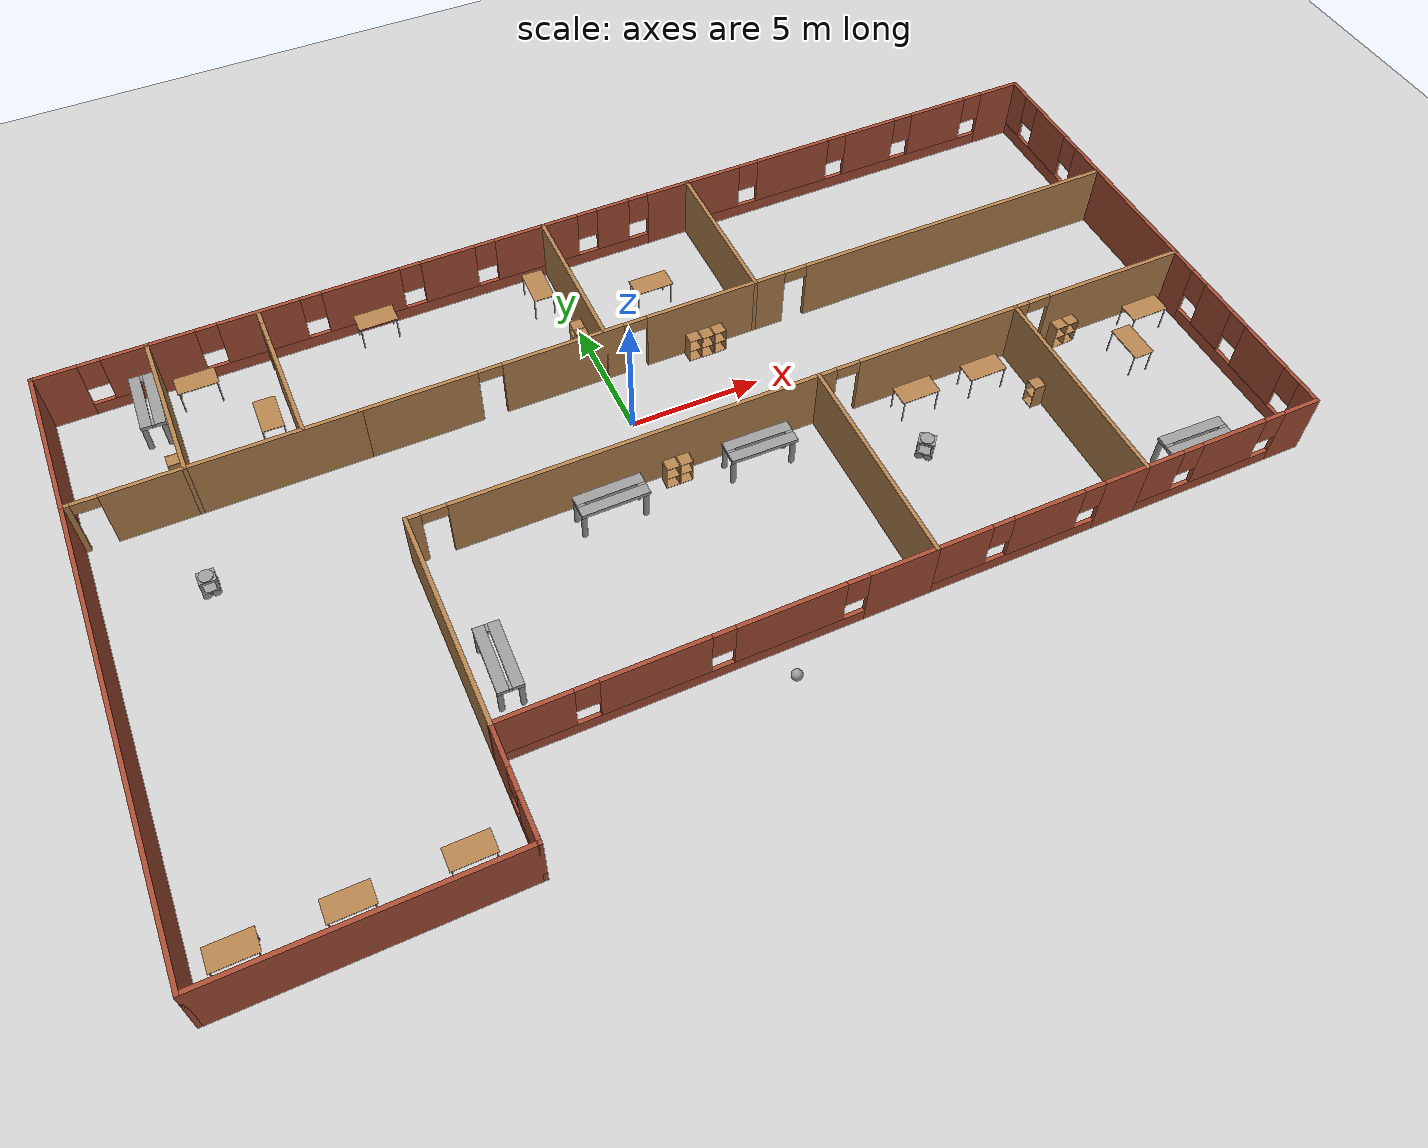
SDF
<sdf version="1.6">
 <world name="default">
  <plugin name="greetings" filename="libgreetings.so"/>
  <light name="sun" type="directional">
   <pose>0 0 10 0 -0 0</pose>
   <diffuse>0.8 0.8 0.8 1</diffuse>
   <specular>0.2 0.2 0.2 1</specular>
   <attenuation>
    <range>1000</range>
    <constant>0.9</constant>
    <linear>0.01</linear>
    <quadratic>0.001</quadratic>
   </attenuation>
   <direction>-0.5 0.1 -0.9</direction>
  </light>
  <model name="ground_plane">
   <static>1</static>
   <link name="link">
    <collision name="collision">
     <geometry><plane><normal>0 0 1</normal><size>100 100</size></plane></geometry>
     <surface><friction><ode><mu>100</mu><mu2>50</mu2></ode></friction></surface>
    </collision>
    <visual name="visual">
     <cast_shadows>0</cast_shadows>
     <geometry><plane><normal>0 0 1</normal><size>100 100</size></plane></geometry>
     <material>
      <script><uri>file://media/materials/scripts/gazebo.material</uri><name>Gazebo/Grey</name></script>
     </material>
    </visual>
   </link>
  </model>
  <gravity>0 0 -9.8</gravity>
  <magnetic_field>6e-06 2.3e-05 -4.2e-05</magnetic_field>
  <atmosphere type="adiabatic"/>
  <physics name="default_physics" default="0" type="ode">
   <max_step_size>0.001</max_step_size>
   <real_time_factor>1</real_time_factor>
   <real_time_update_rate>1000</real_time_update_rate>
  </physics>
  <scene><ambient>0.4 0.4 0.4 1</ambient><background>0.7 0.7 0.7 1</background><shadows>1</shadows></scene>
  <spherical_coordinates>
   <surface_model>EARTH_WGS84</surface_model>
   <latitude_deg>0</latitude_deg>
   <longitude_deg>0</longitude_deg>
   <elevation>0</elevation>
   <heading_deg>0</heading_deg>
  </spherical_coordinates>
  <model name="research_lab">
   <pose>1.02578 -3.01418 0 0 -0 0</pose>
   <link name="Wall_0">
    <pose>5 0.5 0 0 -0 3.14159</pose>
    <visual name="Wall_0_Visual_0">
     <pose>-12.265 0 1.25 0 -0 0</pose>
     <geometry><box><size>5.61997 0.15 2.5</size></box></geometry>
     <material>
      <script><uri>file://media/materials/scripts/gazebo.material</uri><name>Gazebo/Wood</name></script>
      <ambient>0.666667 0.333333 0 1</ambient>
     </material>
     <meta><layer>0</layer></meta>
    </visual>
    <collision name="Wall_0_Collision_0">
     <geometry><box><size>5.61997 0.15 2.5</size></box></geometry>
     <pose>-12.265 0 1.25 0 -0 0</pose>
    </collision>
    <visual name="Wall_0_Visual_1">
     <pose>-5.07203 0 1.25 0 -0 0</pose>
     <geometry><box><size>6.966 0.15 2.5</size></box></geometry>
     <material>
      <script><uri>file://media/materials/scripts/gazebo.material</uri><name>Gazebo/Wood</name></script>
      <ambient>0.666667 0.333333 0 1</ambient>
     </material>
     <meta><layer>0</layer></meta>
    </visual>
    <collision name="Wall_0_Collision_1">
     <geometry><box><size>6.966 0.15 2.5</size></box></geometry>
     <pose>-5.07203 0 1.25 0 -0 0</pose>
    </collision>
    <visual name="Wall_0_Visual_2">
     <pose>6.45097 0 1.25 0 -0 0</pose>
     <geometry><box><size>14.28 0.15 2.5</size></box></geometry>
     <material>
      <script><uri>file://media/materials/scripts/gazebo.material</uri><name>Gazebo/Wood</name></script>
      <ambient>0.666667 0.333333 0 1</ambient>
     </material>
     <meta><layer>0</layer></meta>
    </visual>
    <collision name="Wall_0_Collision_2">
     <geometry><box><size>14.28 0.15 2.5</size></box></geometry>
     <pose>6.45097 0 1.25 0 -0 0</pose>
    </collision>
    <visual name="Wall_0_Visual_3">
     <pose>14.783 0 1.25 0 -0 0</pose>
     <geometry><box><size>0.58403 0.15 2.5</size></box></geometry>
     <material>
      <script><uri>file://media/materials/scripts/gazebo.material</uri><name>Gazebo/Wood</name></script>
      <ambient>0.666667 0.333333 0 1</ambient>
     </material>
     <meta><layer>0</layer></meta>
    </visual>
    <collision name="Wall_0_Collision_3">
     <geometry><box><size>0.58403 0.15 2.5</size></box></geometry>
     <pose>14.783 0 1.25 0 -0 0</pose>
    </collision>
    <visual name="Wall_0_Visual_4">
     <pose>-9.00503 0 2.25 0 -0 0</pose>
     <geometry><box><size>0.9 0.15 0.5</size></box></geometry>
     <material>
      <script><uri>file://media/materials/scripts/gazebo.material</uri><name>Gazebo/Wood</name></script>
      <ambient>0.666667 0.333333 0 1</ambient>
     </material>
     <meta><layer>0</layer></meta>
    </visual>
    <collision name="Wall_0_Collision_4">
     <geometry><box><size>0.9 0.15 0.5</size></box></geometry>
     <pose>-9.00503 0 2.25 0 -0 0</pose>
    </collision>
    <visual name="Wall_0_Visual_5">
     <pose>-1.13903 0 2.25 0 -0 0</pose>
     <geometry><box><size>0.9 0.15 0.5</size></box></geometry>
     <material>
      <script><uri>file://media/materials/scripts/gazebo.material</uri><name>Gazebo/Wood</name></script>
      <ambient>0.666667 0.333333 0 1</ambient>
     </material>
     <meta><layer>0</layer></meta>
    </visual>
    <collision name="Wall_0_Collision_5">
     <geometry><box><size>0.9 0.15 0.5</size></box></geometry>
     <pose>-1.13903 0 2.25 0 -0 0</pose>
    </collision>
    <visual name="Wall_0_Visual_6">
     <pose>14.041 0 2.25 0 -0 0</pose>
     <geometry><box><size>0.9 0.15 0.5</size></box></geometry>
     <material>
      <script><uri>file://media/materials/scripts/gazebo.material</uri><name>Gazebo/Wood</name></script>
      <ambient>0.666667 0.333333 0 1</ambient>
     </material>
     <meta><layer>0</layer></meta>
    </visual>
    <collision name="Wall_0_Collision_6">
     <geometry><box><size>0.9 0.15 0.5</size></box></geometry>
     <pose>14.041 0 2.25 0 -0 0</pose>
    </collision>
   </link>
   <link name="Wall_10">
    <pose>16.5 -7.5 0 0 -0 3.14159</pose>
    <visual name="Wall_10_Visual_0">
     <pose>-2.84774 0 1.25 0 -0 0</pose>
     <geometry><box><size>1.45451 0.15 2.5</size></box></geometry>
     <material>
      <script><uri>file://media/materials/scripts/gazebo.material</uri><name>Gazebo/Bricks</name></script>
      <ambient>1 1 1 1</ambient>
     </material>
     <meta><layer>0</layer></meta>
    </visual>
    <collision name="Wall_10_Collision_0">
     <geometry><box><size>1.45451 0.15 2.5</size></box></geometry>
     <pose>-2.84774 0 1.25 0 -0 0</pose>
    </collision>
    <visual name="Wall_10_Visual_1">
     <pose>0.727257 0 0.25 0 -0 0</pose>
     <geometry><box><size>5.69549 0.15 0.5</size></box></geometry>
     <material>
      <script><uri>file://media/materials/scripts/gazebo.material</uri><name>Gazebo/Bricks</name></script>
      <ambient>1 1 1 1</ambient>
     </material>
     <meta><layer>0</layer></meta>
    </visual>
    <collision name="Wall_10_Collision_1">
     <geometry><box><size>5.69549 0.15 0.5</size></box></geometry>
     <pose>0.727257 0 0.25 0 -0 0</pose>
    </collision>
    <visual name="Wall_10_Visual_2">
     <pose>-0.041486 0 1.5 0 -0 0</pose>
     <geometry><box><size>2.558 0.15 2</size></box></geometry>
     <material>
      <script><uri>file://media/materials/scripts/gazebo.material</uri><name>Gazebo/Bricks</name></script>
      <ambient>1 1 1 1</ambient>
     </material>
     <meta><layer>0</layer></meta>
    </visual>
    <collision name="Wall_10_Collision_2">
     <geometry><box><size>2.558 0.15 2</size></box></geometry>
     <pose>-0.041486 0 1.5 0 -0 0</pose>
    </collision>
    <visual name="Wall_10_Visual_3">
     <pose>2.80626 0 1.5 0 -0 0</pose>
     <geometry><box><size>1.53749 0.15 2</size></box></geometry>
     <material>
      <script><uri>file://media/materials/scripts/gazebo.material</uri><name>Gazebo/Bricks</name></script>
      <ambient>1 1 1 1</ambient>
     </material>
     <meta><layer>0</layer></meta>
    </visual>
    <collision name="Wall_10_Collision_3">
     <geometry><box><size>1.53749 0.15 2</size></box></geometry>
     <pose>2.80626 0 1.5 0 -0 0</pose>
    </collision>
    <visual name="Wall_10_Visual_4">
     <pose>-1.72049 0 1.9 0 -0 0</pose>
     <geometry><box><size>0.8 0.15 1.2</size></box></geometry>
     <material>
      <script><uri>file://media/materials/scripts/gazebo.material</uri><name>Gazebo/Bricks</name></script>
      <ambient>1 1 1 1</ambient>
     </material>
     <meta><layer>0</layer></meta>
    </visual>
    <collision name="Wall_10_Collision_4">
     <geometry><box><size>0.8 0.15 1.2</size></box></geometry>
     <pose>-1.72049 0 1.9 0 -0 0</pose>
    </collision>
    <visual name="Wall_10_Visual_5">
     <pose>1.63751 0 1.9 0 -0 0</pose>
     <geometry><box><size>0.8 0.15 1.2</size></box></geometry>
     <material>
      <script><uri>file://media/materials/scripts/gazebo.material</uri><name>Gazebo/Bricks</name></script>
      <ambient>1 1 1 1</ambient>
     </material>
     <meta><layer>0</layer></meta>
    </visual>
    <collision name="Wall_10_Collision_5">
     <geometry><box><size>0.8 0.15 1.2</size></box></geometry>
     <pose>1.63751 0 1.9 0 -0 0</pose>
    </collision>
   </link>
   <link name="Wall_11">
    <collision name="Wall_11_Collision">
     <geometry><box><size>8.15 0.15 2.5</size></box></geometry>
     <pose>0 0 1.25 0 -0 0</pose>
    </collision>
    <visual name="Wall_11_Visual">
     <pose>0 0 1.25 0 -0 0</pose>
     <geometry><box><size>8.15 0.15 2.5</size></box></geometry>
     <material>
      <script><uri>file://media/materials/scripts/gazebo.material</uri><name>Gazebo/Wood</name></script>
      <ambient>1 1 1 1</ambient>
     </material>
     <meta><layer>0</layer></meta>
    </visual>
    <pose>13 -3.5 0 0 -0 1.5708</pose>
   </link>
   <link name="Wall_13">
    <pose>9 -7.5 0 0 -0 3.14159</pose>
    <visual name="Wall_13_Visual_0">
     <pose>-3.21374 0 1.25 0 -0 0</pose>
     <geometry><box><size>1.72251 0.15 2.5</size></box></geometry>
     <material>
      <script><uri>file://media/materials/scripts/gazebo.material</uri><name>Gazebo/Bricks</name></script>
      <ambient>1 1 1 1</ambient>
     </material>
     <meta><layer>0</layer></meta>
    </visual>
    <collision name="Wall_13_Collision_0">
     <geometry><box><size>1.72251 0.15 2.5</size></box></geometry>
     <pose>-3.21374 0 1.25 0 -0 0</pose>
    </collision>
    <visual name="Wall_13_Visual_1">
     <pose>0.861257 0 0.25 0 -0 0</pose>
     <geometry><box><size>6.42749 0.15 0.5</size></box></geometry>
     <material>
      <script><uri>file://media/materials/scripts/gazebo.material</uri><name>Gazebo/Bricks</name></script>
      <ambient>1 1 1 1</ambient>
     </material>
     <meta><layer>0</layer></meta>
    </visual>
    <collision name="Wall_13_Collision_1">
     <geometry><box><size>6.42749 0.15 0.5</size></box></geometry>
     <pose>0.861257 0 0.25 0 -0 0</pose>
    </collision>
    <visual name="Wall_13_Visual_2">
     <pose>-0.204486 0 1.5 0 -0 0</pose>
     <geometry><box><size>2.696 0.15 2</size></box></geometry>
     <material>
      <script><uri>file://media/materials/scripts/gazebo.material</uri><name>Gazebo/Bricks</name></script>
      <ambient>1 1 1 1</ambient>
     </material>
     <meta><layer>0</layer></meta>
    </visual>
    <collision name="Wall_13_Collision_2">
     <geometry><box><size>2.696 0.15 2</size></box></geometry>
     <pose>-0.204486 0 1.5 0 -0 0</pose>
    </collision>
    <visual name="Wall_13_Visual_3">
     <pose>3.00926 0 1.5 0 -0 0</pose>
     <geometry><box><size>2.13149 0.15 2</size></box></geometry>
     <material>
      <script><uri>file://media/materials/scripts/gazebo.material</uri><name>Gazebo/Bricks</name></script>
      <ambient>1 1 1 1</ambient>
     </material>
     <meta><layer>0</layer></meta>
    </visual>
    <collision name="Wall_13_Collision_3">
     <geometry><box><size>2.13149 0.15 2</size></box></geometry>
     <pose>3.00926 0 1.5 0 -0 0</pose>
    </collision>
    <visual name="Wall_13_Visual_4">
     <pose>-1.95249 0 1.9 0 -0 0</pose>
     <geometry><box><size>0.8 0.15 1.2</size></box></geometry>
     <material>
      <script><uri>file://media/materials/scripts/gazebo.material</uri><name>Gazebo/Bricks</name></script>
      <ambient>1 1 1 1</ambient>
     </material>
     <meta><layer>0</layer></meta>
    </visual>
    <collision name="Wall_13_Collision_4">
     <geometry><box><size>0.8 0.15 1.2</size></box></geometry>
     <pose>-1.95249 0 1.9 0 -0 0</pose>
    </collision>
    <visual name="Wall_13_Visual_5">
     <pose>1.54351 0 1.9 0 -0 0</pose>
     <geometry><box><size>0.8 0.15 1.2</size></box></geometry>
     <material>
      <script><uri>file://media/materials/scripts/gazebo.material</uri><name>Gazebo/Bricks</name></script>
      <ambient>1 1 1 1</ambient>
     </material>
     <meta><layer>0</layer></meta>
    </visual>
    <collision name="Wall_13_Collision_5">
     <geometry><box><size>0.8 0.15 1.2</size></box></geometry>
     <pose>1.54351 0 1.9 0 -0 0</pose>
    </collision>
   </link>
   <link name="Wall_14">
    <collision name="Wall_14_Collision">
     <geometry><box><size>8.15 0.15 2.5</size></box></geometry>
     <pose>0 0 1.25 0 -0 0</pose>
    </collision>
    <visual name="Wall_14_Visual">
     <pose>0 0 1.25 0 -0 0</pose>
     <geometry><box><size>8.15 0.15 2.5</size></box></geometry>
     <material>
      <script><uri>file://media/materials/scripts/gazebo.material</uri><name>Gazebo/Wood</name></script>
      <ambient>1 1 1 1</ambient>
     </material>
     <meta><layer>0</layer></meta>
    </visual>
    <pose>5 -3.5 0 0 -0 1.5708</pose>
   </link>
   <link name="Wall_16">
    <pose>-2.5 -7.5 0 0 -0 3.14159</pose>
    <visual name="Wall_16_Visual_0">
     <pose>-6.32074 0 1.25 0 -0 0</pose>
     <geometry><box><size>2.50851 0.15 2.5</size></box></geometry>
     <material>
      <script><uri>file://media/materials/scripts/gazebo.material</uri><name>Gazebo/Bricks</name></script>
      <ambient>0.666667 0.333333 0 1</ambient>
     </material>
     <meta><layer>0</layer></meta>
    </visual>
    <collision name="Wall_16_Collision_0">
     <geometry><box><size>2.50851 0.15 2.5</size></box></geometry>
     <pose>-6.32074 0 1.25 0 -0 0</pose>
    </collision>
    <visual name="Wall_16_Visual_1">
     <pose>1.25426 0 0.25 0 -0 0</pose>
     <geometry><box><size>12.6415 0.15 0.5</size></box></geometry>
     <material>
      <script><uri>file://media/materials/scripts/gazebo.material</uri><name>Gazebo/Bricks</name></script>
      <ambient>0.666667 0.333333 0 1</ambient>
     </material>
     <meta><layer>0</layer></meta>
    </visual>
    <collision name="Wall_16_Collision_1">
     <geometry><box><size>12.6415 0.15 0.5</size></box></geometry>
     <pose>1.25426 0 0.25 0 -0 0</pose>
    </collision>
    <visual name="Wall_16_Visual_2">
     <pose>-2.34349 0 1.5 0 -0 0</pose>
     <geometry><box><size>3.846 0.15 2</size></box></geometry>
     <material>
      <script><uri>file://media/materials/scripts/gazebo.material</uri><name>Gazebo/Bricks</name></script>
      <ambient>0.666667 0.333333 0 1</ambient>
     </material>
     <meta><layer>0</layer></meta>
    </visual>
    <collision name="Wall_16_Collision_2">
     <geometry><box><size>3.846 0.15 2</size></box></geometry>
     <pose>-2.34349 0 1.5 0 -0 0</pose>
    </collision>
    <visual name="Wall_16_Visual_3">
     <pose>2.23351 0 1.5 0 -0 0</pose>
     <geometry><box><size>3.708 0.15 2</size></box></geometry>
     <material>
      <script><uri>file://media/materials/scripts/gazebo.material</uri><name>Gazebo/Bricks</name></script>
      <ambient>0.666667 0.333333 0 1</ambient>
     </material>
     <meta><layer>0</layer></meta>
    </visual>
    <collision name="Wall_16_Collision_3">
     <geometry><box><size>3.708 0.15 2</size></box></geometry>
     <pose>2.23351 0 1.5 0 -0 0</pose>
    </collision>
    <visual name="Wall_16_Visual_4">
     <pose>6.23126 0 1.5 0 -0 0</pose>
     <geometry><box><size>2.68749 0.15 2</size></box></geometry>
     <material>
      <script><uri>file://media/materials/scripts/gazebo.material</uri><name>Gazebo/Bricks</name></script>
      <ambient>0.666667 0.333333 0 1</ambient>
     </material>
     <meta><layer>0</layer></meta>
    </visual>
    <collision name="Wall_16_Collision_4">
     <geometry><box><size>2.68749 0.15 2</size></box></geometry>
     <pose>6.23126 0 1.5 0 -0 0</pose>
    </collision>
    <visual name="Wall_16_Visual_5">
     <pose>-4.66649 0 1.9 0 -0 0</pose>
     <geometry><box><size>0.8 0.15 1.2</size></box></geometry>
     <material>
      <script><uri>file://media/materials/scripts/gazebo.material</uri><name>Gazebo/Bricks</name></script>
      <ambient>0.666667 0.333333 0 1</ambient>
     </material>
     <meta><layer>0</layer></meta>
    </visual>
    <collision name="Wall_16_Collision_5">
     <geometry><box><size>0.8 0.15 1.2</size></box></geometry>
     <pose>-4.66649 0 1.9 0 -0 0</pose>
    </collision>
    <visual name="Wall_16_Visual_6">
     <pose>-0.020487 0 1.9 0 -0 0</pose>
     <geometry><box><size>0.8 0.15 1.2</size></box></geometry>
     <material>
      <script><uri>file://media/materials/scripts/gazebo.material</uri><name>Gazebo/Bricks</name></script>
      <ambient>0.666667 0.333333 0 1</ambient>
     </material>
     <meta><layer>0</layer></meta>
    </visual>
    <collision name="Wall_16_Collision_6">
     <geometry><box><size>0.8 0.15 1.2</size></box></geometry>
     <pose>-0.020487 0 1.9 0 -0 0</pose>
    </collision>
    <visual name="Wall_16_Visual_7">
     <pose>4.48751 0 1.9 0 -0 0</pose>
     <geometry><box><size>0.8 0.15 1.2</size></box></geometry>
     <material>
      <script><uri>file://media/materials/scripts/gazebo.material</uri><name>Gazebo/Bricks</name></script>
      <ambient>0.666667 0.333333 0 1</ambient>
     </material>
     <meta><layer>0</layer></meta>
    </visual>
    <collision name="Wall_16_Collision_7">
     <geometry><box><size>0.8 0.15 1.2</size></box></geometry>
     <pose>4.48751 0 1.9 0 -0 0</pose>
    </collision>
   </link>
   <link name="Wall_17">
    <collision name="Wall_17_Collision">
     <geometry><box><size>8.15 0.15 2.5</size></box></geometry>
     <pose>0 0 1.25 0 -0 0</pose>
    </collision>
    <visual name="Wall_17_Visual">
     <pose>0 0 1.25 0 -0 0</pose>
     <geometry><box><size>8.15 0.15 2.5</size></box></geometry>
     <material>
      <script><uri>file://media/materials/scripts/gazebo.material</uri><name>Gazebo/Wood</name></script>
      <ambient>0.666667 0.333333 0 1</ambient>
     </material>
     <meta><layer>0</layer></meta>
    </visual>
    <pose>-10 -3.5 0 0 -0 1.5708</pose>
   </link>
   <link name="Wall_19">
    <pose>-15 5.5 0 0 -0 3.14159</pose>
    <visual name="Wall_19_Visual_0">
     <pose>-0.621116 0 1.25 0 -0 0</pose>
     <geometry><box><size>8.90777 0.15 2.5</size></box></geometry>
     <material>
      <script><uri>file://media/materials/scripts/gazebo.material</uri><name>Gazebo/Wood</name></script>
      <ambient>1 1 1 1</ambient>
     </material>
     <meta><layer>0</layer></meta>
    </visual>
    <collision name="Wall_19_Collision_0">
     <geometry><box><size>8.90777 0.15 2.5</size></box></geometry>
     <pose>-0.621116 0 1.25 0 -0 0</pose>
    </collision>
    <visual name="Wall_19_Visual_1">
     <pose>4.90388 0 1.25 0 -0 0</pose>
     <geometry><box><size>0.342232 0.15 2.5</size></box></geometry>
     <material>
      <script><uri>file://media/materials/scripts/gazebo.material</uri><name>Gazebo/Wood</name></script>
      <ambient>1 1 1 1</ambient>
     </material>
     <meta><layer>0</layer></meta>
    </visual>
    <collision name="Wall_19_Collision_1">
     <geometry><box><size>0.342232 0.15 2.5</size></box></geometry>
     <pose>4.90388 0 1.25 0 -0 0</pose>
    </collision>
    <visual name="Wall_19_Visual_2">
     <pose>4.28277 0 2.25 0 -0 0</pose>
     <geometry><box><size>0.9 0.15 0.5</size></box></geometry>
     <material>
      <script><uri>file://media/materials/scripts/gazebo.material</uri><name>Gazebo/Wood</name></script>
      <ambient>1 1 1 1</ambient>
     </material>
     <meta><layer>0</layer></meta>
    </visual>
    <collision name="Wall_19_Collision_2">
     <geometry><box><size>0.9 0.15 0.5</size></box></geometry>
     <pose>4.28277 0 2.25 0 -0 0</pose>
    </collision>
   </link>
   <link name="Wall_20">
    <collision name="Wall_20_Collision">
     <geometry><box><size>17.15 0.15 2.5</size></box></geometry>
     <pose>0 0 1.25 0 -0 0</pose>
    </collision>
    <visual name="Wall_20_Visual">
     <pose>0 0 1.25 0 -0 0</pose>
     <geometry><box><size>17.15 0.15 2.5</size></box></geometry>
     <material>
      <script><uri>file://media/materials/scripts/gazebo.material</uri><name>Gazebo/Bricks</name></script>
      <ambient>1 1 1 1</ambient>
     </material>
     <meta><layer>0</layer></meta>
    </visual>
    <pose>-20 -3 0 0 0 -1.5708</pose>
   </link>
   <link name="Wall_21">
    <collision name="Wall_21_Collision">
     <geometry><box><size>10.15 0.15 2.5</size></box></geometry>
     <pose>0 0 1.25 0 -0 0</pose>
    </collision>
    <visual name="Wall_21_Visual">
     <pose>0 0 1.25 0 -0 0</pose>
     <geometry><box><size>10.15 0.15 2.5</size></box></geometry>
     <material>
      <script><uri>file://media/materials/scripts/gazebo.material</uri><name>Gazebo/Bricks</name></script>
      <ambient>0.666667 0.333333 0 1</ambient>
     </material>
     <meta><layer>0</layer></meta>
    </visual>
    <pose>-15 -11.5 0 0 -0 0</pose>
   </link>
   <link name="Wall_24">
    <pose>20 8.5 0 0 -0 1.5708</pose>
    <visual name="Wall_24_Visual_0">
     <pose>-2.30754 0 1.25 0 -0 0</pose>
     <geometry><box><size>1.53492 0.15 2.5</size></box></geometry>
     <material>
      <script><uri>file://media/materials/scripts/gazebo.material</uri><name>Gazebo/Bricks</name></script>
      <ambient>1 1 1 1</ambient>
     </material>
     <meta><layer>0</layer></meta>
    </visual>
    <collision name="Wall_24_Collision_0">
     <geometry><box><size>1.53492 0.15 2.5</size></box></geometry>
     <pose>-2.30754 0 1.25 0 -0 0</pose>
    </collision>
    <visual name="Wall_24_Visual_1">
     <pose>0.76746 0 0.25 0 -0 0</pose>
     <geometry><box><size>4.61508 0.15 0.5</size></box></geometry>
     <material>
      <script><uri>file://media/materials/scripts/gazebo.material</uri><name>Gazebo/Bricks</name></script>
      <ambient>1 1 1 1</ambient>
     </material>
     <meta><layer>0</layer></meta>
    </visual>
    <collision name="Wall_24_Collision_1">
     <geometry><box><size>4.61508 0.15 0.5</size></box></geometry>
     <pose>0.76746 0 0.25 0 -0 0</pose>
    </collision>
    <visual name="Wall_24_Visual_2">
     <pose>0.23992 0 1.5 0 -0 0</pose>
     <geometry><box><size>1.96 0.15 2</size></box></geometry>
     <material>
      <script><uri>file://media/materials/scripts/gazebo.material</uri><name>Gazebo/Bricks</name></script>
      <ambient>1 1 1 1</ambient>
     </material>
     <meta><layer>0</layer></meta>
    </visual>
    <collision name="Wall_24_Collision_2">
     <geometry><box><size>1.96 0.15 2</size></box></geometry>
     <pose>0.23992 0 1.5 0 -0 0</pose>
    </collision>
    <visual name="Wall_24_Visual_3">
     <pose>2.54746 0 1.5 0 -0 0</pose>
     <geometry><box><size>1.05508 0.15 2</size></box></geometry>
     <material>
      <script><uri>file://media/materials/scripts/gazebo.material</uri><name>Gazebo/Bricks</name></script>
      <ambient>1 1 1 1</ambient>
     </material>
     <meta><layer>0</layer></meta>
    </visual>
    <collision name="Wall_24_Collision_3">
     <geometry><box><size>1.05508 0.15 2</size></box></geometry>
     <pose>2.54746 0 1.5 0 -0 0</pose>
    </collision>
    <visual name="Wall_24_Visual_4">
     <pose>-1.14008 0 1.9 0 -0 0</pose>
     <geometry><box><size>0.8 0.15 1.2</size></box></geometry>
     <material>
      <script><uri>file://media/materials/scripts/gazebo.material</uri><name>Gazebo/Bricks</name></script>
      <ambient>1 1 1 1</ambient>
     </material>
     <meta><layer>0</layer></meta>
    </visual>
    <collision name="Wall_24_Collision_4">
     <geometry><box><size>0.8 0.15 1.2</size></box></geometry>
     <pose>-1.14008 0 1.9 0 -0 0</pose>
    </collision>
    <visual name="Wall_24_Visual_5">
     <pose>1.61992 0 1.9 0 -0 0</pose>
     <geometry><box><size>0.8 0.15 1.2</size></box></geometry>
     <material>
      <script><uri>file://media/materials/scripts/gazebo.material</uri><name>Gazebo/Bricks</name></script>
      <ambient>1 1 1 1</ambient>
     </material>
     <meta><layer>0</layer></meta>
    </visual>
    <collision name="Wall_24_Collision_5">
     <geometry><box><size>0.8 0.15 1.2</size></box></geometry>
     <pose>1.61992 0 1.9 0 -0 0</pose>
    </collision>
   </link>
   <link name="Wall_25">
    <pose>12.5 11.5 0 0 -0 3.14159</pose>
    <visual name="Wall_25_Visual_0">
     <pose>-6.70094 0 1.25 0 -0 0</pose>
     <geometry><box><size>1.74813 0.15 2.5</size></box></geometry>
     <material>
      <script><uri>file://media/materials/scripts/gazebo.material</uri><name>Gazebo/Bricks</name></script>
      <ambient>1 1 1 1</ambient>
     </material>
     <meta><layer>0</layer></meta>
    </visual>
    <collision name="Wall_25_Collision_0">
     <geometry><box><size>1.74813 0.15 2.5</size></box></geometry>
     <pose>-6.70094 0 1.25 0 -0 0</pose>
    </collision>
    <visual name="Wall_25_Visual_1">
     <pose>0.874063 0 0.25 0 -0 0</pose>
     <geometry><box><size>13.4019 0.15 0.5</size></box></geometry>
     <material>
      <script><uri>file://media/materials/scripts/gazebo.material</uri><name>Gazebo/Bricks</name></script>
      <ambient>1 1 1 1</ambient>
     </material>
     <meta><layer>0</layer></meta>
    </visual>
    <collision name="Wall_25_Collision_1">
     <geometry><box><size>13.4019 0.15 0.5</size></box></geometry>
     <pose>0.874063 0 0.25 0 -0 0</pose>
    </collision>
    <visual name="Wall_25_Visual_2">
     <pose>-3.78433 0 1.5 0 -0 0</pose>
     <geometry><box><size>2.48509 0.15 2</size></box></geometry>
     <material>
      <script><uri>file://media/materials/scripts/gazebo.material</uri><name>Gazebo/Bricks</name></script>
      <ambient>1 1 1 1</ambient>
     </material>
     <meta><layer>0</layer></meta>
    </visual>
    <collision name="Wall_25_Collision_2">
     <geometry><box><size>2.48509 0.15 2</size></box></geometry>
     <pose>-3.78433 0 1.5 0 -0 0</pose>
    </collision>
    <visual name="Wall_25_Visual_3">
     <pose>-0.620908 0 1.5 0 -0 0</pose>
     <geometry><box><size>2.24175 0.15 2</size></box></geometry>
     <material>
      <script><uri>file://media/materials/scripts/gazebo.material</uri><name>Gazebo/Bricks</name></script>
      <ambient>1 1 1 1</ambient>
     </material>
     <meta><layer>0</layer></meta>
    </visual>
    <collision name="Wall_25_Collision_3">
     <geometry><box><size>2.24175 0.15 2</size></box></geometry>
     <pose>-0.620908 0 1.5 0 -0 0</pose>
    </collision>
    <visual name="Wall_25_Visual_4">
     <pose>2.8771 0 1.5 0 -0 0</pose>
     <geometry><box><size>3.15428 0.15 2</size></box></geometry>
     <material>
      <script><uri>file://media/materials/scripts/gazebo.material</uri><name>Gazebo/Bricks</name></script>
      <ambient>1 1 1 1</ambient>
     </material>
     <meta><layer>0</layer></meta>
    </visual>
    <collision name="Wall_25_Collision_4">
     <geometry><box><size>3.15428 0.15 2</size></box></geometry>
     <pose>2.8771 0 1.5 0 -0 0</pose>
    </collision>
    <visual name="Wall_25_Visual_5">
     <pose>6.41462 0 1.5 0 -0 0</pose>
     <geometry><box><size>2.32076 0.15 2</size></box></geometry>
     <material>
      <script><uri>file://media/materials/scripts/gazebo.material</uri><name>Gazebo/Bricks</name></script>
      <ambient>1 1 1 1</ambient>
     </material>
     <meta><layer>0</layer></meta>
    </visual>
    <collision name="Wall_25_Collision_5">
     <geometry><box><size>2.32076 0.15 2</size></box></geometry>
     <pose>6.41462 0 1.5 0 -0 0</pose>
    </collision>
    <visual name="Wall_25_Visual_6">
     <pose>-5.42687 0 1.9 0 -0 0</pose>
     <geometry><box><size>0.8 0.15 1.2</size></box></geometry>
     <material>
      <script><uri>file://media/materials/scripts/gazebo.material</uri><name>Gazebo/Bricks</name></script>
      <ambient>1 1 1 1</ambient>
     </material>
     <meta><layer>0</layer></meta>
    </visual>
    <collision name="Wall_25_Collision_6">
     <geometry><box><size>0.8 0.15 1.2</size></box></geometry>
     <pose>-5.42687 0 1.9 0 -0 0</pose>
    </collision>
    <visual name="Wall_25_Visual_7">
     <pose>-2.14178 0 1.9 0 -0 0</pose>
     <geometry><box><size>0.8 0.15 1.2</size></box></geometry>
     <material>
      <script><uri>file://media/materials/scripts/gazebo.material</uri><name>Gazebo/Bricks</name></script>
      <ambient>1 1 1 1</ambient>
     </material>
     <meta><layer>0</layer></meta>
    </visual>
    <collision name="Wall_25_Collision_7">
     <geometry><box><size>0.8 0.15 1.2</size></box></geometry>
     <pose>-2.14178 0 1.9 0 -0 0</pose>
    </collision>
    <visual name="Wall_25_Visual_8">
     <pose>0.899966 0 1.9 0 -0 0</pose>
     <geometry><box><size>0.8 0.15 1.2</size></box></geometry>
     <material>
      <script><uri>file://media/materials/scripts/gazebo.material</uri><name>Gazebo/Bricks</name></script>
      <ambient>1 1 1 1</ambient>
     </material>
     <meta><layer>0</layer></meta>
    </visual>
    <collision name="Wall_25_Collision_8">
     <geometry><box><size>0.8 0.15 1.2</size></box></geometry>
     <pose>0.899966 0 1.9 0 -0 0</pose>
    </collision>
    <visual name="Wall_25_Visual_9">
     <pose>4.85424 0 1.9 0 -0 0</pose>
     <geometry><box><size>0.8 0.15 1.2</size></box></geometry>
     <material>
      <script><uri>file://media/materials/scripts/gazebo.material</uri><name>Gazebo/Bricks</name></script>
      <ambient>1 1 1 1</ambient>
     </material>
     <meta><layer>0</layer></meta>
    </visual>
    <collision name="Wall_25_Collision_9">
     <geometry><box><size>0.8 0.15 1.2</size></box></geometry>
     <pose>4.85424 0 1.9 0 -0 0</pose>
    </collision>
   </link>
   <link name="Wall_26">
    <collision name="Wall_26_Collision">
     <geometry><box><size>6.15 0.15 2.5</size></box></geometry>
     <pose>0 0 1.25 0 -0 0</pose>
    </collision>
    <visual name="Wall_26_Visual">
     <pose>0 0 1.25 0 -0 0</pose>
     <geometry><box><size>6.15 0.15 2.5</size></box></geometry>
     <material>
      <script><uri>file://media/materials/scripts/gazebo.material</uri><name>Gazebo/Wood</name></script>
      <ambient>1 1 1 1</ambient>
     </material>
     <meta><layer>0</layer></meta>
    </visual>
    <pose>5 8.5 0 0 0 -1.5708</pose>
   </link>
   <link name="Wall_28">
    <pose>2 11.5 0 0 -0 3.14159</pose>
    <visual name="Wall_28_Visual_0">
     <pose>-2.18782 0 1.25 0 -0 0</pose>
     <geometry><box><size>1.77437 0.15 2.5</size></box></geometry>
     <material>
      <script><uri>file://media/materials/scripts/gazebo.material</uri><name>Gazebo/Bricks</name></script>
      <ambient>1 1 1 1</ambient>
     </material>
     <meta><layer>0</layer></meta>
    </visual>
    <collision name="Wall_28_Collision_0">
     <geometry><box><size>1.77437 0.15 2.5</size></box></geometry>
     <pose>-2.18782 0 1.25 0 -0 0</pose>
    </collision>
    <visual name="Wall_28_Visual_1">
     <pose>0.887185 0 0.25 0 -0 0</pose>
     <geometry><box><size>4.37563 0.15 0.5</size></box></geometry>
     <material>
      <script><uri>file://media/materials/scripts/gazebo.material</uri><name>Gazebo/Bricks</name></script>
      <ambient>1 1 1 1</ambient>
     </material>
     <meta><layer>0</layer></meta>
    </visual>
    <collision name="Wall_28_Collision_1">
     <geometry><box><size>4.37563 0.15 0.5</size></box></geometry>
     <pose>0.887185 0 0.25 0 -0 0</pose>
    </collision>
    <visual name="Wall_28_Visual_2">
     <pose>0.163984 0 1.5 0 -0 0</pose>
     <geometry><box><size>1.32923 0.15 2</size></box></geometry>
     <material>
      <script><uri>file://media/materials/scripts/gazebo.material</uri><name>Gazebo/Bricks</name></script>
      <ambient>1 1 1 1</ambient>
     </material>
     <meta><layer>0</layer></meta>
    </visual>
    <collision name="Wall_28_Collision_2">
     <geometry><box><size>1.32923 0.15 2</size></box></geometry>
     <pose>0.163984 0 1.5 0 -0 0</pose>
    </collision>
    <visual name="Wall_28_Visual_3">
     <pose>2.3518 0 1.5 0 -0 0</pose>
     <geometry><box><size>1.4464 0.15 2</size></box></geometry>
     <material>
      <script><uri>file://media/materials/scripts/gazebo.material</uri><name>Gazebo/Bricks</name></script>
      <ambient>1 1 1 1</ambient>
     </material>
     <meta><layer>0</layer></meta>
    </visual>
    <collision name="Wall_28_Collision_3">
     <geometry><box><size>1.4464 0.15 2</size></box></geometry>
     <pose>2.3518 0 1.5 0 -0 0</pose>
    </collision>
    <visual name="Wall_28_Visual_4">
     <pose>-0.900629 0 1.9 0 -0 0</pose>
     <geometry><box><size>0.8 0.15 1.2</size></box></geometry>
     <material>
      <script><uri>file://media/materials/scripts/gazebo.material</uri><name>Gazebo/Bricks</name></script>
      <ambient>1 1 1 1</ambient>
     </material>
     <meta><layer>0</layer></meta>
    </visual>
    <collision name="Wall_28_Collision_4">
     <geometry><box><size>0.8 0.15 1.2</size></box></geometry>
     <pose>-0.900629 0 1.9 0 -0 0</pose>
    </collision>
    <visual name="Wall_28_Visual_5">
     <pose>1.2286 0 1.9 0 -0 0</pose>
     <geometry><box><size>0.8 0.15 1.2</size></box></geometry>
     <material>
      <script><uri>file://media/materials/scripts/gazebo.material</uri><name>Gazebo/Bricks</name></script>
      <ambient>1 1 1 1</ambient>
     </material>
     <meta><layer>0</layer></meta>
    </visual>
    <collision name="Wall_28_Collision_5">
     <geometry><box><size>0.8 0.15 1.2</size></box></geometry>
     <pose>1.2286 0 1.9 0 -0 0</pose>
    </collision>
   </link>
   <link name="Wall_29">
    <collision name="Wall_29_Collision">
     <geometry><box><size>6.15 0.15 2.5</size></box></geometry>
     <pose>0 0 1.25 0 -0 0</pose>
    </collision>
    <visual name="Wall_29_Visual">
     <pose>0 0 1.25 0 -0 0</pose>
     <geometry><box><size>6.15 0.15 2.5</size></box></geometry>
     <material>
      <script><uri>file://media/materials/scripts/gazebo.material</uri><name>Gazebo/Wood</name></script>
      <ambient>1 1 1 1</ambient>
     </material>
     <meta><layer>0</layer></meta>
    </visual>
    <pose>-1 8.5 0 0 0 -1.5708</pose>
   </link>
   <link name="Wall_3">
    <pose>5 5.5 0 0 -0 0</pose>
    <visual name="Wall_3_Visual_0">
     <pose>-12.92 0 1.25 0 -0 0</pose>
     <geometry><box><size>4.31003 0.15 2.5</size></box></geometry>
     <material>
      <script><uri>file://media/materials/scripts/gazebo.material</uri><name>Gazebo/Wood</name></script>
      <ambient>0.666667 0.333333 0 1</ambient>
     </material>
     <meta><layer>0</layer></meta>
    </visual>
    <collision name="Wall_3_Collision_0">
     <geometry><box><size>4.31003 0.15 2.5</size></box></geometry>
     <pose>-12.92 0 1.25 0 -0 0</pose>
    </collision>
    <visual name="Wall_3_Visual_1">
     <pose>-7.55497 0 1.25 0 -0 0</pose>
     <geometry><box><size>4.62 0.15 2.5</size></box></geometry>
     <material>
      <script><uri>file://media/materials/scripts/gazebo.material</uri><name>Gazebo/Wood</name></script>
      <ambient>0.666667 0.333333 0 1</ambient>
     </material>
     <meta><layer>0</layer></meta>
    </visual>
    <collision name="Wall_3_Collision_1">
     <geometry><box><size>4.62 0.15 2.5</size></box></geometry>
     <pose>-7.55497 0 1.25 0 -0 0</pose>
    </collision>
    <visual name="Wall_3_Visual_2">
     <pose>-1.57497 0 1.25 0 -0 0</pose>
     <geometry><box><size>5.54 0.15 2.5</size></box></geometry>
     <material>
      <script><uri>file://media/materials/scripts/gazebo.material</uri><name>Gazebo/Wood</name></script>
      <ambient>0.666667 0.333333 0 1</ambient>
     </material>
     <meta><layer>0</layer></meta>
    </visual>
    <collision name="Wall_3_Collision_2">
     <geometry><box><size>5.54 0.15 2.5</size></box></geometry>
     <pose>-1.57497 0 1.25 0 -0 0</pose>
    </collision>
    <visual name="Wall_3_Visual_3">
     <pose>8.58502 0 1.25 0 -0 0</pose>
     <geometry><box><size>12.98 0.15 2.5</size></box></geometry>
     <material>
      <script><uri>file://media/materials/scripts/gazebo.material</uri><name>Gazebo/Wood</name></script>
      <ambient>0.666667 0.333333 0 1</ambient>
     </material>
     <meta><layer>0</layer></meta>
    </visual>
    <collision name="Wall_3_Collision_3">
     <geometry><box><size>12.98 0.15 2.5</size></box></geometry>
     <pose>8.58502 0 1.25 0 -0 0</pose>
    </collision>
    <visual name="Wall_3_Visual_4">
     <pose>-10.315 0 2.25 0 -0 0</pose>
     <geometry><box><size>0.9 0.15 0.5</size></box></geometry>
     <material>
      <script><uri>file://media/materials/scripts/gazebo.material</uri><name>Gazebo/Wood</name></script>
      <ambient>0.666667 0.333333 0 1</ambient>
     </material>
     <meta><layer>0</layer></meta>
    </visual>
    <collision name="Wall_3_Collision_4">
     <geometry><box><size>0.9 0.15 0.5</size></box></geometry>
     <pose>-10.315 0 2.25 0 -0 0</pose>
    </collision>
    <visual name="Wall_3_Visual_5">
     <pose>-4.79497 0 2.25 0 -0 0</pose>
     <geometry><box><size>0.9 0.15 0.5</size></box></geometry>
     <material>
      <script><uri>file://media/materials/scripts/gazebo.material</uri><name>Gazebo/Wood</name></script>
      <ambient>0.666667 0.333333 0 1</ambient>
     </material>
     <meta><layer>0</layer></meta>
    </visual>
    <collision name="Wall_3_Collision_5">
     <geometry><box><size>0.9 0.15 0.5</size></box></geometry>
     <pose>-4.79497 0 2.25 0 -0 0</pose>
    </collision>
    <visual name="Wall_3_Visual_6">
     <pose>1.64503 0 2.25 0 -0 0</pose>
     <geometry><box><size>0.9 0.15 0.5</size></box></geometry>
     <material>
      <script><uri>file://media/materials/scripts/gazebo.material</uri><name>Gazebo/Wood</name></script>
      <ambient>0.666667 0.333333 0 1</ambient>
     </material>
     <meta><layer>0</layer></meta>
    </visual>
    <collision name="Wall_3_Collision_6">
     <geometry><box><size>0.9 0.15 0.5</size></box></geometry>
     <pose>1.64503 0 2.25 0 -0 0</pose>
    </collision>
   </link>
   <link name="Wall_31">
    <collision name="Wall_31_Collision">
     <geometry><box><size>6.15 0.15 2.5</size></box></geometry>
     <pose>0 0 1.25 0 -0 0</pose>
    </collision>
    <visual name="Wall_31_Visual">
     <pose>0 0 1.25 0 -0 0</pose>
     <geometry><box><size>6.15 0.15 2.5</size></box></geometry>
     <material>
      <script><uri>file://media/materials/scripts/gazebo.material</uri><name>Gazebo/Bricks</name></script>
      <ambient>1 1 1 1</ambient>
     </material>
     <meta><layer>0</layer></meta>
    </visual>
    <pose>-20 8.5 0 0 -0 1.5708</pose>
   </link>
   <link name="Wall_32">
    <pose>-18 11.5 0 0 -0 0</pose>
    <visual name="Wall_32_Visual_0">
     <pose>-1.25081 0 1.25 0 -0 0</pose>
     <geometry><box><size>1.64839 0.15 2.5</size></box></geometry>
     <material>
      <script><uri>file://media/materials/scripts/gazebo.material</uri><name>Gazebo/Bricks</name></script>
      <ambient>1 1 1 1</ambient>
     </material>
     <meta><layer>0</layer></meta>
    </visual>
    <collision name="Wall_32_Collision_0">
     <geometry><box><size>1.64839 0.15 2.5</size></box></geometry>
     <pose>-1.25081 0 1.25 0 -0 0</pose>
    </collision>
    <visual name="Wall_32_Visual_1">
     <pose>0.824194 0 0.25 0 -0 0</pose>
     <geometry><box><size>2.50161 0.15 0.5</size></box></geometry>
     <material>
      <script><uri>file://media/materials/scripts/gazebo.material</uri><name>Gazebo/Bricks</name></script>
      <ambient>1 1 1 1</ambient>
     </material>
     <meta><layer>0</layer></meta>
    </visual>
    <collision name="Wall_32_Collision_1">
     <geometry><box><size>2.50161 0.15 0.5</size></box></geometry>
     <pose>0.824194 0 0.25 0 -0 0</pose>
    </collision>
    <visual name="Wall_32_Visual_2">
     <pose>1.22419 0 1.5 0 -0 0</pose>
     <geometry><box><size>1.70161 0.15 2</size></box></geometry>
     <material>
      <script><uri>file://media/materials/scripts/gazebo.material</uri><name>Gazebo/Bricks</name></script>
      <ambient>1 1 1 1</ambient>
     </material>
     <meta><layer>0</layer></meta>
    </visual>
    <collision name="Wall_32_Collision_2">
     <geometry><box><size>1.70161 0.15 2</size></box></geometry>
     <pose>1.22419 0 1.5 0 -0 0</pose>
    </collision>
    <visual name="Wall_32_Visual_3">
     <pose>-0.026611 0 1.9 0 -0 0</pose>
     <geometry><box><size>0.8 0.15 1.2</size></box></geometry>
     <material>
      <script><uri>file://media/materials/scripts/gazebo.material</uri><name>Gazebo/Bricks</name></script>
      <ambient>1 1 1 1</ambient>
     </material>
     <meta><layer>0</layer></meta>
    </visual>
    <collision name="Wall_32_Collision_3">
     <geometry><box><size>0.8 0.15 1.2</size></box></geometry>
     <pose>-0.026611 0 1.9 0 -0 0</pose>
    </collision>
   </link>
   <link name="Wall_33">
    <collision name="Wall_33_Collision">
     <geometry><box><size>6.15 0.15 2.5</size></box></geometry>
     <pose>0 0 1.25 0 -0 0</pose>
    </collision>
    <visual name="Wall_33_Visual">
     <pose>0 0 1.25 0 -0 0</pose>
     <geometry><box><size>6.15 0.15 2.5</size></box></geometry>
     <material>
      <script><uri>file://media/materials/scripts/gazebo.material</uri><name>Gazebo/Wood</name></script>
      <ambient>1 1 1 1</ambient>
     </material>
     <meta><layer>0</layer></meta>
    </visual>
    <pose>-16 8.5 0 0 0 -1.5708</pose>
   </link>
   <link name="Wall_35">
    <pose>-8.5 11.5 0 0 -0 0</pose>
    <visual name="Wall_35_Visual_0">
     <pose>-6.68242 0 1.25 0 -0 0</pose>
     <geometry><box><size>1.78517 0.15 2.5</size></box></geometry>
     <material>
      <script><uri>file://media/materials/scripts/gazebo.material</uri><name>Gazebo/Bricks</name></script>
      <ambient>1 1 1 1</ambient>
     </material>
     <meta><layer>0</layer></meta>
    </visual>
    <collision name="Wall_35_Collision_0">
     <geometry><box><size>1.78517 0.15 2.5</size></box></geometry>
     <pose>-6.68242 0 1.25 0 -0 0</pose>
    </collision>
    <visual name="Wall_35_Visual_1">
     <pose>0.892584 0 0.25 0 -0 0</pose>
     <geometry><box><size>13.3648 0.15 0.5</size></box></geometry>
     <material>
      <script><uri>file://media/materials/scripts/gazebo.material</uri><name>Gazebo/Bricks</name></script>
      <ambient>1 1 1 1</ambient>
     </material>
     <meta><layer>0</layer></meta>
    </visual>
    <collision name="Wall_35_Collision_1">
     <geometry><box><size>13.3648 0.15 0.5</size></box></geometry>
     <pose>0.892584 0 0.25 0 -0 0</pose>
    </collision>
    <visual name="Wall_35_Visual_2">
     <pose>-3.47353 0 1.5 0 -0 0</pose>
     <geometry><box><size>3.03261 0.15 2</size></box></geometry>
     <material>
      <script><uri>file://media/materials/scripts/gazebo.material</uri><name>Gazebo/Bricks</name></script>
      <ambient>1 1 1 1</ambient>
     </material>
     <meta><layer>0</layer></meta>
    </visual>
    <collision name="Wall_35_Collision_2">
     <geometry><box><size>3.03261 0.15 2</size></box></geometry>
     <pose>-3.47353 0 1.5 0 -0 0</pose>
    </collision>
    <visual name="Wall_35_Visual_3">
     <pose>0.328658 0 1.5 0 -0 0</pose>
     <geometry><box><size>2.97177 0.15 2</size></box></geometry>
     <material>
      <script><uri>file://media/materials/scripts/gazebo.material</uri><name>Gazebo/Bricks</name></script>
      <ambient>1 1 1 1</ambient>
     </material>
     <meta><layer>0</layer></meta>
    </visual>
    <collision name="Wall_35_Collision_3">
     <geometry><box><size>2.97177 0.15 2</size></box></geometry>
     <pose>0.328658 0 1.5 0 -0 0</pose>
    </collision>
    <visual name="Wall_35_Visual_4">
     <pose>3.67458 0 1.5 0 -0 0</pose>
     <geometry><box><size>2.12008 0.15 2</size></box></geometry>
     <material>
      <script><uri>file://media/materials/scripts/gazebo.material</uri><name>Gazebo/Bricks</name></script>
      <ambient>1 1 1 1</ambient>
     </material>
     <meta><layer>0</layer></meta>
    </visual>
    <collision name="Wall_35_Collision_4">
     <geometry><box><size>2.12008 0.15 2</size></box></geometry>
     <pose>3.67458 0 1.5 0 -0 0</pose>
    </collision>
    <visual name="Wall_35_Visual_5">
     <pose>6.55481 0 1.5 0 -0 0</pose>
     <geometry><box><size>2.04038 0.15 2</size></box></geometry>
     <material>
      <script><uri>file://media/materials/scripts/gazebo.material</uri><name>Gazebo/Bricks</name></script>
      <ambient>1 1 1 1</ambient>
     </material>
     <meta><layer>0</layer></meta>
    </visual>
    <collision name="Wall_35_Collision_5">
     <geometry><box><size>2.04038 0.15 2</size></box></geometry>
     <pose>6.55481 0 1.5 0 -0 0</pose>
    </collision>
    <visual name="Wall_35_Visual_6">
     <pose>-5.38983 0 1.9 0 -0 0</pose>
     <geometry><box><size>0.8 0.15 1.2</size></box></geometry>
     <material>
      <script><uri>file://media/materials/scripts/gazebo.material</uri><name>Gazebo/Bricks</name></script>
      <ambient>1 1 1 1</ambient>
     </material>
     <meta><layer>0</layer></meta>
    </visual>
    <collision name="Wall_35_Collision_6">
     <geometry><box><size>0.8 0.15 1.2</size></box></geometry>
     <pose>-5.38983 0 1.9 0 -0 0</pose>
    </collision>
    <visual name="Wall_35_Visual_7">
     <pose>-1.55723 0 1.9 0 -0 0</pose>
     <geometry><box><size>0.8 0.15 1.2</size></box></geometry>
     <material>
      <script><uri>file://media/materials/scripts/gazebo.material</uri><name>Gazebo/Bricks</name></script>
      <ambient>1 1 1 1</ambient>
     </material>
     <meta><layer>0</layer></meta>
    </visual>
    <collision name="Wall_35_Collision_7">
     <geometry><box><size>0.8 0.15 1.2</size></box></geometry>
     <pose>-1.55723 0 1.9 0 -0 0</pose>
    </collision>
    <visual name="Wall_35_Visual_8">
     <pose>2.21454 0 1.9 0 -0 0</pose>
     <geometry><box><size>0.8 0.15 1.2</size></box></geometry>
     <material>
      <script><uri>file://media/materials/scripts/gazebo.material</uri><name>Gazebo/Bricks</name></script>
      <ambient>1 1 1 1</ambient>
     </material>
     <meta><layer>0</layer></meta>
    </visual>
    <collision name="Wall_35_Collision_8">
     <geometry><box><size>0.8 0.15 1.2</size></box></geometry>
     <pose>2.21454 0 1.9 0 -0 0</pose>
    </collision>
    <visual name="Wall_35_Visual_9">
     <pose>5.13462 0 1.9 0 -0 0</pose>
     <geometry><box><size>0.8 0.15 1.2</size></box></geometry>
     <material>
      <script><uri>file://media/materials/scripts/gazebo.material</uri><name>Gazebo/Bricks</name></script>
      <ambient>1 1 1 1</ambient>
     </material>
     <meta><layer>0</layer></meta>
    </visual>
    <collision name="Wall_35_Collision_9">
     <geometry><box><size>0.8 0.15 1.2</size></box></geometry>
     <pose>5.13462 0 1.9 0 -0 0</pose>
    </collision>
   </link>
   <link name="Wall_37">
    <pose>-10 -9.5 0 0 0 -1.5708</pose>
    <visual name="Wall_37_Visual_0">
     <pose>-1.27794 0 1.25 0 -0 0</pose>
     <geometry><box><size>1.59412 0.15 2.5</size></box></geometry>
     <material>
      <script><uri>file://media/materials/scripts/gazebo.material</uri><name>Gazebo/Bricks</name></script>
      <ambient>0.666667 0.333333 0 1</ambient>
     </material>
     <meta><layer>0</layer></meta>
    </visual>
    <collision name="Wall_37_Collision_0">
     <geometry><box><size>1.59412 0.15 2.5</size></box></geometry>
     <pose>-1.27794 0 1.25 0 -0 0</pose>
    </collision>
    <visual name="Wall_37_Visual_1">
     <pose>0.797061 0 0.25 0 -0 0</pose>
     <geometry><box><size>2.55588 0.15 0.5</size></box></geometry>
     <material>
      <script><uri>file://media/materials/scripts/gazebo.material</uri><name>Gazebo/Bricks</name></script>
      <ambient>0.666667 0.333333 0 1</ambient>
     </material>
     <meta><layer>0</layer></meta>
    </visual>
    <collision name="Wall_37_Collision_1">
     <geometry><box><size>2.55588 0.15 0.5</size></box></geometry>
     <pose>0.797061 0 0.25 0 -0 0</pose>
    </collision>
    <visual name="Wall_37_Visual_2">
     <pose>1.19706 0 1.5 0 -0 0</pose>
     <geometry><box><size>1.75588 0.15 2</size></box></geometry>
     <material>
      <script><uri>file://media/materials/scripts/gazebo.material</uri><name>Gazebo/Bricks</name></script>
      <ambient>0.666667 0.333333 0 1</ambient>
     </material>
     <meta><layer>0</layer></meta>
    </visual>
    <collision name="Wall_37_Collision_2">
     <geometry><box><size>1.75588 0.15 2</size></box></geometry>
     <pose>1.19706 0 1.5 0 -0 0</pose>
    </collision>
    <visual name="Wall_37_Visual_3">
     <pose>-0.080878 0 1.9 0 -0 0</pose>
     <geometry><box><size>0.8 0.15 1.2</size></box></geometry>
     <material>
      <script><uri>file://media/materials/scripts/gazebo.material</uri><name>Gazebo/Bricks</name></script>
      <ambient>0.666667 0.333333 0 1</ambient>
     </material>
     <meta><layer>0</layer></meta>
    </visual>
    <collision name="Wall_37_Collision_3">
     <geometry><box><size>0.8 0.15 1.2</size></box></geometry>
     <pose>-0.080878 0 1.9 0 -0 0</pose>
    </collision>
   </link>
   <link name="Wall_4">
    <collision name="Wall_4_Collision">
     <geometry><box><size>5.15 0.15 2.5</size></box></geometry>
     <pose>0 0 1.25 0 -0 0</pose>
    </collision>
    <visual name="Wall_4_Visual">
     <pose>0 0 1.25 0 -0 0</pose>
     <geometry><box><size>5.15 0.15 2.5</size></box></geometry>
     <material>
      <script><uri>file://media/materials/scripts/gazebo.material</uri><name>Gazebo/Bricks</name></script>
      <ambient>1 1 1 1</ambient>
     </material>
     <meta><layer>0</layer></meta>
    </visual>
    <pose>20 3 0 0 0 -1.5708</pose>
   </link>
   <link name="Wall_62">
    <pose>-12 8.5 0 0 -0 1.5708</pose>
    <visual name="Wall_62_Visual_0">
     <pose>-0.800367 0 1.25 0 -0 0</pose>
     <geometry><box><size>4.54927 0.15 2.5</size></box></geometry>
     <material>
      <script><uri>file://media/materials/scripts/gazebo.material</uri><name>Gazebo/Wood</name></script>
      <ambient>1 1 1 1</ambient>
     </material>
     <meta><layer>0</layer></meta>
    </visual>
    <collision name="Wall_62_Collision_0">
     <geometry><box><size>4.54927 0.15 2.5</size></box></geometry>
     <pose>-0.800367 0 1.25 0 -0 0</pose>
    </collision>
    <visual name="Wall_62_Visual_1">
     <pose>2.72463 0 1.25 0 -0 0</pose>
     <geometry><box><size>0.700734 0.15 2.5</size></box></geometry>
     <material>
      <script><uri>file://media/materials/scripts/gazebo.material</uri><name>Gazebo/Wood</name></script>
      <ambient>1 1 1 1</ambient>
     </material>
     <meta><layer>0</layer></meta>
    </visual>
    <collision name="Wall_62_Collision_1">
     <geometry><box><size>0.700734 0.15 2.5</size></box></geometry>
     <pose>2.72463 0 1.25 0 -0 0</pose>
    </collision>
    <visual name="Wall_62_Visual_2">
     <pose>1.92427 0 2.25 0 -0 0</pose>
     <geometry><box><size>0.9 0.15 0.5</size></box></geometry>
     <material>
      <script><uri>file://media/materials/scripts/gazebo.material</uri><name>Gazebo/Wood</name></script>
      <ambient>1 1 1 1</ambient>
     </material>
     <meta><layer>0</layer></meta>
    </visual>
    <collision name="Wall_62_Collision_2">
     <geometry><box><size>0.9 0.15 0.5</size></box></geometry>
     <pose>1.92427 0 2.25 0 -0 0</pose>
    </collision>
   </link>
   <link name="Wall_9">
    <pose>20 -3.5 0 0 0 -1.5708</pose>
    <visual name="Wall_9_Visual_0">
     <pose>-3.48146 0 1.25 0 -0 0</pose>
     <geometry><box><size>1.18708 0.15 2.5</size></box></geometry>
     <material>
      <script><uri>file://media/materials/scripts/gazebo.material</uri><name>Gazebo/Bricks</name></script>
      <ambient>1 1 1 1</ambient>
     </material>
     <meta><layer>0</layer></meta>
    </visual>
    <collision name="Wall_9_Collision_0">
     <geometry><box><size>1.18708 0.15 2.5</size></box></geometry>
     <pose>-3.48146 0 1.25 0 -0 0</pose>
    </collision>
    <visual name="Wall_9_Visual_1">
     <pose>0.59354 0 0.25 0 -0 0</pose>
     <geometry><box><size>6.96292 0.15 0.5</size></box></geometry>
     <material>
      <script><uri>file://media/materials/scripts/gazebo.material</uri><name>Gazebo/Bricks</name></script>
      <ambient>1 1 1 1</ambient>
     </material>
     <meta><layer>0</layer></meta>
    </visual>
    <collision name="Wall_9_Collision_1">
     <geometry><box><size>6.96292 0.15 0.5</size></box></geometry>
     <pose>0.59354 0 0.25 0 -0 0</pose>
    </collision>
    <visual name="Wall_9_Visual_2">
     <pose>-1.33792 0 1.5 0 -0 0</pose>
     <geometry><box><size>1.5 0.15 2</size></box></geometry>
     <material>
      <script><uri>file://media/materials/scripts/gazebo.material</uri><name>Gazebo/Bricks</name></script>
      <ambient>1 1 1 1</ambient>
     </material>
     <meta><layer>0</layer></meta>
    </visual>
    <collision name="Wall_9_Collision_2">
     <geometry><box><size>1.5 0.15 2</size></box></geometry>
     <pose>-1.33792 0 1.5 0 -0 0</pose>
    </collision>
    <visual name="Wall_9_Visual_3">
     <pose>1.28408 0 1.5 0 -0 0</pose>
     <geometry><box><size>2.144 0.15 2</size></box></geometry>
     <material>
      <script><uri>file://media/materials/scripts/gazebo.material</uri><name>Gazebo/Bricks</name></script>
      <ambient>1 1 1 1</ambient>
     </material>
     <meta><layer>0</layer></meta>
    </visual>
    <collision name="Wall_9_Collision_3">
     <geometry><box><size>2.144 0.15 2</size></box></geometry>
     <pose>1.28408 0 1.5 0 -0 0</pose>
    </collision>
    <visual name="Wall_9_Visual_4">
     <pose>3.61554 0 1.5 0 -0 0</pose>
     <geometry><box><size>0.918919 0.15 2</size></box></geometry>
     <material>
      <script><uri>file://media/materials/scripts/gazebo.material</uri><name>Gazebo/Bricks</name></script>
      <ambient>1 1 1 1</ambient>
     </material>
     <meta><layer>0</layer></meta>
    </visual>
    <collision name="Wall_9_Collision_4">
     <geometry><box><size>0.918919 0.15 2</size></box></geometry>
     <pose>3.61554 0 1.5 0 -0 0</pose>
    </collision>
    <visual name="Wall_9_Visual_5">
     <pose>-2.48792 0 1.9 0 -0 0</pose>
     <geometry><box><size>0.8 0.15 1.2</size></box></geometry>
     <material>
      <script><uri>file://media/materials/scripts/gazebo.material</uri><name>Gazebo/Bricks</name></script>
      <ambient>1 1 1 1</ambient>
     </material>
     <meta><layer>0</layer></meta>
    </visual>
    <collision name="Wall_9_Collision_5">
     <geometry><box><size>0.8 0.15 1.2</size></box></geometry>
     <pose>-2.48792 0 1.9 0 -0 0</pose>
    </collision>
    <visual name="Wall_9_Visual_6">
     <pose>-0.187919 0 1.9 0 -0 0</pose>
     <geometry><box><size>0.8 0.15 1.2</size></box></geometry>
     <material>
      <script><uri>file://media/materials/scripts/gazebo.material</uri><name>Gazebo/Bricks</name></script>
      <ambient>1 1 1 1</ambient>
     </material>
     <meta><layer>0</layer></meta>
    </visual>
    <collision name="Wall_9_Collision_6">
     <geometry><box><size>0.8 0.15 1.2</size></box></geometry>
     <pose>-0.187919 0 1.9 0 -0 0</pose>
    </collision>
    <visual name="Wall_9_Visual_7">
     <pose>2.75608 0 1.9 0 -0 0</pose>
     <geometry><box><size>0.8 0.15 1.2</size></box></geometry>
     <material>
      <script><uri>file://media/materials/scripts/gazebo.material</uri><name>Gazebo/Bricks</name></script>
      <ambient>1 1 1 1</ambient>
     </material>
     <meta><layer>0</layer></meta>
    </visual>
    <collision name="Wall_9_Collision_7">
     <geometry><box><size>0.8 0.15 1.2</size></box></geometry>
     <pose>2.75608 0 1.9 0 -0 0</pose>
    </collision>
   </link>
   <static>1</static>
  </model>
  <model name="work_table">
   <link name="link_0">
    <pose>1.115 -0.35 -0.3125 0 -0 0</pose>
    <inertial>
     <mass>1</mass>
     <inertia><ixx>0.145833</ixx><ixy>0</ixy><ixz>0</ixz><iyy>0.145833</iyy><iyz>0</iyz><izz>0.125</izz></inertia>
    </inertial>
    <visual name="visual">
     <geometry><cylinder><radius>0.1</radius><length>1.1</length></cylinder></geometry>
     <material>
      <lighting>1</lighting>
      <script><uri>file://media/materials/scripts/gazebo.material</uri><name>Gazebo/Grey</name></script>
      <ambient>0.3 0.3 0.3 1</ambient>
      <diffuse>0.7 0.7 0.7 1</diffuse>
      <specular>0.01 0.01 0.01 1</specular>
      <emissive>0 0 0 1</emissive>
      <shader type="vertex"><normal_map>__default__</normal_map></shader>
     </material>
    </visual>
    <collision name="collision">
     <geometry><cylinder><radius>0.1</radius><length>1.1</length></cylinder></geometry>
     <surface>
      <friction>
       <ode><mu>1</mu><mu2>1</mu2><fdir1>0 0 0</fdir1><slip1>0</slip1><slip2>0</slip2></ode>
       <torsional>
        <coefficient>1</coefficient>
        <patch_radius>0</patch_radius>
        <surface_radius>0</surface_radius>
        <use_patch_radius>1</use_patch_radius>
        <ode><slip>0</slip></ode>
       </torsional>
      </friction>
      <bounce><restitution_coefficient>0</restitution_coefficient><threshold>1e+06</threshold></bounce>
      <contact>
       <collide_without_contact>0</collide_without_contact>
       <collide_without_contact_bitmask>1</collide_without_contact_bitmask>
       <collide_bitmask>1</collide_bitmask>
       <ode>
        <soft_cfm>0</soft_cfm>
        <soft_erp>0.2</soft_erp>
        <kp>1e+13</kp>
        <kd>1</kd>
        <max_vel>0.01</max_vel>
        <min_depth>0</min_depth>
       </ode>
       <bullet>
        <split_impulse>1</split_impulse>
        <split_impulse_penetration_threshold>-0.01</split_impulse_penetration_threshold>
        <soft_cfm>0</soft_cfm>
        <soft_erp>0.2</soft_erp>
        <kp>1e+13</kp>
        <kd>1</kd>
       </bullet>
      </contact>
     </surface>
    </collision>
   </link>
   <link name="link_0_clone">
    <pose>-1.145 -0.35 -0.3125 0 -0 0</pose>
    <inertial>
     <mass>1</mass>
     <inertia><ixx>0.145833</ixx><ixy>0</ixy><ixz>0</ixz><iyy>0.145833</iyy><iyz>0</iyz><izz>0.125</izz></inertia>
    </inertial>
    <visual name="visual">
     <geometry><cylinder><radius>0.1</radius><length>1.1</length></cylinder></geometry>
     <material>
      <lighting>1</lighting>
      <script><uri>file://media/materials/scripts/gazebo.material</uri><name>Gazebo/Grey</name></script>
      <ambient>0.3 0.3 0.3 1</ambient>
      <diffuse>0.7 0.7 0.7 1</diffuse>
      <specular>0.01 0.01 0.01 1</specular>
      <emissive>0 0 0 1</emissive>
      <shader type="vertex"><normal_map>__default__</normal_map></shader>
     </material>
    </visual>
    <collision name="collision">
     <geometry><cylinder><radius>0.1</radius><length>1.1</length></cylinder></geometry>
     <surface>
      <friction>
       <ode><mu>1</mu><mu2>1</mu2><fdir1>0 0 0</fdir1><slip1>0</slip1><slip2>0</slip2></ode>
       <torsional>
        <coefficient>1</coefficient>
        <patch_radius>0</patch_radius>
        <surface_radius>0</surface_radius>
        <use_patch_radius>1</use_patch_radius>
        <ode><slip>0</slip></ode>
       </torsional>
      </friction>
      <bounce><restitution_coefficient>0</restitution_coefficient><threshold>1e+06</threshold></bounce>
      <contact>
       <collide_without_contact>0</collide_without_contact>
       <collide_without_contact_bitmask>1</collide_without_contact_bitmask>
       <collide_bitmask>1</collide_bitmask>
       <ode>
        <soft_cfm>0</soft_cfm>
        <soft_erp>0.2</soft_erp>
        <kp>1e+13</kp>
        <kd>1</kd>
        <max_vel>0.01</max_vel>
        <min_depth>0</min_depth>
       </ode>
       <bullet>
        <split_impulse>1</split_impulse>
        <split_impulse_penetration_threshold>-0.01</split_impulse_penetration_threshold>
        <soft_cfm>0</soft_cfm>
        <soft_erp>0.2</soft_erp>
        <kp>1e+13</kp>
        <kd>1</kd>
       </bullet>
      </contact>
     </surface>
    </collision>
   </link>
   <link name="link_0_clone_0">
    <pose>-1.145 0.35 -0.3125 0 -0 0</pose>
    <inertial>
     <mass>1</mass>
     <inertia><ixx>0.145833</ixx><ixy>0</ixy><ixz>0</ixz><iyy>0.145833</iyy><iyz>0</iyz><izz>0.125</izz></inertia>
    </inertial>
    <visual name="visual">
     <geometry><cylinder><radius>0.1</radius><length>1.1</length></cylinder></geometry>
     <material>
      <lighting>1</lighting>
      <script><uri>file://media/materials/scripts/gazebo.material</uri><name>Gazebo/Grey</name></script>
      <ambient>0.3 0.3 0.3 1</ambient>
      <diffuse>0.7 0.7 0.7 1</diffuse>
      <specular>0.01 0.01 0.01 1</specular>
      <emissive>0 0 0 1</emissive>
      <shader type="vertex"><normal_map>__default__</normal_map></shader>
     </material>
    </visual>
    <collision name="collision">
     <geometry><cylinder><radius>0.1</radius><length>1.1</length></cylinder></geometry>
     <surface>
      <friction>
       <ode><mu>1</mu><mu2>1</mu2><fdir1>0 0 0</fdir1><slip1>0</slip1><slip2>0</slip2></ode>
       <torsional>
        <coefficient>1</coefficient>
        <patch_radius>0</patch_radius>
        <surface_radius>0</surface_radius>
        <use_patch_radius>1</use_patch_radius>
        <ode><slip>0</slip></ode>
       </torsional>
      </friction>
      <bounce><restitution_coefficient>0</restitution_coefficient><threshold>1e+06</threshold></bounce>
      <contact>
       <collide_without_contact>0</collide_without_contact>
       <collide_without_contact_bitmask>1</collide_without_contact_bitmask>
       <collide_bitmask>1</collide_bitmask>
       <ode>
        <soft_cfm>0</soft_cfm>
        <soft_erp>0.2</soft_erp>
        <kp>1e+13</kp>
        <kd>1</kd>
        <max_vel>0.01</max_vel>
        <min_depth>0</min_depth>
       </ode>
       <bullet>
        <split_impulse>1</split_impulse>
        <split_impulse_penetration_threshold>-0.01</split_impulse_penetration_threshold>
        <soft_cfm>0</soft_cfm>
        <soft_erp>0.2</soft_erp>
        <kp>1e+13</kp>
        <kd>1</kd>
       </bullet>
      </contact>
     </surface>
    </collision>
   </link>
   <link name="link_0_clone_1">
    <pose>1.155 0.35 -0.3125 0 -0 0</pose>
    <inertial>
     <mass>1</mass>
     <inertia><ixx>0.145833</ixx><ixy>0</ixy><ixz>0</ixz><iyy>0.145833</iyy><iyz>0</iyz><izz>0.125</izz></inertia>
    </inertial>
    <visual name="visual">
     <geometry><cylinder><radius>0.1</radius><length>1.1</length></cylinder></geometry>
     <material>
      <lighting>1</lighting>
      <script><uri>file://media/materials/scripts/gazebo.material</uri><name>Gazebo/Grey</name></script>
      <ambient>0.3 0.3 0.3 1</ambient>
      <diffuse>0.7 0.7 0.7 1</diffuse>
      <specular>0.01 0.01 0.01 1</specular>
      <emissive>0 0 0 1</emissive>
      <shader type="vertex"><normal_map>__default__</normal_map></shader>
     </material>
    </visual>
    <collision name="collision">
     <geometry><cylinder><radius>0.1</radius><length>1.1</length></cylinder></geometry>
     <surface>
      <friction>
       <ode><mu>1</mu><mu2>1</mu2><fdir1>0 0 0</fdir1><slip1>0</slip1><slip2>0</slip2></ode>
       <torsional>
        <coefficient>1</coefficient>
        <patch_radius>0</patch_radius>
        <surface_radius>0</surface_radius>
        <use_patch_radius>1</use_patch_radius>
        <ode><slip>0</slip></ode>
       </torsional>
      </friction>
      <bounce><restitution_coefficient>0</restitution_coefficient><threshold>1e+06</threshold></bounce>
      <contact>
       <collide_without_contact>0</collide_without_contact>
       <collide_without_contact_bitmask>1</collide_without_contact_bitmask>
       <collide_bitmask>1</collide_bitmask>
       <ode>
        <soft_cfm>0</soft_cfm>
        <soft_erp>0.2</soft_erp>
        <kp>1e+13</kp>
        <kd>1</kd>
        <max_vel>0.01</max_vel>
        <min_depth>0</min_depth>
       </ode>
       <bullet>
        <split_impulse>1</split_impulse>
        <split_impulse_penetration_threshold>-0.01</split_impulse_penetration_threshold>
        <soft_cfm>0</soft_cfm>
        <soft_erp>0.2</soft_erp>
        <kp>1e+13</kp>
        <kd>1</kd>
       </bullet>
      </contact>
     </surface>
    </collision>
   </link>
   <link name="link_1">
    <pose>0.005 -0.25 0.3125 0 -0 0</pose>
    <inertial>
     <mass>1</mass>
     <inertia>
      <ixx>0.166667</ixx>
      <ixy>0</ixy>
      <ixz>0</ixz>
      <iyy>0.166667</iyy>
      <iyz>0</iyz>
      <izz>0.166667</izz>
     </inertia>
    </inertial>
    <visual name="visual">
     <geometry><box><size>2.5 0.4 0.15</size></box></geometry>
     <material>
      <lighting>1</lighting>
      <script><uri>file://media/materials/scripts/gazebo.material</uri><name>Gazebo/Grey</name></script>
      <ambient>0.3 0.3 0.3 1</ambient>
      <diffuse>0.7 0.7 0.7 1</diffuse>
      <specular>0.01 0.01 0.01 1</specular>
      <emissive>0 0 0 1</emissive>
      <shader type="vertex"><normal_map>__default__</normal_map></shader>
     </material>
    </visual>
    <collision name="collision">
     <geometry><box><size>2.5 0.4 0.15</size></box></geometry>
     <surface>
      <friction>
       <ode><mu>1</mu><mu2>1</mu2><fdir1>0 0 0</fdir1><slip1>0</slip1><slip2>0</slip2></ode>
       <torsional>
        <coefficient>1</coefficient>
        <patch_radius>0</patch_radius>
        <surface_radius>0</surface_radius>
        <use_patch_radius>1</use_patch_radius>
        <ode><slip>0</slip></ode>
       </torsional>
      </friction>
      <bounce><restitution_coefficient>0</restitution_coefficient><threshold>1e+06</threshold></bounce>
      <contact>
       <collide_without_contact>0</collide_without_contact>
       <collide_without_contact_bitmask>1</collide_without_contact_bitmask>
       <collide_bitmask>1</collide_bitmask>
       <ode>
        <soft_cfm>0</soft_cfm>
        <soft_erp>0.2</soft_erp>
        <kp>1e+13</kp>
        <kd>1</kd>
        <max_vel>0.01</max_vel>
        <min_depth>0</min_depth>
       </ode>
       <bullet>
        <split_impulse>1</split_impulse>
        <split_impulse_penetration_threshold>-0.01</split_impulse_penetration_threshold>
        <soft_cfm>0</soft_cfm>
        <soft_erp>0.2</soft_erp>
        <kp>1e+13</kp>
        <kd>1</kd>
       </bullet>
      </contact>
     </surface>
    </collision>
   </link>
   <link name="link_1_clone">
    <pose>0.005 0.25 0.3125 0 -0 0</pose>
    <inertial>
     <mass>1</mass>
     <inertia>
      <ixx>0.166667</ixx>
      <ixy>0</ixy>
      <ixz>0</ixz>
      <iyy>0.166667</iyy>
      <iyz>0</iyz>
      <izz>0.166667</izz>
     </inertia>
    </inertial>
    <visual name="visual">
     <geometry><box><size>2.5 0.4 0.15</size></box></geometry>
     <material>
      <lighting>1</lighting>
      <script><uri>file://media/materials/scripts/gazebo.material</uri><name>Gazebo/Grey</name></script>
      <ambient>0.3 0.3 0.3 1</ambient>
      <diffuse>0.7 0.7 0.7 1</diffuse>
      <specular>0.01 0.01 0.01 1</specular>
      <emissive>0 0 0 1</emissive>
      <shader type="vertex"><normal_map>__default__</normal_map></shader>
     </material>
    </visual>
    <collision name="collision">
     <geometry><box><size>2.5 0.4 0.15</size></box></geometry>
     <surface>
      <friction>
       <ode><mu>1</mu><mu2>1</mu2><fdir1>0 0 0</fdir1><slip1>0</slip1><slip2>0</slip2></ode>
       <torsional>
        <coefficient>1</coefficient>
        <patch_radius>0</patch_radius>
        <surface_radius>0</surface_radius>
        <use_patch_radius>1</use_patch_radius>
        <ode><slip>0</slip></ode>
       </torsional>
      </friction>
      <bounce><restitution_coefficient>0</restitution_coefficient><threshold>1e+06</threshold></bounce>
      <contact>
       <collide_without_contact>0</collide_without_contact>
       <collide_without_contact_bitmask>1</collide_without_contact_bitmask>
       <collide_bitmask>1</collide_bitmask>
       <ode>
        <soft_cfm>0</soft_cfm>
        <soft_erp>0.2</soft_erp>
        <kp>1e+13</kp>
        <kd>1</kd>
        <max_vel>0.01</max_vel>
        <min_depth>0</min_depth>
       </ode>
       <bullet>
        <split_impulse>1</split_impulse>
        <split_impulse_penetration_threshold>-0.01</split_impulse_penetration_threshold>
        <soft_cfm>0</soft_cfm>
        <soft_erp>0.2</soft_erp>
        <kp>1e+13</kp>
        <kd>1</kd>
       </bullet>
      </contact>
     </surface>
    </collision>
   </link>
   <link name="link_1_clone_0">
    <pose>-1.095 0 0.3125 0 -0 0</pose>
    <inertial>
     <mass>1</mass>
     <inertia>
      <ixx>0.166667</ixx>
      <ixy>0</ixy>
      <ixz>0</ixz>
      <iyy>0.166667</iyy>
      <iyz>0</iyz>
      <izz>0.166667</izz>
     </inertia>
    </inertial>
    <visual name="visual">
     <geometry><box><size>0.3 0.1 0.15</size></box></geometry>
     <material>
      <lighting>1</lighting>
      <script><uri>file://media/materials/scripts/gazebo.material</uri><name>Gazebo/Grey</name></script>
      <ambient>0.3 0.3 0.3 1</ambient>
      <diffuse>0.7 0.7 0.7 1</diffuse>
      <specular>0.01 0.01 0.01 1</specular>
      <emissive>0 0 0 1</emissive>
      <shader type="vertex"><normal_map>__default__</normal_map></shader>
     </material>
    </visual>
    <collision name="collision">
     <geometry><box><size>0.3 0.1 0.15</size></box></geometry>
     <surface>
      <friction>
       <ode><mu>1</mu><mu2>1</mu2><fdir1>0 0 0</fdir1><slip1>0</slip1><slip2>0</slip2></ode>
       <torsional>
        <coefficient>1</coefficient>
        <patch_radius>0</patch_radius>
        <surface_radius>0</surface_radius>
        <use_patch_radius>1</use_patch_radius>
        <ode><slip>0</slip></ode>
       </torsional>
      </friction>
      <bounce><restitution_coefficient>0</restitution_coefficient><threshold>1e+06</threshold></bounce>
      <contact>
       <collide_without_contact>0</collide_without_contact>
       <collide_without_contact_bitmask>1</collide_without_contact_bitmask>
       <collide_bitmask>1</collide_bitmask>
       <ode>
        <soft_cfm>0</soft_cfm>
        <soft_erp>0.2</soft_erp>
        <kp>1e+13</kp>
        <kd>1</kd>
        <max_vel>0.01</max_vel>
        <min_depth>0</min_depth>
       </ode>
       <bullet>
        <split_impulse>1</split_impulse>
        <split_impulse_penetration_threshold>-0.01</split_impulse_penetration_threshold>
        <soft_cfm>0</soft_cfm>
        <soft_erp>0.2</soft_erp>
        <kp>1e+13</kp>
        <kd>1</kd>
       </bullet>
      </contact>
     </surface>
    </collision>
   </link>
   <link name="link_1_clone_0_clone">
    <pose>1.105 0 0.3125 0 -0 0</pose>
    <inertial>
     <mass>1</mass>
     <inertia>
      <ixx>0.166667</ixx>
      <ixy>0</ixy>
      <ixz>0</ixz>
      <iyy>0.166667</iyy>
      <iyz>0</iyz>
      <izz>0.166667</izz>
     </inertia>
    </inertial>
    <visual name="visual">
     <geometry><box><size>0.3 0.1 0.15</size></box></geometry>
     <material>
      <lighting>1</lighting>
      <script><uri>file://media/materials/scripts/gazebo.material</uri><name>Gazebo/Grey</name></script>
      <ambient>0.3 0.3 0.3 1</ambient>
      <diffuse>0.7 0.7 0.7 1</diffuse>
      <specular>0.01 0.01 0.01 1</specular>
      <emissive>0 0 0 1</emissive>
      <shader type="vertex"><normal_map>__default__</normal_map></shader>
     </material>
    </visual>
    <collision name="collision">
     <geometry><box><size>0.3 0.1 0.15</size></box></geometry>
     <surface>
      <friction>
       <ode><mu>1</mu><mu2>1</mu2><fdir1>0 0 0</fdir1><slip1>0</slip1><slip2>0</slip2></ode>
       <torsional>
        <coefficient>1</coefficient>
        <patch_radius>0</patch_radius>
        <surface_radius>0</surface_radius>
        <use_patch_radius>1</use_patch_radius>
        <ode><slip>0</slip></ode>
       </torsional>
      </friction>
      <bounce><restitution_coefficient>0</restitution_coefficient><threshold>1e+06</threshold></bounce>
      <contact>
       <collide_without_contact>0</collide_without_contact>
       <collide_without_contact_bitmask>1</collide_without_contact_bitmask>
       <collide_bitmask>1</collide_bitmask>
       <ode>
        <soft_cfm>0</soft_cfm>
        <soft_erp>0.2</soft_erp>
        <kp>1e+13</kp>
        <kd>1</kd>
        <max_vel>0.01</max_vel>
        <min_depth>0</min_depth>
       </ode>
       <bullet>
        <split_impulse>1</split_impulse>
        <split_impulse_penetration_threshold>-0.01</split_impulse_penetration_threshold>
        <soft_cfm>0</soft_cfm>
        <soft_erp>0.2</soft_erp>
        <kp>1e+13</kp>
        <kd>1</kd>
       </bullet>
      </contact>
     </surface>
    </collision>
   </link>
   <joint name="link_1_JOINT_0" type="fixed">
    <parent>link_1</parent>
    <child>link_1_clone_0</child>
    <physics>
     <ode><limit><cfm>0</cfm><erp>0.2</erp></limit><suspension><cfm>0</cfm><erp>0.2</erp></suspension></ode>
    </physics>
   </joint>
   <joint name="link_1_JOINT_1" type="fixed">
    <parent>link_1</parent>
    <child>link_1_clone_0_clone</child>
    <physics>
     <ode><limit><cfm>0</cfm><erp>0.2</erp></limit><suspension><cfm>0</cfm><erp>0.2</erp></suspension></ode>
    </physics>
   </joint>
   <joint name="link_1_JOINT_2" type="fixed">
    <parent>link_1</parent>
    <child>link_1_clone</child>
    <physics>
     <ode><limit><cfm>0</cfm><erp>0.2</erp></limit><suspension><cfm>0</cfm><erp>0.2</erp></suspension></ode>
    </physics>
   </joint>
   <joint name="link_1_JOINT_3" type="fixed">
    <parent>link_1</parent>
    <child>link_0_clone</child>
    <physics>
     <ode><limit><cfm>0</cfm><erp>0.2</erp></limit><suspension><cfm>0</cfm><erp>0.2</erp></suspension></ode>
    </physics>
   </joint>
   <joint name="link_1_JOINT_4" type="fixed">
    <parent>link_1</parent>
    <child>link_0</child>
    <physics>
     <ode><limit><cfm>0</cfm><erp>0.2</erp></limit><suspension><cfm>0</cfm><erp>0.2</erp></suspension></ode>
    </physics>
   </joint>
   <joint name="link_1_clone_JOINT_5" type="fixed">
    <parent>link_1_clone</parent>
    <child>link_0_clone_0</child>
    <physics>
     <ode><limit><cfm>0</cfm><erp>0.2</erp></limit><suspension><cfm>0</cfm><erp>0.2</erp></suspension></ode>
    </physics>
   </joint>
   <joint name="link_1_clone_JOINT_6" type="fixed">
    <parent>link_1_clone</parent>
    <child>link_0_clone_1</child>
    <physics>
     <ode><limit><cfm>0</cfm><erp>0.2</erp></limit><suspension><cfm>0</cfm><erp>0.2</erp></suspension></ode>
    </physics>
   </joint>
   <static>0</static>
   <pose>-7.84402 -7.75197 0.862498 3e-06 0 -1.59731</pose>
  </model>
  <model name="work_table_0">
   <link name="link_0">
    <pose>1.115 -0.35 -0.3125 0 -0 0</pose>
    <inertial>
     <mass>1</mass>
     <inertia><ixx>0.145833</ixx><ixy>0</ixy><ixz>0</ixz><iyy>0.145833</iyy><iyz>0</iyz><izz>0.125</izz></inertia>
    </inertial>
    <visual name="visual">
     <geometry><cylinder><radius>0.1</radius><length>1.1</length></cylinder></geometry>
     <material>
      <lighting>1</lighting>
      <script><uri>file://media/materials/scripts/gazebo.material</uri><name>Gazebo/Grey</name></script>
      <ambient>0.3 0.3 0.3 1</ambient>
      <diffuse>0.7 0.7 0.7 1</diffuse>
      <specular>0.01 0.01 0.01 1</specular>
      <emissive>0 0 0 1</emissive>
      <shader type="vertex"><normal_map>__default__</normal_map></shader>
     </material>
    </visual>
    <collision name="collision">
     <geometry><cylinder><radius>0.1</radius><length>1.1</length></cylinder></geometry>
     <surface>
      <friction>
       <ode><mu>1</mu><mu2>1</mu2><fdir1>0 0 0</fdir1><slip1>0</slip1><slip2>0</slip2></ode>
       <torsional>
        <coefficient>1</coefficient>
        <patch_radius>0</patch_radius>
        <surface_radius>0</surface_radius>
        <use_patch_radius>1</use_patch_radius>
        <ode><slip>0</slip></ode>
       </torsional>
      </friction>
      <bounce><restitution_coefficient>0</restitution_coefficient><threshold>1e+06</threshold></bounce>
      <contact>
       <collide_without_contact>0</collide_without_contact>
       <collide_without_contact_bitmask>1</collide_without_contact_bitmask>
       <collide_bitmask>1</collide_bitmask>
       <ode>
        <soft_cfm>0</soft_cfm>
        <soft_erp>0.2</soft_erp>
        <kp>1e+13</kp>
        <kd>1</kd>
        <max_vel>0.01</max_vel>
        <min_depth>0</min_depth>
       </ode>
       <bullet>
        <split_impulse>1</split_impulse>
        <split_impulse_penetration_threshold>-0.01</split_impulse_penetration_threshold>
        <soft_cfm>0</soft_cfm>
        <soft_erp>0.2</soft_erp>
        <kp>1e+13</kp>
        <kd>1</kd>
       </bullet>
      </contact>
     </surface>
    </collision>
   </link>
   <link name="link_0_clone">
    <pose>-1.145 -0.35 -0.3125 0 -0 0</pose>
    <inertial>
     <mass>1</mass>
     <inertia><ixx>0.145833</ixx><ixy>0</ixy><ixz>0</ixz><iyy>0.145833</iyy><iyz>0</iyz><izz>0.125</izz></inertia>
    </inertial>
    <visual name="visual">
     <geometry><cylinder><radius>0.1</radius><length>1.1</length></cylinder></geometry>
     <material>
      <lighting>1</lighting>
      <script><uri>file://media/materials/scripts/gazebo.material</uri><name>Gazebo/Grey</name></script>
      <ambient>0.3 0.3 0.3 1</ambient>
      <diffuse>0.7 0.7 0.7 1</diffuse>
      <specular>0.01 0.01 0.01 1</specular>
      <emissive>0 0 0 1</emissive>
      <shader type="vertex"><normal_map>__default__</normal_map></shader>
     </material>
    </visual>
    <collision name="collision">
     <geometry><cylinder><radius>0.1</radius><length>1.1</length></cylinder></geometry>
     <surface>
      <friction>
       <ode><mu>1</mu><mu2>1</mu2><fdir1>0 0 0</fdir1><slip1>0</slip1><slip2>0</slip2></ode>
       <torsional>
        <coefficient>1</coefficient>
        <patch_radius>0</patch_radius>
        <surface_radius>0</surface_radius>
        <use_patch_radius>1</use_patch_radius>
        <ode><slip>0</slip></ode>
       </torsional>
      </friction>
      <bounce><restitution_coefficient>0</restitution_coefficient><threshold>1e+06</threshold></bounce>
      <contact>
       <collide_without_contact>0</collide_without_contact>
       <collide_without_contact_bitmask>1</collide_without_contact_bitmask>
       <collide_bitmask>1</collide_bitmask>
       <ode>
        <soft_cfm>0</soft_cfm>
        <soft_erp>0.2</soft_erp>
        <kp>1e+13</kp>
        <kd>1</kd>
        <max_vel>0.01</max_vel>
        <min_depth>0</min_depth>
       </ode>
       <bullet>
        <split_impulse>1</split_impulse>
        <split_impulse_penetration_threshold>-0.01</split_impulse_penetration_threshold>
        <soft_cfm>0</soft_cfm>
        <soft_erp>0.2</soft_erp>
        <kp>1e+13</kp>
        <kd>1</kd>
       </bullet>
      </contact>
     </surface>
    </collision>
   </link>
   <link name="link_0_clone_0">
    <pose>-1.145 0.35 -0.3125 0 -0 0</pose>
    <inertial>
     <mass>1</mass>
     <inertia><ixx>0.145833</ixx><ixy>0</ixy><ixz>0</ixz><iyy>0.145833</iyy><iyz>0</iyz><izz>0.125</izz></inertia>
    </inertial>
    <visual name="visual">
     <geometry><cylinder><radius>0.1</radius><length>1.1</length></cylinder></geometry>
     <material>
      <lighting>1</lighting>
      <script><uri>file://media/materials/scripts/gazebo.material</uri><name>Gazebo/Grey</name></script>
      <ambient>0.3 0.3 0.3 1</ambient>
      <diffuse>0.7 0.7 0.7 1</diffuse>
      <specular>0.01 0.01 0.01 1</specular>
      <emissive>0 0 0 1</emissive>
      <shader type="vertex"><normal_map>__default__</normal_map></shader>
     </material>
    </visual>
    <collision name="collision">
     <geometry><cylinder><radius>0.1</radius><length>1.1</length></cylinder></geometry>
     <surface>
      <friction>
       <ode><mu>1</mu><mu2>1</mu2><fdir1>0 0 0</fdir1><slip1>0</slip1><slip2>0</slip2></ode>
       <torsional>
        <coefficient>1</coefficient>
        <patch_radius>0</patch_radius>
        <surface_radius>0</surface_radius>
        <use_patch_radius>1</use_patch_radius>
        <ode><slip>0</slip></ode>
       </torsional>
      </friction>
      <bounce><restitution_coefficient>0</restitution_coefficient><threshold>1e+06</threshold></bounce>
      <contact>
       <collide_without_contact>0</collide_without_contact>
       <collide_without_contact_bitmask>1</collide_without_contact_bitmask>
       <collide_bitmask>1</collide_bitmask>
       <ode>
        <soft_cfm>0</soft_cfm>
        <soft_erp>0.2</soft_erp>
        <kp>1e+13</kp>
        <kd>1</kd>
        <max_vel>0.01</max_vel>
        <min_depth>0</min_depth>
       </ode>
       <bullet>
        <split_impulse>1</split_impulse>
        <split_impulse_penetration_threshold>-0.01</split_impulse_penetration_threshold>
        <soft_cfm>0</soft_cfm>
        <soft_erp>0.2</soft_erp>
        <kp>1e+13</kp>
        <kd>1</kd>
       </bullet>
      </contact>
     </surface>
    </collision>
   </link>
   <link name="link_0_clone_1">
    <pose>1.155 0.35 -0.3125 0 -0 0</pose>
    <inertial>
     <mass>1</mass>
     <inertia><ixx>0.145833</ixx><ixy>0</ixy><ixz>0</ixz><iyy>0.145833</iyy><iyz>0</iyz><izz>0.125</izz></inertia>
    </inertial>
    <visual name="visual">
     <geometry><cylinder><radius>0.1</radius><length>1.1</length></cylinder></geometry>
     <material>
      <lighting>1</lighting>
      <script><uri>file://media/materials/scripts/gazebo.material</uri><name>Gazebo/Grey</name></script>
      <ambient>0.3 0.3 0.3 1</ambient>
      <diffuse>0.7 0.7 0.7 1</diffuse>
      <specular>0.01 0.01 0.01 1</specular>
      <emissive>0 0 0 1</emissive>
      <shader type="vertex"><normal_map>__default__</normal_map></shader>
     </material>
    </visual>
    <collision name="collision">
     <geometry><cylinder><radius>0.1</radius><length>1.1</length></cylinder></geometry>
     <surface>
      <friction>
       <ode><mu>1</mu><mu2>1</mu2><fdir1>0 0 0</fdir1><slip1>0</slip1><slip2>0</slip2></ode>
       <torsional>
        <coefficient>1</coefficient>
        <patch_radius>0</patch_radius>
        <surface_radius>0</surface_radius>
        <use_patch_radius>1</use_patch_radius>
        <ode><slip>0</slip></ode>
       </torsional>
      </friction>
      <bounce><restitution_coefficient>0</restitution_coefficient><threshold>1e+06</threshold></bounce>
      <contact>
       <collide_without_contact>0</collide_without_contact>
       <collide_without_contact_bitmask>1</collide_without_contact_bitmask>
       <collide_bitmask>1</collide_bitmask>
       <ode>
        <soft_cfm>0</soft_cfm>
        <soft_erp>0.2</soft_erp>
        <kp>1e+13</kp>
        <kd>1</kd>
        <max_vel>0.01</max_vel>
        <min_depth>0</min_depth>
       </ode>
       <bullet>
        <split_impulse>1</split_impulse>
        <split_impulse_penetration_threshold>-0.01</split_impulse_penetration_threshold>
        <soft_cfm>0</soft_cfm>
        <soft_erp>0.2</soft_erp>
        <kp>1e+13</kp>
        <kd>1</kd>
       </bullet>
      </contact>
     </surface>
    </collision>
   </link>
   <link name="link_1">
    <pose>0.005 -0.25 0.3125 0 -0 0</pose>
    <inertial>
     <mass>1</mass>
     <inertia>
      <ixx>0.166667</ixx>
      <ixy>0</ixy>
      <ixz>0</ixz>
      <iyy>0.166667</iyy>
      <iyz>0</iyz>
      <izz>0.166667</izz>
     </inertia>
    </inertial>
    <visual name="visual">
     <geometry><box><size>2.5 0.4 0.15</size></box></geometry>
     <material>
      <lighting>1</lighting>
      <script><uri>file://media/materials/scripts/gazebo.material</uri><name>Gazebo/Grey</name></script>
      <ambient>0.3 0.3 0.3 1</ambient>
      <diffuse>0.7 0.7 0.7 1</diffuse>
      <specular>0.01 0.01 0.01 1</specular>
      <emissive>0 0 0 1</emissive>
      <shader type="vertex"><normal_map>__default__</normal_map></shader>
     </material>
    </visual>
    <collision name="collision">
     <geometry><box><size>2.5 0.4 0.15</size></box></geometry>
     <surface>
      <friction>
       <ode><mu>1</mu><mu2>1</mu2><fdir1>0 0 0</fdir1><slip1>0</slip1><slip2>0</slip2></ode>
       <torsional>
        <coefficient>1</coefficient>
        <patch_radius>0</patch_radius>
        <surface_radius>0</surface_radius>
        <use_patch_radius>1</use_patch_radius>
        <ode><slip>0</slip></ode>
       </torsional>
      </friction>
      <bounce><restitution_coefficient>0</restitution_coefficient><threshold>1e+06</threshold></bounce>
      <contact>
       <collide_without_contact>0</collide_without_contact>
       <collide_without_contact_bitmask>1</collide_without_contact_bitmask>
       <collide_bitmask>1</collide_bitmask>
       <ode>
        <soft_cfm>0</soft_cfm>
        <soft_erp>0.2</soft_erp>
        <kp>1e+13</kp>
        <kd>1</kd>
        <max_vel>0.01</max_vel>
        <min_depth>0</min_depth>
       </ode>
       <bullet>
        <split_impulse>1</split_impulse>
        <split_impulse_penetration_threshold>-0.01</split_impulse_penetration_threshold>
        <soft_cfm>0</soft_cfm>
        <soft_erp>0.2</soft_erp>
        <kp>1e+13</kp>
        <kd>1</kd>
       </bullet>
      </contact>
     </surface>
    </collision>
   </link>
   <link name="link_1_clone">
    <pose>0.005 0.25 0.3125 0 -0 0</pose>
    <inertial>
     <mass>1</mass>
     <inertia>
      <ixx>0.166667</ixx>
      <ixy>0</ixy>
      <ixz>0</ixz>
      <iyy>0.166667</iyy>
      <iyz>0</iyz>
      <izz>0.166667</izz>
     </inertia>
    </inertial>
    <visual name="visual">
     <geometry><box><size>2.5 0.4 0.15</size></box></geometry>
     <material>
      <lighting>1</lighting>
      <script><uri>file://media/materials/scripts/gazebo.material</uri><name>Gazebo/Grey</name></script>
      <ambient>0.3 0.3 0.3 1</ambient>
      <diffuse>0.7 0.7 0.7 1</diffuse>
      <specular>0.01 0.01 0.01 1</specular>
      <emissive>0 0 0 1</emissive>
      <shader type="vertex"><normal_map>__default__</normal_map></shader>
     </material>
    </visual>
    <collision name="collision">
     <geometry><box><size>2.5 0.4 0.15</size></box></geometry>
     <surface>
      <friction>
       <ode><mu>1</mu><mu2>1</mu2><fdir1>0 0 0</fdir1><slip1>0</slip1><slip2>0</slip2></ode>
       <torsional>
        <coefficient>1</coefficient>
        <patch_radius>0</patch_radius>
        <surface_radius>0</surface_radius>
        <use_patch_radius>1</use_patch_radius>
        <ode><slip>0</slip></ode>
       </torsional>
      </friction>
      <bounce><restitution_coefficient>0</restitution_coefficient><threshold>1e+06</threshold></bounce>
      <contact>
       <collide_without_contact>0</collide_without_contact>
       <collide_without_contact_bitmask>1</collide_without_contact_bitmask>
       <collide_bitmask>1</collide_bitmask>
       <ode>
        <soft_cfm>0</soft_cfm>
        <soft_erp>0.2</soft_erp>
        <kp>1e+13</kp>
        <kd>1</kd>
        <max_vel>0.01</max_vel>
        <min_depth>0</min_depth>
       </ode>
       <bullet>
        <split_impulse>1</split_impulse>
        <split_impulse_penetration_threshold>-0.01</split_impulse_penetration_threshold>
        <soft_cfm>0</soft_cfm>
        <soft_erp>0.2</soft_erp>
        <kp>1e+13</kp>
        <kd>1</kd>
       </bullet>
      </contact>
     </surface>
    </collision>
   </link>
   <link name="link_1_clone_0">
    <pose>-1.095 0 0.3125 0 -0 0</pose>
    <inertial>
     <mass>1</mass>
     <inertia>
      <ixx>0.166667</ixx>
      <ixy>0</ixy>
      <ixz>0</ixz>
      <iyy>0.166667</iyy>
      <iyz>0</iyz>
      <izz>0.166667</izz>
     </inertia>
    </inertial>
    <visual name="visual">
     <geometry><box><size>0.3 0.1 0.15</size></box></geometry>
     <material>
      <lighting>1</lighting>
      <script><uri>file://media/materials/scripts/gazebo.material</uri><name>Gazebo/Grey</name></script>
      <ambient>0.3 0.3 0.3 1</ambient>
      <diffuse>0.7 0.7 0.7 1</diffuse>
      <specular>0.01 0.01 0.01 1</specular>
      <emissive>0 0 0 1</emissive>
      <shader type="vertex"><normal_map>__default__</normal_map></shader>
     </material>
    </visual>
    <collision name="collision">
     <geometry><box><size>0.3 0.1 0.15</size></box></geometry>
     <surface>
      <friction>
       <ode><mu>1</mu><mu2>1</mu2><fdir1>0 0 0</fdir1><slip1>0</slip1><slip2>0</slip2></ode>
       <torsional>
        <coefficient>1</coefficient>
        <patch_radius>0</patch_radius>
        <surface_radius>0</surface_radius>
        <use_patch_radius>1</use_patch_radius>
        <ode><slip>0</slip></ode>
       </torsional>
      </friction>
      <bounce><restitution_coefficient>0</restitution_coefficient><threshold>1e+06</threshold></bounce>
      <contact>
       <collide_without_contact>0</collide_without_contact>
       <collide_without_contact_bitmask>1</collide_without_contact_bitmask>
       <collide_bitmask>1</collide_bitmask>
       <ode>
        <soft_cfm>0</soft_cfm>
        <soft_erp>0.2</soft_erp>
        <kp>1e+13</kp>
        <kd>1</kd>
        <max_vel>0.01</max_vel>
        <min_depth>0</min_depth>
       </ode>
       <bullet>
        <split_impulse>1</split_impulse>
        <split_impulse_penetration_threshold>-0.01</split_impulse_penetration_threshold>
        <soft_cfm>0</soft_cfm>
        <soft_erp>0.2</soft_erp>
        <kp>1e+13</kp>
        <kd>1</kd>
       </bullet>
      </contact>
     </surface>
    </collision>
   </link>
   <link name="link_1_clone_0_clone">
    <pose>1.105 0 0.3125 0 -0 0</pose>
    <inertial>
     <mass>1</mass>
     <inertia>
      <ixx>0.166667</ixx>
      <ixy>0</ixy>
      <ixz>0</ixz>
      <iyy>0.166667</iyy>
      <iyz>0</iyz>
      <izz>0.166667</izz>
     </inertia>
    </inertial>
    <visual name="visual">
     <geometry><box><size>0.3 0.1 0.15</size></box></geometry>
     <material>
      <lighting>1</lighting>
      <script><uri>file://media/materials/scripts/gazebo.material</uri><name>Gazebo/Grey</name></script>
      <ambient>0.3 0.3 0.3 1</ambient>
      <diffuse>0.7 0.7 0.7 1</diffuse>
      <specular>0.01 0.01 0.01 1</specular>
      <emissive>0 0 0 1</emissive>
      <shader type="vertex"><normal_map>__default__</normal_map></shader>
     </material>
    </visual>
    <collision name="collision">
     <geometry><box><size>0.3 0.1 0.15</size></box></geometry>
     <surface>
      <friction>
       <ode><mu>1</mu><mu2>1</mu2><fdir1>0 0 0</fdir1><slip1>0</slip1><slip2>0</slip2></ode>
       <torsional>
        <coefficient>1</coefficient>
        <patch_radius>0</patch_radius>
        <surface_radius>0</surface_radius>
        <use_patch_radius>1</use_patch_radius>
        <ode><slip>0</slip></ode>
       </torsional>
      </friction>
      <bounce><restitution_coefficient>0</restitution_coefficient><threshold>1e+06</threshold></bounce>
      <contact>
       <collide_without_contact>0</collide_without_contact>
       <collide_without_contact_bitmask>1</collide_without_contact_bitmask>
       <collide_bitmask>1</collide_bitmask>
       <ode>
        <soft_cfm>0</soft_cfm>
        <soft_erp>0.2</soft_erp>
        <kp>1e+13</kp>
        <kd>1</kd>
        <max_vel>0.01</max_vel>
        <min_depth>0</min_depth>
       </ode>
       <bullet>
        <split_impulse>1</split_impulse>
        <split_impulse_penetration_threshold>-0.01</split_impulse_penetration_threshold>
        <soft_cfm>0</soft_cfm>
        <soft_erp>0.2</soft_erp>
        <kp>1e+13</kp>
        <kd>1</kd>
       </bullet>
      </contact>
     </surface>
    </collision>
   </link>
   <joint name="link_1_JOINT_0" type="fixed">
    <parent>link_1</parent>
    <child>link_1_clone_0</child>
    <physics>
     <ode><limit><cfm>0</cfm><erp>0.2</erp></limit><suspension><cfm>0</cfm><erp>0.2</erp></suspension></ode>
    </physics>
   </joint>
   <joint name="link_1_JOINT_1" type="fixed">
    <parent>link_1</parent>
    <child>link_1_clone_0_clone</child>
    <physics>
     <ode><limit><cfm>0</cfm><erp>0.2</erp></limit><suspension><cfm>0</cfm><erp>0.2</erp></suspension></ode>
    </physics>
   </joint>
   <joint name="link_1_JOINT_2" type="fixed">
    <parent>link_1</parent>
    <child>link_1_clone</child>
    <physics>
     <ode><limit><cfm>0</cfm><erp>0.2</erp></limit><suspension><cfm>0</cfm><erp>0.2</erp></suspension></ode>
    </physics>
   </joint>
   <joint name="link_1_JOINT_3" type="fixed">
    <parent>link_1</parent>
    <child>link_0_clone</child>
    <physics>
     <ode><limit><cfm>0</cfm><erp>0.2</erp></limit><suspension><cfm>0</cfm><erp>0.2</erp></suspension></ode>
    </physics>
   </joint>
   <joint name="link_1_JOINT_4" type="fixed">
    <parent>link_1</parent>
    <child>link_0</child>
    <physics>
     <ode><limit><cfm>0</cfm><erp>0.2</erp></limit><suspension><cfm>0</cfm><erp>0.2</erp></suspension></ode>
    </physics>
   </joint>
   <joint name="link_1_clone_JOINT_5" type="fixed">
    <parent>link_1_clone</parent>
    <child>link_0_clone_0</child>
    <physics>
     <ode><limit><cfm>0</cfm><erp>0.2</erp></limit><suspension><cfm>0</cfm><erp>0.2</erp></suspension></ode>
    </physics>
   </joint>
   <joint name="link_1_clone_JOINT_6" type="fixed">
    <parent>link_1_clone</parent>
    <child>link_0_clone_1</child>
    <physics>
     <ode><limit><cfm>0</cfm><erp>0.2</erp></limit><suspension><cfm>0</cfm><erp>0.2</erp></suspension></ode>
    </physics>
   </joint>
   <static>0</static>
   <pose>3.34416 -3.43375 0.862499 5e-06 -0 -0.017501</pose>
  </model>
  <model name="work_table_1">
   <link name="link_0">
    <pose>1.115 -0.35 -0.3125 0 -0 0</pose>
    <inertial>
     <mass>1</mass>
     <inertia><ixx>0.145833</ixx><ixy>0</ixy><ixz>0</ixz><iyy>0.145833</iyy><iyz>0</iyz><izz>0.125</izz></inertia>
    </inertial>
    <visual name="visual">
     <geometry><cylinder><radius>0.1</radius><length>1.1</length></cylinder></geometry>
     <material>
      <lighting>1</lighting>
      <script><uri>file://media/materials/scripts/gazebo.material</uri><name>Gazebo/Grey</name></script>
      <ambient>0.3 0.3 0.3 1</ambient>
      <diffuse>0.7 0.7 0.7 1</diffuse>
      <specular>0.01 0.01 0.01 1</specular>
      <emissive>0 0 0 1</emissive>
      <shader type="vertex"><normal_map>__default__</normal_map></shader>
     </material>
    </visual>
    <collision name="collision">
     <geometry><cylinder><radius>0.1</radius><length>1.1</length></cylinder></geometry>
     <surface>
      <friction>
       <ode><mu>1</mu><mu2>1</mu2><fdir1>0 0 0</fdir1><slip1>0</slip1><slip2>0</slip2></ode>
       <torsional>
        <coefficient>1</coefficient>
        <patch_radius>0</patch_radius>
        <surface_radius>0</surface_radius>
        <use_patch_radius>1</use_patch_radius>
        <ode><slip>0</slip></ode>
       </torsional>
      </friction>
      <bounce><restitution_coefficient>0</restitution_coefficient><threshold>1e+06</threshold></bounce>
      <contact>
       <collide_without_contact>0</collide_without_contact>
       <collide_without_contact_bitmask>1</collide_without_contact_bitmask>
       <collide_bitmask>1</collide_bitmask>
       <ode>
        <soft_cfm>0</soft_cfm>
        <soft_erp>0.2</soft_erp>
        <kp>1e+13</kp>
        <kd>1</kd>
        <max_vel>0.01</max_vel>
        <min_depth>0</min_depth>
       </ode>
       <bullet>
        <split_impulse>1</split_impulse>
        <split_impulse_penetration_threshold>-0.01</split_impulse_penetration_threshold>
        <soft_cfm>0</soft_cfm>
        <soft_erp>0.2</soft_erp>
        <kp>1e+13</kp>
        <kd>1</kd>
       </bullet>
      </contact>
     </surface>
    </collision>
   </link>
   <link name="link_0_clone">
    <pose>-1.145 -0.35 -0.3125 0 -0 0</pose>
    <inertial>
     <mass>1</mass>
     <inertia><ixx>0.145833</ixx><ixy>0</ixy><ixz>0</ixz><iyy>0.145833</iyy><iyz>0</iyz><izz>0.125</izz></inertia>
    </inertial>
    <visual name="visual">
     <geometry><cylinder><radius>0.1</radius><length>1.1</length></cylinder></geometry>
     <material>
      <lighting>1</lighting>
      <script><uri>file://media/materials/scripts/gazebo.material</uri><name>Gazebo/Grey</name></script>
      <ambient>0.3 0.3 0.3 1</ambient>
      <diffuse>0.7 0.7 0.7 1</diffuse>
      <specular>0.01 0.01 0.01 1</specular>
      <emissive>0 0 0 1</emissive>
      <shader type="vertex"><normal_map>__default__</normal_map></shader>
     </material>
    </visual>
    <collision name="collision">
     <geometry><cylinder><radius>0.1</radius><length>1.1</length></cylinder></geometry>
     <surface>
      <friction>
       <ode><mu>1</mu><mu2>1</mu2><fdir1>0 0 0</fdir1><slip1>0</slip1><slip2>0</slip2></ode>
       <torsional>
        <coefficient>1</coefficient>
        <patch_radius>0</patch_radius>
        <surface_radius>0</surface_radius>
        <use_patch_radius>1</use_patch_radius>
        <ode><slip>0</slip></ode>
       </torsional>
      </friction>
      <bounce><restitution_coefficient>0</restitution_coefficient><threshold>1e+06</threshold></bounce>
      <contact>
       <collide_without_contact>0</collide_without_contact>
       <collide_without_contact_bitmask>1</collide_without_contact_bitmask>
       <collide_bitmask>1</collide_bitmask>
       <ode>
        <soft_cfm>0</soft_cfm>
        <soft_erp>0.2</soft_erp>
        <kp>1e+13</kp>
        <kd>1</kd>
        <max_vel>0.01</max_vel>
        <min_depth>0</min_depth>
       </ode>
       <bullet>
        <split_impulse>1</split_impulse>
        <split_impulse_penetration_threshold>-0.01</split_impulse_penetration_threshold>
        <soft_cfm>0</soft_cfm>
        <soft_erp>0.2</soft_erp>
        <kp>1e+13</kp>
        <kd>1</kd>
       </bullet>
      </contact>
     </surface>
    </collision>
   </link>
   <link name="link_0_clone_0">
    <pose>-1.145 0.35 -0.3125 0 -0 0</pose>
    <inertial>
     <mass>1</mass>
     <inertia><ixx>0.145833</ixx><ixy>0</ixy><ixz>0</ixz><iyy>0.145833</iyy><iyz>0</iyz><izz>0.125</izz></inertia>
    </inertial>
    <visual name="visual">
     <geometry><cylinder><radius>0.1</radius><length>1.1</length></cylinder></geometry>
     <material>
      <lighting>1</lighting>
      <script><uri>file://media/materials/scripts/gazebo.material</uri><name>Gazebo/Grey</name></script>
      <ambient>0.3 0.3 0.3 1</ambient>
      <diffuse>0.7 0.7 0.7 1</diffuse>
      <specular>0.01 0.01 0.01 1</specular>
      <emissive>0 0 0 1</emissive>
      <shader type="vertex"><normal_map>__default__</normal_map></shader>
     </material>
    </visual>
    <collision name="collision">
     <geometry><cylinder><radius>0.1</radius><length>1.1</length></cylinder></geometry>
     <surface>
      <friction>
       <ode><mu>1</mu><mu2>1</mu2><fdir1>0 0 0</fdir1><slip1>0</slip1><slip2>0</slip2></ode>
       <torsional>
        <coefficient>1</coefficient>
        <patch_radius>0</patch_radius>
        <surface_radius>0</surface_radius>
        <use_patch_radius>1</use_patch_radius>
        <ode><slip>0</slip></ode>
       </torsional>
      </friction>
      <bounce><restitution_coefficient>0</restitution_coefficient><threshold>1e+06</threshold></bounce>
      <contact>
       <collide_without_contact>0</collide_without_contact>
       <collide_without_contact_bitmask>1</collide_without_contact_bitmask>
       <collide_bitmask>1</collide_bitmask>
       <ode>
        <soft_cfm>0</soft_cfm>
        <soft_erp>0.2</soft_erp>
        <kp>1e+13</kp>
        <kd>1</kd>
        <max_vel>0.01</max_vel>
        <min_depth>0</min_depth>
       </ode>
       <bullet>
        <split_impulse>1</split_impulse>
        <split_impulse_penetration_threshold>-0.01</split_impulse_penetration_threshold>
        <soft_cfm>0</soft_cfm>
        <soft_erp>0.2</soft_erp>
        <kp>1e+13</kp>
        <kd>1</kd>
       </bullet>
      </contact>
     </surface>
    </collision>
   </link>
   <link name="link_0_clone_1">
    <pose>1.155 0.35 -0.3125 0 -0 0</pose>
    <inertial>
     <mass>1</mass>
     <inertia><ixx>0.145833</ixx><ixy>0</ixy><ixz>0</ixz><iyy>0.145833</iyy><iyz>0</iyz><izz>0.125</izz></inertia>
    </inertial>
    <visual name="visual">
     <geometry><cylinder><radius>0.1</radius><length>1.1</length></cylinder></geometry>
     <material>
      <lighting>1</lighting>
      <script><uri>file://media/materials/scripts/gazebo.material</uri><name>Gazebo/Grey</name></script>
      <ambient>0.3 0.3 0.3 1</ambient>
      <diffuse>0.7 0.7 0.7 1</diffuse>
      <specular>0.01 0.01 0.01 1</specular>
      <emissive>0 0 0 1</emissive>
      <shader type="vertex"><normal_map>__default__</normal_map></shader>
     </material>
    </visual>
    <collision name="collision">
     <geometry><cylinder><radius>0.1</radius><length>1.1</length></cylinder></geometry>
     <surface>
      <friction>
       <ode><mu>1</mu><mu2>1</mu2><fdir1>0 0 0</fdir1><slip1>0</slip1><slip2>0</slip2></ode>
       <torsional>
        <coefficient>1</coefficient>
        <patch_radius>0</patch_radius>
        <surface_radius>0</surface_radius>
        <use_patch_radius>1</use_patch_radius>
        <ode><slip>0</slip></ode>
       </torsional>
      </friction>
      <bounce><restitution_coefficient>0</restitution_coefficient><threshold>1e+06</threshold></bounce>
      <contact>
       <collide_without_contact>0</collide_without_contact>
       <collide_without_contact_bitmask>1</collide_without_contact_bitmask>
       <collide_bitmask>1</collide_bitmask>
       <ode>
        <soft_cfm>0</soft_cfm>
        <soft_erp>0.2</soft_erp>
        <kp>1e+13</kp>
        <kd>1</kd>
        <max_vel>0.01</max_vel>
        <min_depth>0</min_depth>
       </ode>
       <bullet>
        <split_impulse>1</split_impulse>
        <split_impulse_penetration_threshold>-0.01</split_impulse_penetration_threshold>
        <soft_cfm>0</soft_cfm>
        <soft_erp>0.2</soft_erp>
        <kp>1e+13</kp>
        <kd>1</kd>
       </bullet>
      </contact>
     </surface>
    </collision>
   </link>
   <link name="link_1">
    <pose>0.005 -0.25 0.3125 0 -0 0</pose>
    <inertial>
     <mass>1</mass>
     <inertia>
      <ixx>0.166667</ixx>
      <ixy>0</ixy>
      <ixz>0</ixz>
      <iyy>0.166667</iyy>
      <iyz>0</iyz>
      <izz>0.166667</izz>
     </inertia>
    </inertial>
    <visual name="visual">
     <geometry><box><size>2.5 0.4 0.15</size></box></geometry>
     <material>
      <lighting>1</lighting>
      <script><uri>file://media/materials/scripts/gazebo.material</uri><name>Gazebo/Grey</name></script>
      <ambient>0.3 0.3 0.3 1</ambient>
      <diffuse>0.7 0.7 0.7 1</diffuse>
      <specular>0.01 0.01 0.01 1</specular>
      <emissive>0 0 0 1</emissive>
      <shader type="vertex"><normal_map>__default__</normal_map></shader>
     </material>
    </visual>
    <collision name="collision">
     <geometry><box><size>2.5 0.4 0.15</size></box></geometry>
     <surface>
      <friction>
       <ode><mu>1</mu><mu2>1</mu2><fdir1>0 0 0</fdir1><slip1>0</slip1><slip2>0</slip2></ode>
       <torsional>
        <coefficient>1</coefficient>
        <patch_radius>0</patch_radius>
        <surface_radius>0</surface_radius>
        <use_patch_radius>1</use_patch_radius>
        <ode><slip>0</slip></ode>
       </torsional>
      </friction>
      <bounce><restitution_coefficient>0</restitution_coefficient><threshold>1e+06</threshold></bounce>
      <contact>
       <collide_without_contact>0</collide_without_contact>
       <collide_without_contact_bitmask>1</collide_without_contact_bitmask>
       <collide_bitmask>1</collide_bitmask>
       <ode>
        <soft_cfm>0</soft_cfm>
        <soft_erp>0.2</soft_erp>
        <kp>1e+13</kp>
        <kd>1</kd>
        <max_vel>0.01</max_vel>
        <min_depth>0</min_depth>
       </ode>
       <bullet>
        <split_impulse>1</split_impulse>
        <split_impulse_penetration_threshold>-0.01</split_impulse_penetration_threshold>
        <soft_cfm>0</soft_cfm>
        <soft_erp>0.2</soft_erp>
        <kp>1e+13</kp>
        <kd>1</kd>
       </bullet>
      </contact>
     </surface>
    </collision>
   </link>
   <link name="link_1_clone">
    <pose>0.005 0.25 0.3125 0 -0 0</pose>
    <inertial>
     <mass>1</mass>
     <inertia>
      <ixx>0.166667</ixx>
      <ixy>0</ixy>
      <ixz>0</ixz>
      <iyy>0.166667</iyy>
      <iyz>0</iyz>
      <izz>0.166667</izz>
     </inertia>
    </inertial>
    <visual name="visual">
     <geometry><box><size>2.5 0.4 0.15</size></box></geometry>
     <material>
      <lighting>1</lighting>
      <script><uri>file://media/materials/scripts/gazebo.material</uri><name>Gazebo/Grey</name></script>
      <ambient>0.3 0.3 0.3 1</ambient>
      <diffuse>0.7 0.7 0.7 1</diffuse>
      <specular>0.01 0.01 0.01 1</specular>
      <emissive>0 0 0 1</emissive>
      <shader type="vertex"><normal_map>__default__</normal_map></shader>
     </material>
    </visual>
    <collision name="collision">
     <geometry><box><size>2.5 0.4 0.15</size></box></geometry>
     <surface>
      <friction>
       <ode><mu>1</mu><mu2>1</mu2><fdir1>0 0 0</fdir1><slip1>0</slip1><slip2>0</slip2></ode>
       <torsional>
        <coefficient>1</coefficient>
        <patch_radius>0</patch_radius>
        <surface_radius>0</surface_radius>
        <use_patch_radius>1</use_patch_radius>
        <ode><slip>0</slip></ode>
       </torsional>
      </friction>
      <bounce><restitution_coefficient>0</restitution_coefficient><threshold>1e+06</threshold></bounce>
      <contact>
       <collide_without_contact>0</collide_without_contact>
       <collide_without_contact_bitmask>1</collide_without_contact_bitmask>
       <collide_bitmask>1</collide_bitmask>
       <ode>
        <soft_cfm>0</soft_cfm>
        <soft_erp>0.2</soft_erp>
        <kp>1e+13</kp>
        <kd>1</kd>
        <max_vel>0.01</max_vel>
        <min_depth>0</min_depth>
       </ode>
       <bullet>
        <split_impulse>1</split_impulse>
        <split_impulse_penetration_threshold>-0.01</split_impulse_penetration_threshold>
        <soft_cfm>0</soft_cfm>
        <soft_erp>0.2</soft_erp>
        <kp>1e+13</kp>
        <kd>1</kd>
       </bullet>
      </contact>
     </surface>
    </collision>
   </link>
   <link name="link_1_clone_0">
    <pose>-1.095 0 0.3125 0 -0 0</pose>
    <inertial>
     <mass>1</mass>
     <inertia>
      <ixx>0.166667</ixx>
      <ixy>0</ixy>
      <ixz>0</ixz>
      <iyy>0.166667</iyy>
      <iyz>0</iyz>
      <izz>0.166667</izz>
     </inertia>
    </inertial>
    <visual name="visual">
     <geometry><box><size>0.3 0.1 0.15</size></box></geometry>
     <material>
      <lighting>1</lighting>
      <script><uri>file://media/materials/scripts/gazebo.material</uri><name>Gazebo/Grey</name></script>
      <ambient>0.3 0.3 0.3 1</ambient>
      <diffuse>0.7 0.7 0.7 1</diffuse>
      <specular>0.01 0.01 0.01 1</specular>
      <emissive>0 0 0 1</emissive>
      <shader type="vertex"><normal_map>__default__</normal_map></shader>
     </material>
    </visual>
    <collision name="collision">
     <geometry><box><size>0.3 0.1 0.15</size></box></geometry>
     <surface>
      <friction>
       <ode><mu>1</mu><mu2>1</mu2><fdir1>0 0 0</fdir1><slip1>0</slip1><slip2>0</slip2></ode>
       <torsional>
        <coefficient>1</coefficient>
        <patch_radius>0</patch_radius>
        <surface_radius>0</surface_radius>
        <use_patch_radius>1</use_patch_radius>
        <ode><slip>0</slip></ode>
       </torsional>
      </friction>
      <bounce><restitution_coefficient>0</restitution_coefficient><threshold>1e+06</threshold></bounce>
      <contact>
       <collide_without_contact>0</collide_without_contact>
       <collide_without_contact_bitmask>1</collide_without_contact_bitmask>
       <collide_bitmask>1</collide_bitmask>
       <ode>
        <soft_cfm>0</soft_cfm>
        <soft_erp>0.2</soft_erp>
        <kp>1e+13</kp>
        <kd>1</kd>
        <max_vel>0.01</max_vel>
        <min_depth>0</min_depth>
       </ode>
       <bullet>
        <split_impulse>1</split_impulse>
        <split_impulse_penetration_threshold>-0.01</split_impulse_penetration_threshold>
        <soft_cfm>0</soft_cfm>
        <soft_erp>0.2</soft_erp>
        <kp>1e+13</kp>
        <kd>1</kd>
       </bullet>
      </contact>
     </surface>
    </collision>
   </link>
   <link name="link_1_clone_0_clone">
    <pose>1.105 0 0.3125 0 -0 0</pose>
    <inertial>
     <mass>1</mass>
     <inertia>
      <ixx>0.166667</ixx>
      <ixy>0</ixy>
      <ixz>0</ixz>
      <iyy>0.166667</iyy>
      <iyz>0</iyz>
      <izz>0.166667</izz>
     </inertia>
    </inertial>
    <visual name="visual">
     <geometry><box><size>0.3 0.1 0.15</size></box></geometry>
     <material>
      <lighting>1</lighting>
      <script><uri>file://media/materials/scripts/gazebo.material</uri><name>Gazebo/Grey</name></script>
      <ambient>0.3 0.3 0.3 1</ambient>
      <diffuse>0.7 0.7 0.7 1</diffuse>
      <specular>0.01 0.01 0.01 1</specular>
      <emissive>0 0 0 1</emissive>
      <shader type="vertex"><normal_map>__default__</normal_map></shader>
     </material>
    </visual>
    <collision name="collision">
     <geometry><box><size>0.3 0.1 0.15</size></box></geometry>
     <surface>
      <friction>
       <ode><mu>1</mu><mu2>1</mu2><fdir1>0 0 0</fdir1><slip1>0</slip1><slip2>0</slip2></ode>
       <torsional>
        <coefficient>1</coefficient>
        <patch_radius>0</patch_radius>
        <surface_radius>0</surface_radius>
        <use_patch_radius>1</use_patch_radius>
        <ode><slip>0</slip></ode>
       </torsional>
      </friction>
      <bounce><restitution_coefficient>0</restitution_coefficient><threshold>1e+06</threshold></bounce>
      <contact>
       <collide_without_contact>0</collide_without_contact>
       <collide_without_contact_bitmask>1</collide_without_contact_bitmask>
       <collide_bitmask>1</collide_bitmask>
       <ode>
        <soft_cfm>0</soft_cfm>
        <soft_erp>0.2</soft_erp>
        <kp>1e+13</kp>
        <kd>1</kd>
        <max_vel>0.01</max_vel>
        <min_depth>0</min_depth>
       </ode>
       <bullet>
        <split_impulse>1</split_impulse>
        <split_impulse_penetration_threshold>-0.01</split_impulse_penetration_threshold>
        <soft_cfm>0</soft_cfm>
        <soft_erp>0.2</soft_erp>
        <kp>1e+13</kp>
        <kd>1</kd>
       </bullet>
      </contact>
     </surface>
    </collision>
   </link>
   <joint name="link_1_JOINT_0" type="fixed">
    <parent>link_1</parent>
    <child>link_1_clone_0</child>
    <physics>
     <ode><limit><cfm>0</cfm><erp>0.2</erp></limit><suspension><cfm>0</cfm><erp>0.2</erp></suspension></ode>
    </physics>
   </joint>
   <joint name="link_1_JOINT_1" type="fixed">
    <parent>link_1</parent>
    <child>link_1_clone_0_clone</child>
    <physics>
     <ode><limit><cfm>0</cfm><erp>0.2</erp></limit><suspension><cfm>0</cfm><erp>0.2</erp></suspension></ode>
    </physics>
   </joint>
   <joint name="link_1_JOINT_2" type="fixed">
    <parent>link_1</parent>
    <child>link_1_clone</child>
    <physics>
     <ode><limit><cfm>0</cfm><erp>0.2</erp></limit><suspension><cfm>0</cfm><erp>0.2</erp></suspension></ode>
    </physics>
   </joint>
   <joint name="link_1_JOINT_3" type="fixed">
    <parent>link_1</parent>
    <child>link_0_clone</child>
    <physics>
     <ode><limit><cfm>0</cfm><erp>0.2</erp></limit><suspension><cfm>0</cfm><erp>0.2</erp></suspension></ode>
    </physics>
   </joint>
   <joint name="link_1_JOINT_4" type="fixed">
    <parent>link_1</parent>
    <child>link_0</child>
    <physics>
     <ode><limit><cfm>0</cfm><erp>0.2</erp></limit><suspension><cfm>0</cfm><erp>0.2</erp></suspension></ode>
    </physics>
   </joint>
   <joint name="link_1_clone_JOINT_5" type="fixed">
    <parent>link_1_clone</parent>
    <child>link_0_clone_0</child>
    <physics>
     <ode><limit><cfm>0</cfm><erp>0.2</erp></limit><suspension><cfm>0</cfm><erp>0.2</erp></suspension></ode>
    </physics>
   </joint>
   <joint name="link_1_clone_JOINT_6" type="fixed">
    <parent>link_1_clone</parent>
    <child>link_0_clone_1</child>
    <physics>
     <ode><limit><cfm>0</cfm><erp>0.2</erp></limit><suspension><cfm>0</cfm><erp>0.2</erp></suspension></ode>
    </physics>
   </joint>
   <static>0</static>
   <pose>-2.2297 -3.44627 0.8625 2e-06 -1e-06 0.004004</pose>
  </model>
  <model name="exp_robot">
   <link name="link_0">
    <pose>-0 -0 -0.235909 0 -0 0</pose>
    <inertial>
     <mass>1</mass>
     <inertia>
      <ixx>0.166667</ixx>
      <ixy>0</ixy>
      <ixz>0</ixz>
      <iyy>0.166667</iyy>
      <iyz>0</iyz>
      <izz>0.166667</izz>
     </inertia>
    </inertial>
    <visual name="visual">
     <geometry><box><size>0.6 0.5 0.22</size></box></geometry>
     <material>
      <lighting>1</lighting>
      <script><uri>file://media/materials/scripts/gazebo.material</uri><name>Gazebo/Grey</name></script>
      <ambient>0.1 0.1 0.1 1</ambient>
      <diffuse>0.7 0.7 0.7 1</diffuse>
      <specular>0.01 0.01 0.01 1</specular>
      <emissive>0 0 0 1</emissive>
      <shader type="vertex"><normal_map>__default__</normal_map></shader>
     </material>
    </visual>
    <collision name="collision">
     <geometry><box><size>0.6 0.5 0.22</size></box></geometry>
     <surface>
      <friction>
       <ode><mu>1</mu><mu2>1</mu2><fdir1>0 0 0</fdir1><slip1>0</slip1><slip2>0</slip2></ode>
       <torsional>
        <coefficient>1</coefficient>
        <patch_radius>0</patch_radius>
        <surface_radius>0</surface_radius>
        <use_patch_radius>1</use_patch_radius>
        <ode><slip>0</slip></ode>
       </torsional>
      </friction>
      <bounce><restitution_coefficient>0</restitution_coefficient><threshold>1e+06</threshold></bounce>
      <contact>
       <collide_without_contact>0</collide_without_contact>
       <collide_without_contact_bitmask>1</collide_without_contact_bitmask>
       <collide_bitmask>1</collide_bitmask>
       <ode>
        <soft_cfm>0</soft_cfm>
        <soft_erp>0.2</soft_erp>
        <kp>1e+13</kp>
        <kd>1</kd>
        <max_vel>0.01</max_vel>
        <min_depth>0</min_depth>
       </ode>
       <bullet>
        <split_impulse>1</split_impulse>
        <split_impulse_penetration_threshold>-0.01</split_impulse_penetration_threshold>
        <soft_cfm>0</soft_cfm>
        <soft_erp>0.2</soft_erp>
        <kp>1e+13</kp>
        <kd>1</kd>
       </bullet>
      </contact>
     </surface>
    </collision>
   </link>
   <link name="link_0_clone">
    <pose>0 -0 0.364091 0 -0 0</pose>
    <inertial>
     <mass>1</mass>
     <inertia>
      <ixx>0.166667</ixx>
      <ixy>0</ixy>
      <ixz>0</ixz>
      <iyy>0.166667</iyy>
      <iyz>0</iyz>
      <izz>0.166667</izz>
     </inertia>
    </inertial>
    <visual name="visual">
     <geometry><box><size>0.6 0.5 0.1</size></box></geometry>
     <material>
      <lighting>1</lighting>
      <script><uri>file://media/materials/scripts/gazebo.material</uri><name>Gazebo/Grey</name></script>
      <ambient>0.3 0.3 0.3 1</ambient>
      <diffuse>0.7 0.7 0.7 1</diffuse>
      <specular>0.01 0.01 0.01 1</specular>
      <emissive>0 0 0 1</emissive>
      <shader type="vertex"><normal_map>__default__</normal_map></shader>
     </material>
    </visual>
    <collision name="collision">
     <geometry><box><size>0.6 0.5 0.1</size></box></geometry>
     <surface>
      <friction>
       <ode><mu>1</mu><mu2>1</mu2><fdir1>0 0 0</fdir1><slip1>0</slip1><slip2>0</slip2></ode>
       <torsional>
        <coefficient>1</coefficient>
        <patch_radius>0</patch_radius>
        <surface_radius>0</surface_radius>
        <use_patch_radius>1</use_patch_radius>
        <ode><slip>0</slip></ode>
       </torsional>
      </friction>
      <bounce><restitution_coefficient>0</restitution_coefficient><threshold>1e+06</threshold></bounce>
      <contact>
       <collide_without_contact>0</collide_without_contact>
       <collide_without_contact_bitmask>1</collide_without_contact_bitmask>
       <collide_bitmask>1</collide_bitmask>
       <ode>
        <soft_cfm>0</soft_cfm>
        <soft_erp>0.2</soft_erp>
        <kp>1e+13</kp>
        <kd>1</kd>
        <max_vel>0.01</max_vel>
        <min_depth>0</min_depth>
       </ode>
       <bullet>
        <split_impulse>1</split_impulse>
        <split_impulse_penetration_threshold>-0.01</split_impulse_penetration_threshold>
        <soft_cfm>0</soft_cfm>
        <soft_erp>0.2</soft_erp>
        <kp>1e+13</kp>
        <kd>1</kd>
       </bullet>
      </contact>
     </surface>
    </collision>
   </link>
   <link name="link_1">
    <pose>-0.25 0.2 0.094091 0 -0 0</pose>
    <inertial>
     <mass>1</mass>
     <inertia><ixx>0.145833</ixx><ixy>0</ixy><ixz>0</ixz><iyy>0.145833</iyy><iyz>0</iyz><izz>0.125</izz></inertia>
    </inertial>
    <visual name="visual">
     <geometry><cylinder><radius>0.05</radius><length>0.44</length></cylinder></geometry>
     <material>
      <lighting>1</lighting>
      <script><uri>file://media/materials/scripts/gazebo.material</uri><name>Gazebo/Grey</name></script>
      <ambient>0.3 0.3 0.3 1</ambient>
      <diffuse>0.7 0.7 0.7 1</diffuse>
      <specular>0.01 0.01 0.01 1</specular>
      <emissive>0 0 0 1</emissive>
      <shader type="vertex"><normal_map>__default__</normal_map></shader>
     </material>
    </visual>
    <collision name="collision">
     <geometry><cylinder><radius>0.05</radius><length>0.44</length></cylinder></geometry>
     <surface>
      <friction>
       <ode><mu>1</mu><mu2>1</mu2><fdir1>0 0 0</fdir1><slip1>0</slip1><slip2>0</slip2></ode>
       <torsional>
        <coefficient>1</coefficient>
        <patch_radius>0</patch_radius>
        <surface_radius>0</surface_radius>
        <use_patch_radius>1</use_patch_radius>
        <ode><slip>0</slip></ode>
       </torsional>
      </friction>
      <bounce><restitution_coefficient>0</restitution_coefficient><threshold>1e+06</threshold></bounce>
      <contact>
       <collide_without_contact>0</collide_without_contact>
       <collide_without_contact_bitmask>1</collide_without_contact_bitmask>
       <collide_bitmask>1</collide_bitmask>
       <ode>
        <soft_cfm>0</soft_cfm>
        <soft_erp>0.2</soft_erp>
        <kp>1e+13</kp>
        <kd>1</kd>
        <max_vel>0.01</max_vel>
        <min_depth>0</min_depth>
       </ode>
       <bullet>
        <split_impulse>1</split_impulse>
        <split_impulse_penetration_threshold>-0.01</split_impulse_penetration_threshold>
        <soft_cfm>0</soft_cfm>
        <soft_erp>0.2</soft_erp>
        <kp>1e+13</kp>
        <kd>1</kd>
       </bullet>
      </contact>
     </surface>
    </collision>
   </link>
   <link name="link_1_clone">
    <pose>-0.25 -0.2 0.094091 0 -0 0</pose>
    <inertial>
     <mass>1</mass>
     <inertia><ixx>0.145833</ixx><ixy>0</ixy><ixz>0</ixz><iyy>0.145833</iyy><iyz>0</iyz><izz>0.125</izz></inertia>
    </inertial>
    <visual name="visual">
     <geometry><cylinder><radius>0.05</radius><length>0.44</length></cylinder></geometry>
     <material>
      <lighting>1</lighting>
      <script><uri>file://media/materials/scripts/gazebo.material</uri><name>Gazebo/Grey</name></script>
      <ambient>0.3 0.3 0.3 1</ambient>
      <diffuse>0.7 0.7 0.7 1</diffuse>
      <specular>0.01 0.01 0.01 1</specular>
      <emissive>0 0 0 1</emissive>
      <shader type="vertex"><normal_map>__default__</normal_map></shader>
     </material>
    </visual>
    <collision name="collision">
     <geometry><cylinder><radius>0.05</radius><length>0.44</length></cylinder></geometry>
     <surface>
      <friction>
       <ode><mu>1</mu><mu2>1</mu2><fdir1>0 0 0</fdir1><slip1>0</slip1><slip2>0</slip2></ode>
       <torsional>
        <coefficient>1</coefficient>
        <patch_radius>0</patch_radius>
        <surface_radius>0</surface_radius>
        <use_patch_radius>1</use_patch_radius>
        <ode><slip>0</slip></ode>
       </torsional>
      </friction>
      <bounce><restitution_coefficient>0</restitution_coefficient><threshold>1e+06</threshold></bounce>
      <contact>
       <collide_without_contact>0</collide_without_contact>
       <collide_without_contact_bitmask>1</collide_without_contact_bitmask>
       <collide_bitmask>1</collide_bitmask>
       <ode>
        <soft_cfm>0</soft_cfm>
        <soft_erp>0.2</soft_erp>
        <kp>1e+13</kp>
        <kd>1</kd>
        <max_vel>0.01</max_vel>
        <min_depth>0</min_depth>
       </ode>
       <bullet>
        <split_impulse>1</split_impulse>
        <split_impulse_penetration_threshold>-0.01</split_impulse_penetration_threshold>
        <soft_cfm>0</soft_cfm>
        <soft_erp>0.2</soft_erp>
        <kp>1e+13</kp>
        <kd>1</kd>
       </bullet>
      </contact>
     </surface>
    </collision>
   </link>
   <link name="link_1_clone_0">
    <pose>0.25 -0.2 0.094091 0 -0 0</pose>
    <inertial>
     <mass>1</mass>
     <inertia><ixx>0.145833</ixx><ixy>0</ixy><ixz>0</ixz><iyy>0.145833</iyy><iyz>0</iyz><izz>0.125</izz></inertia>
    </inertial>
    <visual name="visual">
     <geometry><cylinder><radius>0.05</radius><length>0.44</length></cylinder></geometry>
     <material>
      <lighting>1</lighting>
      <script><uri>file://media/materials/scripts/gazebo.material</uri><name>Gazebo/Grey</name></script>
      <ambient>0.3 0.3 0.3 1</ambient>
      <diffuse>0.7 0.7 0.7 1</diffuse>
      <specular>0.01 0.01 0.01 1</specular>
      <emissive>0 0 0 1</emissive>
      <shader type="vertex"><normal_map>__default__</normal_map></shader>
     </material>
    </visual>
    <collision name="collision">
     <geometry><cylinder><radius>0.05</radius><length>0.44</length></cylinder></geometry>
     <surface>
      <friction>
       <ode><mu>1</mu><mu2>1</mu2><fdir1>0 0 0</fdir1><slip1>0</slip1><slip2>0</slip2></ode>
       <torsional>
        <coefficient>1</coefficient>
        <patch_radius>0</patch_radius>
        <surface_radius>0</surface_radius>
        <use_patch_radius>1</use_patch_radius>
        <ode><slip>0</slip></ode>
       </torsional>
      </friction>
      <bounce><restitution_coefficient>0</restitution_coefficient><threshold>1e+06</threshold></bounce>
      <contact>
       <collide_without_contact>0</collide_without_contact>
       <collide_without_contact_bitmask>1</collide_without_contact_bitmask>
       <collide_bitmask>1</collide_bitmask>
       <ode>
        <soft_cfm>0</soft_cfm>
        <soft_erp>0.2</soft_erp>
        <kp>1e+13</kp>
        <kd>1</kd>
        <max_vel>0.01</max_vel>
        <min_depth>0</min_depth>
       </ode>
       <bullet>
        <split_impulse>1</split_impulse>
        <split_impulse_penetration_threshold>-0.01</split_impulse_penetration_threshold>
        <soft_cfm>0</soft_cfm>
        <soft_erp>0.2</soft_erp>
        <kp>1e+13</kp>
        <kd>1</kd>
       </bullet>
      </contact>
     </surface>
    </collision>
   </link>
   <link name="link_1_clone_1">
    <pose>0.25 0.2 0.094091 0 -0 0</pose>
    <inertial>
     <mass>1</mass>
     <inertia><ixx>0.145833</ixx><ixy>0</ixy><ixz>0</ixz><iyy>0.145833</iyy><iyz>0</iyz><izz>0.125</izz></inertia>
    </inertial>
    <visual name="visual">
     <geometry><cylinder><radius>0.05</radius><length>0.44</length></cylinder></geometry>
     <material>
      <lighting>1</lighting>
      <script><uri>file://media/materials/scripts/gazebo.material</uri><name>Gazebo/Grey</name></script>
      <ambient>0.3 0.3 0.3 1</ambient>
      <diffuse>0.7 0.7 0.7 1</diffuse>
      <specular>0.01 0.01 0.01 1</specular>
      <emissive>0 0 0 1</emissive>
      <shader type="vertex"><normal_map>__default__</normal_map></shader>
     </material>
    </visual>
    <collision name="collision">
     <geometry><cylinder><radius>0.05</radius><length>0.44</length></cylinder></geometry>
     <surface>
      <friction>
       <ode><mu>1</mu><mu2>1</mu2><fdir1>0 0 0</fdir1><slip1>0</slip1><slip2>0</slip2></ode>
       <torsional>
        <coefficient>1</coefficient>
        <patch_radius>0</patch_radius>
        <surface_radius>0</surface_radius>
        <use_patch_radius>1</use_patch_radius>
        <ode><slip>0</slip></ode>
       </torsional>
      </friction>
      <bounce><restitution_coefficient>0</restitution_coefficient><threshold>1e+06</threshold></bounce>
      <contact>
       <collide_without_contact>0</collide_without_contact>
       <collide_without_contact_bitmask>1</collide_without_contact_bitmask>
       <collide_bitmask>1</collide_bitmask>
       <ode>
        <soft_cfm>0</soft_cfm>
        <soft_erp>0.2</soft_erp>
        <kp>1e+13</kp>
        <kd>1</kd>
        <max_vel>0.01</max_vel>
        <min_depth>0</min_depth>
       </ode>
       <bullet>
        <split_impulse>1</split_impulse>
        <split_impulse_penetration_threshold>-0.01</split_impulse_penetration_threshold>
        <soft_cfm>0</soft_cfm>
        <soft_erp>0.2</soft_erp>
        <kp>1e+13</kp>
        <kd>1</kd>
       </bullet>
      </contact>
     </surface>
    </collision>
   </link>
   <link name="link_2">
    <pose>-0 0 0.439091 0 -0 0</pose>
    <inertial>
     <mass>1</mass>
     <inertia><ixx>0.145833</ixx><ixy>0</ixy><ixz>0</ixz><iyy>0.145833</iyy><iyz>0</iyz><izz>0.125</izz></inertia>
    </inertial>
    <visual name="visual">
     <geometry><cylinder><radius>0.25</radius><length>0.05</length></cylinder></geometry>
     <material>
      <lighting>1</lighting>
      <script><uri>file://media/materials/scripts/gazebo.material</uri><name>Gazebo/Grey</name></script>
      <ambient>0.3 0.3 0.3 1</ambient>
      <diffuse>0.7 0.7 0.7 1</diffuse>
      <specular>0.01 0.01 0.01 1</specular>
      <emissive>0 0 0 1</emissive>
      <shader type="vertex"><normal_map>__default__</normal_map></shader>
     </material>
    </visual>
    <collision name="collision">
     <geometry><cylinder><radius>0.25</radius><length>0.05</length></cylinder></geometry>
     <surface>
      <friction>
       <ode><mu>1</mu><mu2>1</mu2><fdir1>0 0 0</fdir1><slip1>0</slip1><slip2>0</slip2></ode>
       <torsional>
        <coefficient>1</coefficient>
        <patch_radius>0</patch_radius>
        <surface_radius>0</surface_radius>
        <use_patch_radius>1</use_patch_radius>
        <ode><slip>0</slip></ode>
       </torsional>
      </friction>
      <bounce><restitution_coefficient>0</restitution_coefficient><threshold>1e+06</threshold></bounce>
      <contact>
       <collide_without_contact>0</collide_without_contact>
       <collide_without_contact_bitmask>1</collide_without_contact_bitmask>
       <collide_bitmask>1</collide_bitmask>
       <ode>
        <soft_cfm>0</soft_cfm>
        <soft_erp>0.2</soft_erp>
        <kp>1e+13</kp>
        <kd>1</kd>
        <max_vel>0.01</max_vel>
        <min_depth>0</min_depth>
       </ode>
       <bullet>
        <split_impulse>1</split_impulse>
        <split_impulse_penetration_threshold>-0.01</split_impulse_penetration_threshold>
        <soft_cfm>0</soft_cfm>
        <soft_erp>0.2</soft_erp>
        <kp>1e+13</kp>
        <kd>1</kd>
       </bullet>
      </contact>
     </surface>
    </collision>
   </link>
   <link name="link_3">
    <pose>0.16 -0.275014 -0.235909 1.5707 -0 0</pose>
    <inertial>
     <mass>1</mass>
     <inertia><ixx>0.145833</ixx><ixy>0</ixy><ixz>0</ixz><iyy>0.145833</iyy><iyz>0</iyz><izz>0.125</izz></inertia>
    </inertial>
    <visual name="visual">
     <geometry><cylinder><radius>0.15</radius><length>0.05</length></cylinder></geometry>
     <material>
      <lighting>1</lighting>
      <script><uri>file://media/materials/scripts/gazebo.material</uri><name>Gazebo/Grey</name></script>
      <ambient>0.3 0.3 0.3 1</ambient>
      <diffuse>0.7 0.7 0.7 1</diffuse>
      <specular>0.01 0.01 0.01 1</specular>
      <emissive>0 0 0 1</emissive>
      <shader type="vertex"><normal_map>__default__</normal_map></shader>
     </material>
    </visual>
    <collision name="collision">
     <geometry><cylinder><radius>0.15</radius><length>0.05</length></cylinder></geometry>
     <surface>
      <friction>
       <ode><mu>1</mu><mu2>1</mu2><fdir1>0 0 0</fdir1><slip1>0</slip1><slip2>0</slip2></ode>
       <torsional>
        <coefficient>1</coefficient>
        <patch_radius>0</patch_radius>
        <surface_radius>0</surface_radius>
        <use_patch_radius>1</use_patch_radius>
        <ode><slip>0</slip></ode>
       </torsional>
      </friction>
      <bounce><restitution_coefficient>0</restitution_coefficient><threshold>1e+06</threshold></bounce>
      <contact>
       <collide_without_contact>0</collide_without_contact>
       <collide_without_contact_bitmask>1</collide_without_contact_bitmask>
       <collide_bitmask>1</collide_bitmask>
       <ode>
        <soft_cfm>0</soft_cfm>
        <soft_erp>0.2</soft_erp>
        <kp>1e+13</kp>
        <kd>1</kd>
        <max_vel>0.01</max_vel>
        <min_depth>0</min_depth>
       </ode>
       <bullet>
        <split_impulse>1</split_impulse>
        <split_impulse_penetration_threshold>-0.01</split_impulse_penetration_threshold>
        <soft_cfm>0</soft_cfm>
        <soft_erp>0.2</soft_erp>
        <kp>1e+13</kp>
        <kd>1</kd>
       </bullet>
      </contact>
     </surface>
    </collision>
   </link>
   <link name="link_3_clone">
    <pose>0.16 0.275014 -0.235909 1.5707 -0 0</pose>
    <inertial>
     <mass>1</mass>
     <inertia><ixx>0.145833</ixx><ixy>0</ixy><ixz>0</ixz><iyy>0.145833</iyy><iyz>0</iyz><izz>0.125</izz></inertia>
    </inertial>
    <visual name="visual">
     <geometry><cylinder><radius>0.15</radius><length>0.05</length></cylinder></geometry>
     <material>
      <lighting>1</lighting>
      <script><uri>file://media/materials/scripts/gazebo.material</uri><name>Gazebo/Grey</name></script>
      <ambient>0.3 0.3 0.3 1</ambient>
      <diffuse>0.7 0.7 0.7 1</diffuse>
      <specular>0.01 0.01 0.01 1</specular>
      <emissive>0 0 0 1</emissive>
      <shader type="vertex"><normal_map>__default__</normal_map></shader>
     </material>
    </visual>
    <collision name="collision">
     <geometry><cylinder><radius>0.15</radius><length>0.05</length></cylinder></geometry>
     <surface>
      <friction>
       <ode><mu>1</mu><mu2>1</mu2><fdir1>0 0 0</fdir1><slip1>0</slip1><slip2>0</slip2></ode>
       <torsional>
        <coefficient>1</coefficient>
        <patch_radius>0</patch_radius>
        <surface_radius>0</surface_radius>
        <use_patch_radius>1</use_patch_radius>
        <ode><slip>0</slip></ode>
       </torsional>
      </friction>
      <bounce><restitution_coefficient>0</restitution_coefficient><threshold>1e+06</threshold></bounce>
      <contact>
       <collide_without_contact>0</collide_without_contact>
       <collide_without_contact_bitmask>1</collide_without_contact_bitmask>
       <collide_bitmask>1</collide_bitmask>
       <ode>
        <soft_cfm>0</soft_cfm>
        <soft_erp>0.2</soft_erp>
        <kp>1e+13</kp>
        <kd>1</kd>
        <max_vel>0.01</max_vel>
        <min_depth>0</min_depth>
       </ode>
       <bullet>
        <split_impulse>1</split_impulse>
        <split_impulse_penetration_threshold>-0.01</split_impulse_penetration_threshold>
        <soft_cfm>0</soft_cfm>
        <soft_erp>0.2</soft_erp>
        <kp>1e+13</kp>
        <kd>1</kd>
       </bullet>
      </contact>
     </surface>
    </collision>
   </link>
   <link name="link_3_clone_0">
    <pose>-0.16 0.275014 -0.235909 1.5707 -0 0</pose>
    <inertial>
     <mass>1</mass>
     <inertia><ixx>0.145833</ixx><ixy>0</ixy><ixz>0</ixz><iyy>0.145833</iyy><iyz>0</iyz><izz>0.125</izz></inertia>
    </inertial>
    <visual name="visual">
     <geometry><cylinder><radius>0.15</radius><length>0.05</length></cylinder></geometry>
     <material>
      <lighting>1</lighting>
      <script><uri>file://media/materials/scripts/gazebo.material</uri><name>Gazebo/Grey</name></script>
      <ambient>0.3 0.3 0.3 1</ambient>
      <diffuse>0.7 0.7 0.7 1</diffuse>
      <specular>0.01 0.01 0.01 1</specular>
      <emissive>0 0 0 1</emissive>
      <shader type="vertex"><normal_map>__default__</normal_map></shader>
     </material>
    </visual>
    <collision name="collision">
     <geometry><cylinder><radius>0.15</radius><length>0.05</length></cylinder></geometry>
     <surface>
      <friction>
       <ode><mu>1</mu><mu2>1</mu2><fdir1>0 0 0</fdir1><slip1>0</slip1><slip2>0</slip2></ode>
       <torsional>
        <coefficient>1</coefficient>
        <patch_radius>0</patch_radius>
        <surface_radius>0</surface_radius>
        <use_patch_radius>1</use_patch_radius>
        <ode><slip>0</slip></ode>
       </torsional>
      </friction>
      <bounce><restitution_coefficient>0</restitution_coefficient><threshold>1e+06</threshold></bounce>
      <contact>
       <collide_without_contact>0</collide_without_contact>
       <collide_without_contact_bitmask>1</collide_without_contact_bitmask>
       <collide_bitmask>1</collide_bitmask>
       <ode>
        <soft_cfm>0</soft_cfm>
        <soft_erp>0.2</soft_erp>
        <kp>1e+13</kp>
        <kd>1</kd>
        <max_vel>0.01</max_vel>
        <min_depth>0</min_depth>
       </ode>
       <bullet>
        <split_impulse>1</split_impulse>
        <split_impulse_penetration_threshold>-0.01</split_impulse_penetration_threshold>
        <soft_cfm>0</soft_cfm>
        <soft_erp>0.2</soft_erp>
        <kp>1e+13</kp>
        <kd>1</kd>
       </bullet>
      </contact>
     </surface>
    </collision>
   </link>
   <link name="link_3_clone_1">
    <pose>-0.16 -0.275014 -0.235909 1.5707 -0 0</pose>
    <inertial>
     <mass>1</mass>
     <inertia><ixx>0.145833</ixx><ixy>0</ixy><ixz>0</ixz><iyy>0.145833</iyy><iyz>0</iyz><izz>0.125</izz></inertia>
    </inertial>
    <visual name="visual">
     <geometry><cylinder><radius>0.15</radius><length>0.05</length></cylinder></geometry>
     <material>
      <lighting>1</lighting>
      <script><uri>file://media/materials/scripts/gazebo.material</uri><name>Gazebo/Grey</name></script>
      <ambient>0.3 0.3 0.3 1</ambient>
      <diffuse>0.7 0.7 0.7 1</diffuse>
      <specular>0.01 0.01 0.01 1</specular>
      <emissive>0 0 0 1</emissive>
      <shader type="vertex"><normal_map>__default__</normal_map></shader>
     </material>
    </visual>
    <collision name="collision">
     <geometry><cylinder><radius>0.15</radius><length>0.05</length></cylinder></geometry>
     <surface>
      <friction>
       <ode><mu>1</mu><mu2>1</mu2><fdir1>0 0 0</fdir1><slip1>0</slip1><slip2>0</slip2></ode>
       <torsional>
        <coefficient>1</coefficient>
        <patch_radius>0</patch_radius>
        <surface_radius>0</surface_radius>
        <use_patch_radius>1</use_patch_radius>
        <ode><slip>0</slip></ode>
       </torsional>
      </friction>
      <bounce><restitution_coefficient>0</restitution_coefficient><threshold>1e+06</threshold></bounce>
      <contact>
       <collide_without_contact>0</collide_without_contact>
       <collide_without_contact_bitmask>1</collide_without_contact_bitmask>
       <collide_bitmask>1</collide_bitmask>
       <ode>
        <soft_cfm>0</soft_cfm>
        <soft_erp>0.2</soft_erp>
        <kp>1e+13</kp>
        <kd>1</kd>
        <max_vel>0.01</max_vel>
        <min_depth>0</min_depth>
       </ode>
       <bullet>
        <split_impulse>1</split_impulse>
        <split_impulse_penetration_threshold>-0.01</split_impulse_penetration_threshold>
        <soft_cfm>0</soft_cfm>
        <soft_erp>0.2</soft_erp>
        <kp>1e+13</kp>
        <kd>1</kd>
       </bullet>
      </contact>
     </surface>
    </collision>
   </link>
   <joint name="link_0_JOINT_0" type="fixed">
    <parent>link_0</parent>
    <child>link_1_clone_1</child>
    <physics>
     <ode><limit><cfm>0</cfm><erp>0.2</erp></limit><suspension><cfm>0</cfm><erp>0.2</erp></suspension></ode>
    </physics>
   </joint>
   <joint name="link_0_JOINT_1" type="fixed">
    <parent>link_0</parent>
    <child>link_1_clone_0</child>
    <physics>
     <ode><limit><cfm>0</cfm><erp>0.2</erp></limit><suspension><cfm>0</cfm><erp>0.2</erp></suspension></ode>
    </physics>
   </joint>
   <joint name="link_0_JOINT_2" type="fixed">
    <parent>link_0</parent>
    <child>link_1_clone</child>
    <physics>
     <ode><limit><cfm>0</cfm><erp>0.2</erp></limit><suspension><cfm>0</cfm><erp>0.2</erp></suspension></ode>
    </physics>
   </joint>
   <joint name="link_0_JOINT_3" type="fixed">
    <parent>link_0</parent>
    <child>link_1</child>
    <physics>
     <ode><limit><cfm>0</cfm><erp>0.2</erp></limit><suspension><cfm>0</cfm><erp>0.2</erp></suspension></ode>
    </physics>
   </joint>
   <joint name="link_0_JOINT_4" type="fixed">
    <parent>link_0</parent>
    <child>link_0_clone</child>
    <physics>
     <ode><limit><cfm>0</cfm><erp>0.2</erp></limit><suspension><cfm>0</cfm><erp>0.2</erp></suspension></ode>
    </physics>
   </joint>
   <joint name="link_0_JOINT_6" type="revolute">
    <parent>link_0</parent>
    <child>link_3</child>
    <axis>
     <xyz>0 0 1</xyz>
     <use_parent_model_frame>0</use_parent_model_frame>
     <limit>
      <lower>-1.79769e+308</lower>
      <upper>1.79769e+308</upper>
      <effort>-1</effort>
      <velocity>-1</velocity>
     </limit>
     <dynamics>
      <spring_reference>0</spring_reference>
      <spring_stiffness>0</spring_stiffness>
      <damping>0</damping>
      <friction>0</friction>
     </dynamics>
    </axis>
    <physics>
     <ode><limit><cfm>0</cfm><erp>0.2</erp></limit><suspension><cfm>0</cfm><erp>0.2</erp></suspension></ode>
    </physics>
   </joint>
   <joint name="link_0_JOINT_7" type="revolute">
    <parent>link_0</parent>
    <child>link_3_clone_1</child>
    <axis>
     <xyz>0 0 1</xyz>
     <use_parent_model_frame>0</use_parent_model_frame>
     <limit>
      <lower>-1.79769e+308</lower>
      <upper>1.79769e+308</upper>
      <effort>-1</effort>
      <velocity>-1</velocity>
     </limit>
     <dynamics>
      <spring_reference>0</spring_reference>
      <spring_stiffness>0</spring_stiffness>
      <damping>0</damping>
      <friction>0</friction>
     </dynamics>
    </axis>
    <physics>
     <ode><limit><cfm>0</cfm><erp>0.2</erp></limit><suspension><cfm>0</cfm><erp>0.2</erp></suspension></ode>
    </physics>
   </joint>
   <joint name="link_0_JOINT_8" type="revolute">
    <parent>link_0</parent>
    <child>link_3_clone</child>
    <axis>
     <xyz>0 0 1</xyz>
     <use_parent_model_frame>0</use_parent_model_frame>
     <limit>
      <lower>-1.79769e+308</lower>
      <upper>1.79769e+308</upper>
      <effort>-1</effort>
      <velocity>-1</velocity>
     </limit>
     <dynamics>
      <spring_reference>0</spring_reference>
      <spring_stiffness>0</spring_stiffness>
      <damping>0</damping>
      <friction>0</friction>
     </dynamics>
    </axis>
    <physics>
     <ode><limit><cfm>0</cfm><erp>0.2</erp></limit><suspension><cfm>0</cfm><erp>0.2</erp></suspension></ode>
    </physics>
   </joint>
   <joint name="link_0_JOINT_9" type="revolute">
    <parent>link_0</parent>
    <child>link_3_clone_0</child>
    <axis>
     <xyz>0 0 1</xyz>
     <use_parent_model_frame>0</use_parent_model_frame>
     <limit>
      <lower>-1.79769e+308</lower>
      <upper>1.79769e+308</upper>
      <effort>-1</effort>
      <velocity>-1</velocity>
     </limit>
     <dynamics>
      <spring_reference>0</spring_reference>
      <spring_stiffness>0</spring_stiffness>
      <damping>0</damping>
      <friction>0</friction>
     </dynamics>
    </axis>
    <physics>
     <ode><limit><cfm>0</cfm><erp>0.2</erp></limit><suspension><cfm>0</cfm><erp>0.2</erp></suspension></ode>
    </physics>
   </joint>
   <joint name="link_0_clone_JOINT_5" type="revolute">
    <parent>link_0_clone</parent>
    <child>link_2</child>
    <axis>
     <xyz>0 0 1</xyz>
     <use_parent_model_frame>0</use_parent_model_frame>
     <limit>
      <lower>-1.79769e+308</lower>
      <upper>1.79769e+308</upper>
      <effort>-1</effort>
      <velocity>-1</velocity>
     </limit>
     <dynamics>
      <spring_reference>0</spring_reference>
      <spring_stiffness>0</spring_stiffness>
      <damping>0</damping>
      <friction>0</friction>
     </dynamics>
    </axis>
    <physics>
     <ode><limit><cfm>0</cfm><erp>0.2</erp></limit><suspension><cfm>0</cfm><erp>0.2</erp></suspension></ode>
    </physics>
   </joint>
   <static>0</static>
   <pose>-15.429 -0.790934 0.385912 2e-06 1e-06 -0.001843</pose>
  </model>
  <model name="exp_robot_0">
   <link name="link_0">
    <pose>-0 -0 -0.235909 0 -0 0</pose>
    <inertial>
     <mass>1</mass>
     <inertia>
      <ixx>0.166667</ixx>
      <ixy>0</ixy>
      <ixz>0</ixz>
      <iyy>0.166667</iyy>
      <iyz>0</iyz>
      <izz>0.166667</izz>
     </inertia>
    </inertial>
    <visual name="visual">
     <geometry><box><size>0.6 0.5 0.22</size></box></geometry>
     <material>
      <lighting>1</lighting>
      <script><uri>file://media/materials/scripts/gazebo.material</uri><name>Gazebo/Grey</name></script>
      <ambient>0.1 0.1 0.1 1</ambient>
      <diffuse>0.7 0.7 0.7 1</diffuse>
      <specular>0.01 0.01 0.01 1</specular>
      <emissive>0 0 0 1</emissive>
      <shader type="vertex"><normal_map>__default__</normal_map></shader>
     </material>
    </visual>
    <collision name="collision">
     <geometry><box><size>0.6 0.5 0.22</size></box></geometry>
     <surface>
      <friction>
       <ode><mu>1</mu><mu2>1</mu2><fdir1>0 0 0</fdir1><slip1>0</slip1><slip2>0</slip2></ode>
       <torsional>
        <coefficient>1</coefficient>
        <patch_radius>0</patch_radius>
        <surface_radius>0</surface_radius>
        <use_patch_radius>1</use_patch_radius>
        <ode><slip>0</slip></ode>
       </torsional>
      </friction>
      <bounce><restitution_coefficient>0</restitution_coefficient><threshold>1e+06</threshold></bounce>
      <contact>
       <collide_without_contact>0</collide_without_contact>
       <collide_without_contact_bitmask>1</collide_without_contact_bitmask>
       <collide_bitmask>1</collide_bitmask>
       <ode>
        <soft_cfm>0</soft_cfm>
        <soft_erp>0.2</soft_erp>
        <kp>1e+13</kp>
        <kd>1</kd>
        <max_vel>0.01</max_vel>
        <min_depth>0</min_depth>
       </ode>
       <bullet>
        <split_impulse>1</split_impulse>
        <split_impulse_penetration_threshold>-0.01</split_impulse_penetration_threshold>
        <soft_cfm>0</soft_cfm>
        <soft_erp>0.2</soft_erp>
        <kp>1e+13</kp>
        <kd>1</kd>
       </bullet>
      </contact>
     </surface>
    </collision>
   </link>
   <link name="link_0_clone">
    <pose>0 -0 0.364091 0 -0 0</pose>
    <inertial>
     <mass>1</mass>
     <inertia>
      <ixx>0.166667</ixx>
      <ixy>0</ixy>
      <ixz>0</ixz>
      <iyy>0.166667</iyy>
      <iyz>0</iyz>
      <izz>0.166667</izz>
     </inertia>
    </inertial>
    <visual name="visual">
     <geometry><box><size>0.6 0.5 0.1</size></box></geometry>
     <material>
      <lighting>1</lighting>
      <script><uri>file://media/materials/scripts/gazebo.material</uri><name>Gazebo/Grey</name></script>
      <ambient>0.3 0.3 0.3 1</ambient>
      <diffuse>0.7 0.7 0.7 1</diffuse>
      <specular>0.01 0.01 0.01 1</specular>
      <emissive>0 0 0 1</emissive>
      <shader type="vertex"><normal_map>__default__</normal_map></shader>
     </material>
    </visual>
    <collision name="collision">
     <geometry><box><size>0.6 0.5 0.1</size></box></geometry>
     <surface>
      <friction>
       <ode><mu>1</mu><mu2>1</mu2><fdir1>0 0 0</fdir1><slip1>0</slip1><slip2>0</slip2></ode>
       <torsional>
        <coefficient>1</coefficient>
        <patch_radius>0</patch_radius>
        <surface_radius>0</surface_radius>
        <use_patch_radius>1</use_patch_radius>
        <ode><slip>0</slip></ode>
       </torsional>
      </friction>
      <bounce><restitution_coefficient>0</restitution_coefficient><threshold>1e+06</threshold></bounce>
      <contact>
       <collide_without_contact>0</collide_without_contact>
       <collide_without_contact_bitmask>1</collide_without_contact_bitmask>
       <collide_bitmask>1</collide_bitmask>
       <ode>
        <soft_cfm>0</soft_cfm>
        <soft_erp>0.2</soft_erp>
        <kp>1e+13</kp>
        <kd>1</kd>
        <max_vel>0.01</max_vel>
        <min_depth>0</min_depth>
       </ode>
       <bullet>
        <split_impulse>1</split_impulse>
        <split_impulse_penetration_threshold>-0.01</split_impulse_penetration_threshold>
        <soft_cfm>0</soft_cfm>
        <soft_erp>0.2</soft_erp>
        <kp>1e+13</kp>
        <kd>1</kd>
       </bullet>
      </contact>
     </surface>
    </collision>
   </link>
   <link name="link_1">
    <pose>-0.25 0.2 0.094091 0 -0 0</pose>
    <inertial>
     <mass>1</mass>
     <inertia><ixx>0.145833</ixx><ixy>0</ixy><ixz>0</ixz><iyy>0.145833</iyy><iyz>0</iyz><izz>0.125</izz></inertia>
    </inertial>
    <visual name="visual">
     <geometry><cylinder><radius>0.05</radius><length>0.44</length></cylinder></geometry>
     <material>
      <lighting>1</lighting>
      <script><uri>file://media/materials/scripts/gazebo.material</uri><name>Gazebo/Grey</name></script>
      <ambient>0.3 0.3 0.3 1</ambient>
      <diffuse>0.7 0.7 0.7 1</diffuse>
      <specular>0.01 0.01 0.01 1</specular>
      <emissive>0 0 0 1</emissive>
      <shader type="vertex"><normal_map>__default__</normal_map></shader>
     </material>
    </visual>
    <collision name="collision">
     <geometry><cylinder><radius>0.05</radius><length>0.44</length></cylinder></geometry>
     <surface>
      <friction>
       <ode><mu>1</mu><mu2>1</mu2><fdir1>0 0 0</fdir1><slip1>0</slip1><slip2>0</slip2></ode>
       <torsional>
        <coefficient>1</coefficient>
        <patch_radius>0</patch_radius>
        <surface_radius>0</surface_radius>
        <use_patch_radius>1</use_patch_radius>
        <ode><slip>0</slip></ode>
       </torsional>
      </friction>
      <bounce><restitution_coefficient>0</restitution_coefficient><threshold>1e+06</threshold></bounce>
      <contact>
       <collide_without_contact>0</collide_without_contact>
       <collide_without_contact_bitmask>1</collide_without_contact_bitmask>
       <collide_bitmask>1</collide_bitmask>
       <ode>
        <soft_cfm>0</soft_cfm>
        <soft_erp>0.2</soft_erp>
        <kp>1e+13</kp>
        <kd>1</kd>
        <max_vel>0.01</max_vel>
        <min_depth>0</min_depth>
       </ode>
       <bullet>
        <split_impulse>1</split_impulse>
        <split_impulse_penetration_threshold>-0.01</split_impulse_penetration_threshold>
        <soft_cfm>0</soft_cfm>
        <soft_erp>0.2</soft_erp>
        <kp>1e+13</kp>
        <kd>1</kd>
       </bullet>
      </contact>
     </surface>
    </collision>
   </link>
   <link name="link_1_clone">
    <pose>-0.25 -0.2 0.094091 0 -0 0</pose>
    <inertial>
     <mass>1</mass>
     <inertia><ixx>0.145833</ixx><ixy>0</ixy><ixz>0</ixz><iyy>0.145833</iyy><iyz>0</iyz><izz>0.125</izz></inertia>
    </inertial>
    <visual name="visual">
     <geometry><cylinder><radius>0.05</radius><length>0.44</length></cylinder></geometry>
     <material>
      <lighting>1</lighting>
      <script><uri>file://media/materials/scripts/gazebo.material</uri><name>Gazebo/Grey</name></script>
      <ambient>0.3 0.3 0.3 1</ambient>
      <diffuse>0.7 0.7 0.7 1</diffuse>
      <specular>0.01 0.01 0.01 1</specular>
      <emissive>0 0 0 1</emissive>
      <shader type="vertex"><normal_map>__default__</normal_map></shader>
     </material>
    </visual>
    <collision name="collision">
     <geometry><cylinder><radius>0.05</radius><length>0.44</length></cylinder></geometry>
     <surface>
      <friction>
       <ode><mu>1</mu><mu2>1</mu2><fdir1>0 0 0</fdir1><slip1>0</slip1><slip2>0</slip2></ode>
       <torsional>
        <coefficient>1</coefficient>
        <patch_radius>0</patch_radius>
        <surface_radius>0</surface_radius>
        <use_patch_radius>1</use_patch_radius>
        <ode><slip>0</slip></ode>
       </torsional>
      </friction>
      <bounce><restitution_coefficient>0</restitution_coefficient><threshold>1e+06</threshold></bounce>
      <contact>
       <collide_without_contact>0</collide_without_contact>
       <collide_without_contact_bitmask>1</collide_without_contact_bitmask>
       <collide_bitmask>1</collide_bitmask>
       <ode>
        <soft_cfm>0</soft_cfm>
        <soft_erp>0.2</soft_erp>
        <kp>1e+13</kp>
        <kd>1</kd>
        <max_vel>0.01</max_vel>
        <min_depth>0</min_depth>
       </ode>
       <bullet>
        <split_impulse>1</split_impulse>
        <split_impulse_penetration_threshold>-0.01</split_impulse_penetration_threshold>
        <soft_cfm>0</soft_cfm>
        <soft_erp>0.2</soft_erp>
        <kp>1e+13</kp>
        <kd>1</kd>
       </bullet>
      </contact>
     </surface>
    </collision>
   </link>
   <link name="link_1_clone_0">
    <pose>0.25 -0.2 0.094091 0 -0 0</pose>
    <inertial>
     <mass>1</mass>
     <inertia><ixx>0.145833</ixx><ixy>0</ixy><ixz>0</ixz><iyy>0.145833</iyy><iyz>0</iyz><izz>0.125</izz></inertia>
    </inertial>
    <visual name="visual">
     <geometry><cylinder><radius>0.05</radius><length>0.44</length></cylinder></geometry>
     <material>
      <lighting>1</lighting>
      <script><uri>file://media/materials/scripts/gazebo.material</uri><name>Gazebo/Grey</name></script>
      <ambient>0.3 0.3 0.3 1</ambient>
      <diffuse>0.7 0.7 0.7 1</diffuse>
      <specular>0.01 0.01 0.01 1</specular>
      <emissive>0 0 0 1</emissive>
      <shader type="vertex"><normal_map>__default__</normal_map></shader>
     </material>
    </visual>
    <collision name="collision">
     <geometry><cylinder><radius>0.05</radius><length>0.44</length></cylinder></geometry>
     <surface>
      <friction>
       <ode><mu>1</mu><mu2>1</mu2><fdir1>0 0 0</fdir1><slip1>0</slip1><slip2>0</slip2></ode>
       <torsional>
        <coefficient>1</coefficient>
        <patch_radius>0</patch_radius>
        <surface_radius>0</surface_radius>
        <use_patch_radius>1</use_patch_radius>
        <ode><slip>0</slip></ode>
       </torsional>
      </friction>
      <bounce><restitution_coefficient>0</restitution_coefficient><threshold>1e+06</threshold></bounce>
      <contact>
       <collide_without_contact>0</collide_without_contact>
       <collide_without_contact_bitmask>1</collide_without_contact_bitmask>
       <collide_bitmask>1</collide_bitmask>
       <ode>
        <soft_cfm>0</soft_cfm>
        <soft_erp>0.2</soft_erp>
        <kp>1e+13</kp>
        <kd>1</kd>
        <max_vel>0.01</max_vel>
        <min_depth>0</min_depth>
       </ode>
       <bullet>
        <split_impulse>1</split_impulse>
        <split_impulse_penetration_threshold>-0.01</split_impulse_penetration_threshold>
        <soft_cfm>0</soft_cfm>
        <soft_erp>0.2</soft_erp>
        <kp>1e+13</kp>
        <kd>1</kd>
       </bullet>
      </contact>
     </surface>
    </collision>
   </link>
   <link name="link_1_clone_1">
    <pose>0.25 0.2 0.094091 0 -0 0</pose>
    <inertial>
     <mass>1</mass>
     <inertia><ixx>0.145833</ixx><ixy>0</ixy><ixz>0</ixz><iyy>0.145833</iyy><iyz>0</iyz><izz>0.125</izz></inertia>
    </inertial>
    <visual name="visual">
     <geometry><cylinder><radius>0.05</radius><length>0.44</length></cylinder></geometry>
     <material>
      <lighting>1</lighting>
      <script><uri>file://media/materials/scripts/gazebo.material</uri><name>Gazebo/Grey</name></script>
      <ambient>0.3 0.3 0.3 1</ambient>
      <diffuse>0.7 0.7 0.7 1</diffuse>
      <specular>0.01 0.01 0.01 1</specular>
      <emissive>0 0 0 1</emissive>
      <shader type="vertex"><normal_map>__default__</normal_map></shader>
     </material>
    </visual>
    <collision name="collision">
     <geometry><cylinder><radius>0.05</radius><length>0.44</length></cylinder></geometry>
     <surface>
      <friction>
       <ode><mu>1</mu><mu2>1</mu2><fdir1>0 0 0</fdir1><slip1>0</slip1><slip2>0</slip2></ode>
       <torsional>
        <coefficient>1</coefficient>
        <patch_radius>0</patch_radius>
        <surface_radius>0</surface_radius>
        <use_patch_radius>1</use_patch_radius>
        <ode><slip>0</slip></ode>
       </torsional>
      </friction>
      <bounce><restitution_coefficient>0</restitution_coefficient><threshold>1e+06</threshold></bounce>
      <contact>
       <collide_without_contact>0</collide_without_contact>
       <collide_without_contact_bitmask>1</collide_without_contact_bitmask>
       <collide_bitmask>1</collide_bitmask>
       <ode>
        <soft_cfm>0</soft_cfm>
        <soft_erp>0.2</soft_erp>
        <kp>1e+13</kp>
        <kd>1</kd>
        <max_vel>0.01</max_vel>
        <min_depth>0</min_depth>
       </ode>
       <bullet>
        <split_impulse>1</split_impulse>
        <split_impulse_penetration_threshold>-0.01</split_impulse_penetration_threshold>
        <soft_cfm>0</soft_cfm>
        <soft_erp>0.2</soft_erp>
        <kp>1e+13</kp>
        <kd>1</kd>
       </bullet>
      </contact>
     </surface>
    </collision>
   </link>
   <link name="link_2">
    <pose>-0 0 0.439091 0 -0 0</pose>
    <inertial>
     <mass>1</mass>
     <inertia><ixx>0.145833</ixx><ixy>0</ixy><ixz>0</ixz><iyy>0.145833</iyy><iyz>0</iyz><izz>0.125</izz></inertia>
    </inertial>
    <visual name="visual">
     <geometry><cylinder><radius>0.25</radius><length>0.05</length></cylinder></geometry>
     <material>
      <lighting>1</lighting>
      <script><uri>file://media/materials/scripts/gazebo.material</uri><name>Gazebo/Grey</name></script>
      <ambient>0.3 0.3 0.3 1</ambient>
      <diffuse>0.7 0.7 0.7 1</diffuse>
      <specular>0.01 0.01 0.01 1</specular>
      <emissive>0 0 0 1</emissive>
      <shader type="vertex"><normal_map>__default__</normal_map></shader>
     </material>
    </visual>
    <collision name="collision">
     <geometry><cylinder><radius>0.25</radius><length>0.05</length></cylinder></geometry>
     <surface>
      <friction>
       <ode><mu>1</mu><mu2>1</mu2><fdir1>0 0 0</fdir1><slip1>0</slip1><slip2>0</slip2></ode>
       <torsional>
        <coefficient>1</coefficient>
        <patch_radius>0</patch_radius>
        <surface_radius>0</surface_radius>
        <use_patch_radius>1</use_patch_radius>
        <ode><slip>0</slip></ode>
       </torsional>
      </friction>
      <bounce><restitution_coefficient>0</restitution_coefficient><threshold>1e+06</threshold></bounce>
      <contact>
       <collide_without_contact>0</collide_without_contact>
       <collide_without_contact_bitmask>1</collide_without_contact_bitmask>
       <collide_bitmask>1</collide_bitmask>
       <ode>
        <soft_cfm>0</soft_cfm>
        <soft_erp>0.2</soft_erp>
        <kp>1e+13</kp>
        <kd>1</kd>
        <max_vel>0.01</max_vel>
        <min_depth>0</min_depth>
       </ode>
       <bullet>
        <split_impulse>1</split_impulse>
        <split_impulse_penetration_threshold>-0.01</split_impulse_penetration_threshold>
        <soft_cfm>0</soft_cfm>
        <soft_erp>0.2</soft_erp>
        <kp>1e+13</kp>
        <kd>1</kd>
       </bullet>
      </contact>
     </surface>
    </collision>
   </link>
   <link name="link_3">
    <pose>0.16 -0.275014 -0.235909 1.5707 -0 0</pose>
    <inertial>
     <mass>1</mass>
     <inertia><ixx>0.145833</ixx><ixy>0</ixy><ixz>0</ixz><iyy>0.145833</iyy><iyz>0</iyz><izz>0.125</izz></inertia>
    </inertial>
    <visual name="visual">
     <geometry><cylinder><radius>0.15</radius><length>0.05</length></cylinder></geometry>
     <material>
      <lighting>1</lighting>
      <script><uri>file://media/materials/scripts/gazebo.material</uri><name>Gazebo/Grey</name></script>
      <ambient>0.3 0.3 0.3 1</ambient>
      <diffuse>0.7 0.7 0.7 1</diffuse>
      <specular>0.01 0.01 0.01 1</specular>
      <emissive>0 0 0 1</emissive>
      <shader type="vertex"><normal_map>__default__</normal_map></shader>
     </material>
    </visual>
    <collision name="collision">
     <geometry><cylinder><radius>0.15</radius><length>0.05</length></cylinder></geometry>
     <surface>
      <friction>
       <ode><mu>1</mu><mu2>1</mu2><fdir1>0 0 0</fdir1><slip1>0</slip1><slip2>0</slip2></ode>
       <torsional>
        <coefficient>1</coefficient>
        <patch_radius>0</patch_radius>
        <surface_radius>0</surface_radius>
        <use_patch_radius>1</use_patch_radius>
        <ode><slip>0</slip></ode>
       </torsional>
      </friction>
      <bounce><restitution_coefficient>0</restitution_coefficient><threshold>1e+06</threshold></bounce>
      <contact>
       <collide_without_contact>0</collide_without_contact>
       <collide_without_contact_bitmask>1</collide_without_contact_bitmask>
       <collide_bitmask>1</collide_bitmask>
       <ode>
        <soft_cfm>0</soft_cfm>
        <soft_erp>0.2</soft_erp>
        <kp>1e+13</kp>
        <kd>1</kd>
        <max_vel>0.01</max_vel>
        <min_depth>0</min_depth>
       </ode>
       <bullet>
        <split_impulse>1</split_impulse>
        <split_impulse_penetration_threshold>-0.01</split_impulse_penetration_threshold>
        <soft_cfm>0</soft_cfm>
        <soft_erp>0.2</soft_erp>
        <kp>1e+13</kp>
        <kd>1</kd>
       </bullet>
      </contact>
     </surface>
    </collision>
   </link>
   <link name="link_3_clone">
    <pose>0.16 0.275014 -0.235909 1.5707 -0 0</pose>
    <inertial>
     <mass>1</mass>
     <inertia><ixx>0.145833</ixx><ixy>0</ixy><ixz>0</ixz><iyy>0.145833</iyy><iyz>0</iyz><izz>0.125</izz></inertia>
    </inertial>
    <visual name="visual">
     <geometry><cylinder><radius>0.15</radius><length>0.05</length></cylinder></geometry>
     <material>
      <lighting>1</lighting>
      <script><uri>file://media/materials/scripts/gazebo.material</uri><name>Gazebo/Grey</name></script>
      <ambient>0.3 0.3 0.3 1</ambient>
      <diffuse>0.7 0.7 0.7 1</diffuse>
      <specular>0.01 0.01 0.01 1</specular>
      <emissive>0 0 0 1</emissive>
      <shader type="vertex"><normal_map>__default__</normal_map></shader>
     </material>
    </visual>
    <collision name="collision">
     <geometry><cylinder><radius>0.15</radius><length>0.05</length></cylinder></geometry>
     <surface>
      <friction>
       <ode><mu>1</mu><mu2>1</mu2><fdir1>0 0 0</fdir1><slip1>0</slip1><slip2>0</slip2></ode>
       <torsional>
        <coefficient>1</coefficient>
        <patch_radius>0</patch_radius>
        <surface_radius>0</surface_radius>
        <use_patch_radius>1</use_patch_radius>
        <ode><slip>0</slip></ode>
       </torsional>
      </friction>
      <bounce><restitution_coefficient>0</restitution_coefficient><threshold>1e+06</threshold></bounce>
      <contact>
       <collide_without_contact>0</collide_without_contact>
       <collide_without_contact_bitmask>1</collide_without_contact_bitmask>
       <collide_bitmask>1</collide_bitmask>
       <ode>
        <soft_cfm>0</soft_cfm>
        <soft_erp>0.2</soft_erp>
        <kp>1e+13</kp>
        <kd>1</kd>
        <max_vel>0.01</max_vel>
        <min_depth>0</min_depth>
       </ode>
       <bullet>
        <split_impulse>1</split_impulse>
        <split_impulse_penetration_threshold>-0.01</split_impulse_penetration_threshold>
        <soft_cfm>0</soft_cfm>
        <soft_erp>0.2</soft_erp>
        <kp>1e+13</kp>
        <kd>1</kd>
       </bullet>
      </contact>
     </surface>
    </collision>
   </link>
   <link name="link_3_clone_0">
    <pose>-0.16 0.275014 -0.235909 1.5707 -0 0</pose>
    <inertial>
     <mass>1</mass>
     <inertia><ixx>0.145833</ixx><ixy>0</ixy><ixz>0</ixz><iyy>0.145833</iyy><iyz>0</iyz><izz>0.125</izz></inertia>
    </inertial>
    <visual name="visual">
     <geometry><cylinder><radius>0.15</radius><length>0.05</length></cylinder></geometry>
     <material>
      <lighting>1</lighting>
      <script><uri>file://media/materials/scripts/gazebo.material</uri><name>Gazebo/Grey</name></script>
      <ambient>0.3 0.3 0.3 1</ambient>
      <diffuse>0.7 0.7 0.7 1</diffuse>
      <specular>0.01 0.01 0.01 1</specular>
      <emissive>0 0 0 1</emissive>
      <shader type="vertex"><normal_map>__default__</normal_map></shader>
     </material>
    </visual>
    <collision name="collision">
     <geometry><cylinder><radius>0.15</radius><length>0.05</length></cylinder></geometry>
     <surface>
      <friction>
       <ode><mu>1</mu><mu2>1</mu2><fdir1>0 0 0</fdir1><slip1>0</slip1><slip2>0</slip2></ode>
       <torsional>
        <coefficient>1</coefficient>
        <patch_radius>0</patch_radius>
        <surface_radius>0</surface_radius>
        <use_patch_radius>1</use_patch_radius>
        <ode><slip>0</slip></ode>
       </torsional>
      </friction>
      <bounce><restitution_coefficient>0</restitution_coefficient><threshold>1e+06</threshold></bounce>
      <contact>
       <collide_without_contact>0</collide_without_contact>
       <collide_without_contact_bitmask>1</collide_without_contact_bitmask>
       <collide_bitmask>1</collide_bitmask>
       <ode>
        <soft_cfm>0</soft_cfm>
        <soft_erp>0.2</soft_erp>
        <kp>1e+13</kp>
        <kd>1</kd>
        <max_vel>0.01</max_vel>
        <min_depth>0</min_depth>
       </ode>
       <bullet>
        <split_impulse>1</split_impulse>
        <split_impulse_penetration_threshold>-0.01</split_impulse_penetration_threshold>
        <soft_cfm>0</soft_cfm>
        <soft_erp>0.2</soft_erp>
        <kp>1e+13</kp>
        <kd>1</kd>
       </bullet>
      </contact>
     </surface>
    </collision>
   </link>
   <link name="link_3_clone_1">
    <pose>-0.16 -0.275014 -0.235909 1.5707 -0 0</pose>
    <inertial>
     <mass>1</mass>
     <inertia><ixx>0.145833</ixx><ixy>0</ixy><ixz>0</ixz><iyy>0.145833</iyy><iyz>0</iyz><izz>0.125</izz></inertia>
    </inertial>
    <visual name="visual">
     <geometry><cylinder><radius>0.15</radius><length>0.05</length></cylinder></geometry>
     <material>
      <lighting>1</lighting>
      <script><uri>file://media/materials/scripts/gazebo.material</uri><name>Gazebo/Grey</name></script>
      <ambient>0.3 0.3 0.3 1</ambient>
      <diffuse>0.7 0.7 0.7 1</diffuse>
      <specular>0.01 0.01 0.01 1</specular>
      <emissive>0 0 0 1</emissive>
      <shader type="vertex"><normal_map>__default__</normal_map></shader>
     </material>
    </visual>
    <collision name="collision">
     <geometry><cylinder><radius>0.15</radius><length>0.05</length></cylinder></geometry>
     <surface>
      <friction>
       <ode><mu>1</mu><mu2>1</mu2><fdir1>0 0 0</fdir1><slip1>0</slip1><slip2>0</slip2></ode>
       <torsional>
        <coefficient>1</coefficient>
        <patch_radius>0</patch_radius>
        <surface_radius>0</surface_radius>
        <use_patch_radius>1</use_patch_radius>
        <ode><slip>0</slip></ode>
       </torsional>
      </friction>
      <bounce><restitution_coefficient>0</restitution_coefficient><threshold>1e+06</threshold></bounce>
      <contact>
       <collide_without_contact>0</collide_without_contact>
       <collide_without_contact_bitmask>1</collide_without_contact_bitmask>
       <collide_bitmask>1</collide_bitmask>
       <ode>
        <soft_cfm>0</soft_cfm>
        <soft_erp>0.2</soft_erp>
        <kp>1e+13</kp>
        <kd>1</kd>
        <max_vel>0.01</max_vel>
        <min_depth>0</min_depth>
       </ode>
       <bullet>
        <split_impulse>1</split_impulse>
        <split_impulse_penetration_threshold>-0.01</split_impulse_penetration_threshold>
        <soft_cfm>0</soft_cfm>
        <soft_erp>0.2</soft_erp>
        <kp>1e+13</kp>
        <kd>1</kd>
       </bullet>
      </contact>
     </surface>
    </collision>
   </link>
   <joint name="link_0_JOINT_0" type="fixed">
    <parent>link_0</parent>
    <child>link_1_clone_1</child>
    <physics>
     <ode><limit><cfm>0</cfm><erp>0.2</erp></limit><suspension><cfm>0</cfm><erp>0.2</erp></suspension></ode>
    </physics>
   </joint>
   <joint name="link_0_JOINT_1" type="fixed">
    <parent>link_0</parent>
    <child>link_1_clone_0</child>
    <physics>
     <ode><limit><cfm>0</cfm><erp>0.2</erp></limit><suspension><cfm>0</cfm><erp>0.2</erp></suspension></ode>
    </physics>
   </joint>
   <joint name="link_0_JOINT_2" type="fixed">
    <parent>link_0</parent>
    <child>link_1_clone</child>
    <physics>
     <ode><limit><cfm>0</cfm><erp>0.2</erp></limit><suspension><cfm>0</cfm><erp>0.2</erp></suspension></ode>
    </physics>
   </joint>
   <joint name="link_0_JOINT_3" type="fixed">
    <parent>link_0</parent>
    <child>link_1</child>
    <physics>
     <ode><limit><cfm>0</cfm><erp>0.2</erp></limit><suspension><cfm>0</cfm><erp>0.2</erp></suspension></ode>
    </physics>
   </joint>
   <joint name="link_0_JOINT_4" type="fixed">
    <parent>link_0</parent>
    <child>link_0_clone</child>
    <physics>
     <ode><limit><cfm>0</cfm><erp>0.2</erp></limit><suspension><cfm>0</cfm><erp>0.2</erp></suspension></ode>
    </physics>
   </joint>
   <joint name="link_0_JOINT_6" type="revolute">
    <parent>link_0</parent>
    <child>link_3</child>
    <axis>
     <xyz>0 0 1</xyz>
     <use_parent_model_frame>0</use_parent_model_frame>
     <limit>
      <lower>-1.79769e+308</lower>
      <upper>1.79769e+308</upper>
      <effort>-1</effort>
      <velocity>-1</velocity>
     </limit>
     <dynamics>
      <spring_reference>0</spring_reference>
      <spring_stiffness>0</spring_stiffness>
      <damping>0</damping>
      <friction>0</friction>
     </dynamics>
    </axis>
    <physics>
     <ode><limit><cfm>0</cfm><erp>0.2</erp></limit><suspension><cfm>0</cfm><erp>0.2</erp></suspension></ode>
    </physics>
   </joint>
   <joint name="link_0_JOINT_7" type="revolute">
    <parent>link_0</parent>
    <child>link_3_clone_1</child>
    <axis>
     <xyz>0 0 1</xyz>
     <use_parent_model_frame>0</use_parent_model_frame>
     <limit>
      <lower>-1.79769e+308</lower>
      <upper>1.79769e+308</upper>
      <effort>-1</effort>
      <velocity>-1</velocity>
     </limit>
     <dynamics>
      <spring_reference>0</spring_reference>
      <spring_stiffness>0</spring_stiffness>
      <damping>0</damping>
      <friction>0</friction>
     </dynamics>
    </axis>
    <physics>
     <ode><limit><cfm>0</cfm><erp>0.2</erp></limit><suspension><cfm>0</cfm><erp>0.2</erp></suspension></ode>
    </physics>
   </joint>
   <joint name="link_0_JOINT_8" type="revolute">
    <parent>link_0</parent>
    <child>link_3_clone</child>
    <axis>
     <xyz>0 0 1</xyz>
     <use_parent_model_frame>0</use_parent_model_frame>
     <limit>
      <lower>-1.79769e+308</lower>
      <upper>1.79769e+308</upper>
      <effort>-1</effort>
      <velocity>-1</velocity>
     </limit>
     <dynamics>
      <spring_reference>0</spring_reference>
      <spring_stiffness>0</spring_stiffness>
      <damping>0</damping>
      <friction>0</friction>
     </dynamics>
    </axis>
    <physics>
     <ode><limit><cfm>0</cfm><erp>0.2</erp></limit><suspension><cfm>0</cfm><erp>0.2</erp></suspension></ode>
    </physics>
   </joint>
   <joint name="link_0_JOINT_9" type="revolute">
    <parent>link_0</parent>
    <child>link_3_clone_0</child>
    <axis>
     <xyz>0 0 1</xyz>
     <use_parent_model_frame>0</use_parent_model_frame>
     <limit>
      <lower>-1.79769e+308</lower>
      <upper>1.79769e+308</upper>
      <effort>-1</effort>
      <velocity>-1</velocity>
     </limit>
     <dynamics>
      <spring_reference>0</spring_reference>
      <spring_stiffness>0</spring_stiffness>
      <damping>0</damping>
      <friction>0</friction>
     </dynamics>
    </axis>
    <physics>
     <ode><limit><cfm>0</cfm><erp>0.2</erp></limit><suspension><cfm>0</cfm><erp>0.2</erp></suspension></ode>
    </physics>
   </joint>
   <joint name="link_0_clone_JOINT_5" type="revolute">
    <parent>link_0_clone</parent>
    <child>link_2</child>
    <axis>
     <xyz>0 0 1</xyz>
     <use_parent_model_frame>0</use_parent_model_frame>
     <limit>
      <lower>-1.79769e+308</lower>
      <upper>1.79769e+308</upper>
      <effort>-1</effort>
      <velocity>-1</velocity>
     </limit>
     <dynamics>
      <spring_reference>0</spring_reference>
      <spring_stiffness>0</spring_stiffness>
      <damping>0</damping>
      <friction>0</friction>
     </dynamics>
    </axis>
    <physics>
     <ode><limit><cfm>0</cfm><erp>0.2</erp></limit><suspension><cfm>0</cfm><erp>0.2</erp></suspension></ode>
    </physics>
   </joint>
   <static>0</static>
   <pose>8.90858 -5.43281 0.385912 3e-06 7e-06 -0.729191</pose>
  </model>
  <model name="table">
   <static>1</static>
   <link name="link">
    <collision name="surface">
     <pose>0 0 1 0 -0 0</pose>
     <geometry><box><size>1.5 0.8 0.03</size></box></geometry>
     <surface><friction><ode><mu>0.6</mu><mu2>0.6</mu2></ode></friction></surface>
    </collision>
    <visual name="visual1">
     <pose>0 0 1 0 -0 0</pose>
     <geometry><box><size>1.5 0.8 0.03</size></box></geometry>
     <material>
      <script><uri>file://media/materials/scripts/gazebo.material</uri><name>Gazebo/Wood</name></script>
     </material>
    </visual>
    <collision name="front_left_leg">
     <pose>0.68 0.38 0.5 0 -0 0</pose>
     <geometry><cylinder><radius>0.02</radius><length>1</length></cylinder></geometry>
    </collision>
    <visual name="front_left_leg">
     <pose>0.68 0.38 0.5 0 -0 0</pose>
     <geometry><cylinder><radius>0.02</radius><length>1</length></cylinder></geometry>
     <material>
      <script><uri>file://media/materials/scripts/gazebo.material</uri><name>Gazebo/Grey</name></script>
     </material>
    </visual>
    <collision name="front_right_leg">
     <pose>0.68 -0.38 0.5 0 -0 0</pose>
     <geometry><cylinder><radius>0.02</radius><length>1</length></cylinder></geometry>
    </collision>
    <visual name="front_right_leg">
     <pose>0.68 -0.38 0.5 0 -0 0</pose>
     <geometry><cylinder><radius>0.02</radius><length>1</length></cylinder></geometry>
     <material>
      <script><uri>file://media/materials/scripts/gazebo.material</uri><name>Gazebo/Grey</name></script>
     </material>
    </visual>
    <collision name="back_right_leg">
     <pose>-0.68 -0.38 0.5 0 -0 0</pose>
     <geometry><cylinder><radius>0.02</radius><length>1</length></cylinder></geometry>
    </collision>
    <visual name="back_right_leg">
     <pose>-0.68 -0.38 0.5 0 -0 0</pose>
     <geometry><cylinder><radius>0.02</radius><length>1</length></cylinder></geometry>
     <material>
      <script><uri>file://media/materials/scripts/gazebo.material</uri><name>Gazebo/Grey</name></script>
     </material>
    </visual>
    <collision name="back_left_leg">
     <pose>-0.68 0.38 0.5 0 -0 0</pose>
     <geometry><cylinder><radius>0.02</radius><length>1</length></cylinder></geometry>
    </collision>
    <visual name="back_left_leg">
     <pose>-0.68 0.38 0.5 0 -0 0</pose>
     <geometry><cylinder><radius>0.02</radius><length>1</length></cylinder></geometry>
     <material>
      <script><uri>file://media/materials/scripts/gazebo.material</uri><name>Gazebo/Grey</name></script>
     </material>
    </visual>
   </link>
   <pose>-17.5947 -13.2954 0 0 -0 0</pose>
  </model>
  <model name="table_0">
   <static>1</static>
   <link name="link">
    <collision name="surface">
     <pose>0 0 1 0 -0 0</pose>
     <geometry><box><size>1.5 0.8 0.03</size></box></geometry>
     <surface><friction><ode><mu>0.6</mu><mu2>0.6</mu2></ode></friction></surface>
    </collision>
    <visual name="visual1">
     <pose>0 0 1 0 -0 0</pose>
     <geometry><box><size>1.5 0.8 0.03</size></box></geometry>
     <material>
      <script><uri>file://media/materials/scripts/gazebo.material</uri><name>Gazebo/Wood</name></script>
     </material>
    </visual>
    <collision name="front_left_leg">
     <pose>0.68 0.38 0.5 0 -0 0</pose>
     <geometry><cylinder><radius>0.02</radius><length>1</length></cylinder></geometry>
    </collision>
    <visual name="front_left_leg">
     <pose>0.68 0.38 0.5 0 -0 0</pose>
     <geometry><cylinder><radius>0.02</radius><length>1</length></cylinder></geometry>
     <material>
      <script><uri>file://media/materials/scripts/gazebo.material</uri><name>Gazebo/Grey</name></script>
     </material>
    </visual>
    <collision name="front_right_leg">
     <pose>0.68 -0.38 0.5 0 -0 0</pose>
     <geometry><cylinder><radius>0.02</radius><length>1</length></cylinder></geometry>
    </collision>
    <visual name="front_right_leg">
     <pose>0.68 -0.38 0.5 0 -0 0</pose>
     <geometry><cylinder><radius>0.02</radius><length>1</length></cylinder></geometry>
     <material>
      <script><uri>file://media/materials/scripts/gazebo.material</uri><name>Gazebo/Grey</name></script>
     </material>
    </visual>
    <collision name="back_right_leg">
     <pose>-0.68 -0.38 0.5 0 -0 0</pose>
     <geometry><cylinder><radius>0.02</radius><length>1</length></cylinder></geometry>
    </collision>
    <visual name="back_right_leg">
     <pose>-0.68 -0.38 0.5 0 -0 0</pose>
     <geometry><cylinder><radius>0.02</radius><length>1</length></cylinder></geometry>
     <material>
      <script><uri>file://media/materials/scripts/gazebo.material</uri><name>Gazebo/Grey</name></script>
     </material>
    </visual>
    <collision name="back_left_leg">
     <pose>-0.68 0.38 0.5 0 -0 0</pose>
     <geometry><cylinder><radius>0.02</radius><length>1</length></cylinder></geometry>
    </collision>
    <visual name="back_left_leg">
     <pose>-0.68 0.38 0.5 0 -0 0</pose>
     <geometry><cylinder><radius>0.02</radius><length>1</length></cylinder></geometry>
     <material>
      <script><uri>file://media/materials/scripts/gazebo.material</uri><name>Gazebo/Grey</name></script>
     </material>
    </visual>
   </link>
   <pose>-14.3026 -13.2982 0 0 -0 0</pose>
  </model>
  <model name="table_1">
   <static>1</static>
   <link name="link">
    <collision name="surface">
     <pose>0 0 1 0 -0 0</pose>
     <geometry><box><size>1.5 0.8 0.03</size></box></geometry>
     <surface><friction><ode><mu>0.6</mu><mu2>0.6</mu2></ode></friction></surface>
    </collision>
    <visual name="visual1">
     <pose>0 0 1 0 -0 0</pose>
     <geometry><box><size>1.5 0.8 0.03</size></box></geometry>
     <material>
      <script><uri>file://media/materials/scripts/gazebo.material</uri><name>Gazebo/Wood</name></script>
     </material>
    </visual>
    <collision name="front_left_leg">
     <pose>0.68 0.38 0.5 0 -0 0</pose>
     <geometry><cylinder><radius>0.02</radius><length>1</length></cylinder></geometry>
    </collision>
    <visual name="front_left_leg">
     <pose>0.68 0.38 0.5 0 -0 0</pose>
     <geometry><cylinder><radius>0.02</radius><length>1</length></cylinder></geometry>
     <material>
      <script><uri>file://media/materials/scripts/gazebo.material</uri><name>Gazebo/Grey</name></script>
     </material>
    </visual>
    <collision name="front_right_leg">
     <pose>0.68 -0.38 0.5 0 -0 0</pose>
     <geometry><cylinder><radius>0.02</radius><length>1</length></cylinder></geometry>
    </collision>
    <visual name="front_right_leg">
     <pose>0.68 -0.38 0.5 0 -0 0</pose>
     <geometry><cylinder><radius>0.02</radius><length>1</length></cylinder></geometry>
     <material>
      <script><uri>file://media/materials/scripts/gazebo.material</uri><name>Gazebo/Grey</name></script>
     </material>
    </visual>
    <collision name="back_right_leg">
     <pose>-0.68 -0.38 0.5 0 -0 0</pose>
     <geometry><cylinder><radius>0.02</radius><length>1</length></cylinder></geometry>
    </collision>
    <visual name="back_right_leg">
     <pose>-0.68 -0.38 0.5 0 -0 0</pose>
     <geometry><cylinder><radius>0.02</radius><length>1</length></cylinder></geometry>
     <material>
      <script><uri>file://media/materials/scripts/gazebo.material</uri><name>Gazebo/Grey</name></script>
     </material>
    </visual>
    <collision name="back_left_leg">
     <pose>-0.68 0.38 0.5 0 -0 0</pose>
     <geometry><cylinder><radius>0.02</radius><length>1</length></cylinder></geometry>
    </collision>
    <visual name="back_left_leg">
     <pose>-0.68 0.38 0.5 0 -0 0</pose>
     <geometry><cylinder><radius>0.02</radius><length>1</length></cylinder></geometry>
     <material>
      <script><uri>file://media/materials/scripts/gazebo.material</uri><name>Gazebo/Grey</name></script>
     </material>
    </visual>
   </link>
   <pose>-10.7124 -13.2639 0 0 -0 0</pose>
  </model>
  <model name="work_table_2">
   <link name="link_0">
    <pose>1.115 -0.35 -0.3125 0 -0 0</pose>
    <inertial>
     <mass>1</mass>
     <inertia><ixx>0.145833</ixx><ixy>0</ixy><ixz>0</ixz><iyy>0.145833</iyy><iyz>0</iyz><izz>0.125</izz></inertia>
    </inertial>
    <visual name="visual">
     <geometry><cylinder><radius>0.1</radius><length>1.1</length></cylinder></geometry>
     <material>
      <lighting>1</lighting>
      <script><uri>file://media/materials/scripts/gazebo.material</uri><name>Gazebo/Grey</name></script>
      <ambient>0.3 0.3 0.3 1</ambient>
      <diffuse>0.7 0.7 0.7 1</diffuse>
      <specular>0.01 0.01 0.01 1</specular>
      <emissive>0 0 0 1</emissive>
      <shader type="vertex"><normal_map>__default__</normal_map></shader>
     </material>
    </visual>
    <collision name="collision">
     <geometry><cylinder><radius>0.1</radius><length>1.1</length></cylinder></geometry>
     <surface>
      <friction>
       <ode><mu>1</mu><mu2>1</mu2><fdir1>0 0 0</fdir1><slip1>0</slip1><slip2>0</slip2></ode>
       <torsional>
        <coefficient>1</coefficient>
        <patch_radius>0</patch_radius>
        <surface_radius>0</surface_radius>
        <use_patch_radius>1</use_patch_radius>
        <ode><slip>0</slip></ode>
       </torsional>
      </friction>
      <bounce><restitution_coefficient>0</restitution_coefficient><threshold>1e+06</threshold></bounce>
      <contact>
       <collide_without_contact>0</collide_without_contact>
       <collide_without_contact_bitmask>1</collide_without_contact_bitmask>
       <collide_bitmask>1</collide_bitmask>
       <ode>
        <soft_cfm>0</soft_cfm>
        <soft_erp>0.2</soft_erp>
        <kp>1e+13</kp>
        <kd>1</kd>
        <max_vel>0.01</max_vel>
        <min_depth>0</min_depth>
       </ode>
       <bullet>
        <split_impulse>1</split_impulse>
        <split_impulse_penetration_threshold>-0.01</split_impulse_penetration_threshold>
        <soft_cfm>0</soft_cfm>
        <soft_erp>0.2</soft_erp>
        <kp>1e+13</kp>
        <kd>1</kd>
       </bullet>
      </contact>
     </surface>
    </collision>
   </link>
   <link name="link_0_clone">
    <pose>-1.145 -0.35 -0.3125 0 -0 0</pose>
    <inertial>
     <mass>1</mass>
     <inertia><ixx>0.145833</ixx><ixy>0</ixy><ixz>0</ixz><iyy>0.145833</iyy><iyz>0</iyz><izz>0.125</izz></inertia>
    </inertial>
    <visual name="visual">
     <geometry><cylinder><radius>0.1</radius><length>1.1</length></cylinder></geometry>
     <material>
      <lighting>1</lighting>
      <script><uri>file://media/materials/scripts/gazebo.material</uri><name>Gazebo/Grey</name></script>
      <ambient>0.3 0.3 0.3 1</ambient>
      <diffuse>0.7 0.7 0.7 1</diffuse>
      <specular>0.01 0.01 0.01 1</specular>
      <emissive>0 0 0 1</emissive>
      <shader type="vertex"><normal_map>__default__</normal_map></shader>
     </material>
    </visual>
    <collision name="collision">
     <geometry><cylinder><radius>0.1</radius><length>1.1</length></cylinder></geometry>
     <surface>
      <friction>
       <ode><mu>1</mu><mu2>1</mu2><fdir1>0 0 0</fdir1><slip1>0</slip1><slip2>0</slip2></ode>
       <torsional>
        <coefficient>1</coefficient>
        <patch_radius>0</patch_radius>
        <surface_radius>0</surface_radius>
        <use_patch_radius>1</use_patch_radius>
        <ode><slip>0</slip></ode>
       </torsional>
      </friction>
      <bounce><restitution_coefficient>0</restitution_coefficient><threshold>1e+06</threshold></bounce>
      <contact>
       <collide_without_contact>0</collide_without_contact>
       <collide_without_contact_bitmask>1</collide_without_contact_bitmask>
       <collide_bitmask>1</collide_bitmask>
       <ode>
        <soft_cfm>0</soft_cfm>
        <soft_erp>0.2</soft_erp>
        <kp>1e+13</kp>
        <kd>1</kd>
        <max_vel>0.01</max_vel>
        <min_depth>0</min_depth>
       </ode>
       <bullet>
        <split_impulse>1</split_impulse>
        <split_impulse_penetration_threshold>-0.01</split_impulse_penetration_threshold>
        <soft_cfm>0</soft_cfm>
        <soft_erp>0.2</soft_erp>
        <kp>1e+13</kp>
        <kd>1</kd>
       </bullet>
      </contact>
     </surface>
    </collision>
   </link>
   <link name="link_0_clone_0">
    <pose>-1.145 0.35 -0.3125 0 -0 0</pose>
    <inertial>
     <mass>1</mass>
     <inertia><ixx>0.145833</ixx><ixy>0</ixy><ixz>0</ixz><iyy>0.145833</iyy><iyz>0</iyz><izz>0.125</izz></inertia>
    </inertial>
    <visual name="visual">
     <geometry><cylinder><radius>0.1</radius><length>1.1</length></cylinder></geometry>
     <material>
      <lighting>1</lighting>
      <script><uri>file://media/materials/scripts/gazebo.material</uri><name>Gazebo/Grey</name></script>
      <ambient>0.3 0.3 0.3 1</ambient>
      <diffuse>0.7 0.7 0.7 1</diffuse>
      <specular>0.01 0.01 0.01 1</specular>
      <emissive>0 0 0 1</emissive>
      <shader type="vertex"><normal_map>__default__</normal_map></shader>
     </material>
    </visual>
    <collision name="collision">
     <geometry><cylinder><radius>0.1</radius><length>1.1</length></cylinder></geometry>
     <surface>
      <friction>
       <ode><mu>1</mu><mu2>1</mu2><fdir1>0 0 0</fdir1><slip1>0</slip1><slip2>0</slip2></ode>
       <torsional>
        <coefficient>1</coefficient>
        <patch_radius>0</patch_radius>
        <surface_radius>0</surface_radius>
        <use_patch_radius>1</use_patch_radius>
        <ode><slip>0</slip></ode>
       </torsional>
      </friction>
      <bounce><restitution_coefficient>0</restitution_coefficient><threshold>1e+06</threshold></bounce>
      <contact>
       <collide_without_contact>0</collide_without_contact>
       <collide_without_contact_bitmask>1</collide_without_contact_bitmask>
       <collide_bitmask>1</collide_bitmask>
       <ode>
        <soft_cfm>0</soft_cfm>
        <soft_erp>0.2</soft_erp>
        <kp>1e+13</kp>
        <kd>1</kd>
        <max_vel>0.01</max_vel>
        <min_depth>0</min_depth>
       </ode>
       <bullet>
        <split_impulse>1</split_impulse>
        <split_impulse_penetration_threshold>-0.01</split_impulse_penetration_threshold>
        <soft_cfm>0</soft_cfm>
        <soft_erp>0.2</soft_erp>
        <kp>1e+13</kp>
        <kd>1</kd>
       </bullet>
      </contact>
     </surface>
    </collision>
   </link>
   <link name="link_0_clone_1">
    <pose>1.155 0.35 -0.3125 0 -0 0</pose>
    <inertial>
     <mass>1</mass>
     <inertia><ixx>0.145833</ixx><ixy>0</ixy><ixz>0</ixz><iyy>0.145833</iyy><iyz>0</iyz><izz>0.125</izz></inertia>
    </inertial>
    <visual name="visual">
     <geometry><cylinder><radius>0.1</radius><length>1.1</length></cylinder></geometry>
     <material>
      <lighting>1</lighting>
      <script><uri>file://media/materials/scripts/gazebo.material</uri><name>Gazebo/Grey</name></script>
      <ambient>0.3 0.3 0.3 1</ambient>
      <diffuse>0.7 0.7 0.7 1</diffuse>
      <specular>0.01 0.01 0.01 1</specular>
      <emissive>0 0 0 1</emissive>
      <shader type="vertex"><normal_map>__default__</normal_map></shader>
     </material>
    </visual>
    <collision name="collision">
     <geometry><cylinder><radius>0.1</radius><length>1.1</length></cylinder></geometry>
     <surface>
      <friction>
       <ode><mu>1</mu><mu2>1</mu2><fdir1>0 0 0</fdir1><slip1>0</slip1><slip2>0</slip2></ode>
       <torsional>
        <coefficient>1</coefficient>
        <patch_radius>0</patch_radius>
        <surface_radius>0</surface_radius>
        <use_patch_radius>1</use_patch_radius>
        <ode><slip>0</slip></ode>
       </torsional>
      </friction>
      <bounce><restitution_coefficient>0</restitution_coefficient><threshold>1e+06</threshold></bounce>
      <contact>
       <collide_without_contact>0</collide_without_contact>
       <collide_without_contact_bitmask>1</collide_without_contact_bitmask>
       <collide_bitmask>1</collide_bitmask>
       <ode>
        <soft_cfm>0</soft_cfm>
        <soft_erp>0.2</soft_erp>
        <kp>1e+13</kp>
        <kd>1</kd>
        <max_vel>0.01</max_vel>
        <min_depth>0</min_depth>
       </ode>
       <bullet>
        <split_impulse>1</split_impulse>
        <split_impulse_penetration_threshold>-0.01</split_impulse_penetration_threshold>
        <soft_cfm>0</soft_cfm>
        <soft_erp>0.2</soft_erp>
        <kp>1e+13</kp>
        <kd>1</kd>
       </bullet>
      </contact>
     </surface>
    </collision>
   </link>
   <link name="link_1">
    <pose>0.005 -0.25 0.3125 0 -0 0</pose>
    <inertial>
     <mass>1</mass>
     <inertia>
      <ixx>0.166667</ixx>
      <ixy>0</ixy>
      <ixz>0</ixz>
      <iyy>0.166667</iyy>
      <iyz>0</iyz>
      <izz>0.166667</izz>
     </inertia>
    </inertial>
    <visual name="visual">
     <geometry><box><size>2.5 0.4 0.15</size></box></geometry>
     <material>
      <lighting>1</lighting>
      <script><uri>file://media/materials/scripts/gazebo.material</uri><name>Gazebo/Grey</name></script>
      <ambient>0.3 0.3 0.3 1</ambient>
      <diffuse>0.7 0.7 0.7 1</diffuse>
      <specular>0.01 0.01 0.01 1</specular>
      <emissive>0 0 0 1</emissive>
      <shader type="vertex"><normal_map>__default__</normal_map></shader>
     </material>
    </visual>
    <collision name="collision">
     <geometry><box><size>2.5 0.4 0.15</size></box></geometry>
     <surface>
      <friction>
       <ode><mu>1</mu><mu2>1</mu2><fdir1>0 0 0</fdir1><slip1>0</slip1><slip2>0</slip2></ode>
       <torsional>
        <coefficient>1</coefficient>
        <patch_radius>0</patch_radius>
        <surface_radius>0</surface_radius>
        <use_patch_radius>1</use_patch_radius>
        <ode><slip>0</slip></ode>
       </torsional>
      </friction>
      <bounce><restitution_coefficient>0</restitution_coefficient><threshold>1e+06</threshold></bounce>
      <contact>
       <collide_without_contact>0</collide_without_contact>
       <collide_without_contact_bitmask>1</collide_without_contact_bitmask>
       <collide_bitmask>1</collide_bitmask>
       <ode>
        <soft_cfm>0</soft_cfm>
        <soft_erp>0.2</soft_erp>
        <kp>1e+13</kp>
        <kd>1</kd>
        <max_vel>0.01</max_vel>
        <min_depth>0</min_depth>
       </ode>
       <bullet>
        <split_impulse>1</split_impulse>
        <split_impulse_penetration_threshold>-0.01</split_impulse_penetration_threshold>
        <soft_cfm>0</soft_cfm>
        <soft_erp>0.2</soft_erp>
        <kp>1e+13</kp>
        <kd>1</kd>
       </bullet>
      </contact>
     </surface>
    </collision>
   </link>
   <link name="link_1_clone">
    <pose>0.005 0.25 0.3125 0 -0 0</pose>
    <inertial>
     <mass>1</mass>
     <inertia>
      <ixx>0.166667</ixx>
      <ixy>0</ixy>
      <ixz>0</ixz>
      <iyy>0.166667</iyy>
      <iyz>0</iyz>
      <izz>0.166667</izz>
     </inertia>
    </inertial>
    <visual name="visual">
     <geometry><box><size>2.5 0.4 0.15</size></box></geometry>
     <material>
      <lighting>1</lighting>
      <script><uri>file://media/materials/scripts/gazebo.material</uri><name>Gazebo/Grey</name></script>
      <ambient>0.3 0.3 0.3 1</ambient>
      <diffuse>0.7 0.7 0.7 1</diffuse>
      <specular>0.01 0.01 0.01 1</specular>
      <emissive>0 0 0 1</emissive>
      <shader type="vertex"><normal_map>__default__</normal_map></shader>
     </material>
    </visual>
    <collision name="collision">
     <geometry><box><size>2.5 0.4 0.15</size></box></geometry>
     <surface>
      <friction>
       <ode><mu>1</mu><mu2>1</mu2><fdir1>0 0 0</fdir1><slip1>0</slip1><slip2>0</slip2></ode>
       <torsional>
        <coefficient>1</coefficient>
        <patch_radius>0</patch_radius>
        <surface_radius>0</surface_radius>
        <use_patch_radius>1</use_patch_radius>
        <ode><slip>0</slip></ode>
       </torsional>
      </friction>
      <bounce><restitution_coefficient>0</restitution_coefficient><threshold>1e+06</threshold></bounce>
      <contact>
       <collide_without_contact>0</collide_without_contact>
       <collide_without_contact_bitmask>1</collide_without_contact_bitmask>
       <collide_bitmask>1</collide_bitmask>
       <ode>
        <soft_cfm>0</soft_cfm>
        <soft_erp>0.2</soft_erp>
        <kp>1e+13</kp>
        <kd>1</kd>
        <max_vel>0.01</max_vel>
        <min_depth>0</min_depth>
       </ode>
       <bullet>
        <split_impulse>1</split_impulse>
        <split_impulse_penetration_threshold>-0.01</split_impulse_penetration_threshold>
        <soft_cfm>0</soft_cfm>
        <soft_erp>0.2</soft_erp>
        <kp>1e+13</kp>
        <kd>1</kd>
       </bullet>
      </contact>
     </surface>
    </collision>
   </link>
   <link name="link_1_clone_0">
    <pose>-1.095 0 0.3125 0 -0 0</pose>
    <inertial>
     <mass>1</mass>
     <inertia>
      <ixx>0.166667</ixx>
      <ixy>0</ixy>
      <ixz>0</ixz>
      <iyy>0.166667</iyy>
      <iyz>0</iyz>
      <izz>0.166667</izz>
     </inertia>
    </inertial>
    <visual name="visual">
     <geometry><box><size>0.3 0.1 0.15</size></box></geometry>
     <material>
      <lighting>1</lighting>
      <script><uri>file://media/materials/scripts/gazebo.material</uri><name>Gazebo/Grey</name></script>
      <ambient>0.3 0.3 0.3 1</ambient>
      <diffuse>0.7 0.7 0.7 1</diffuse>
      <specular>0.01 0.01 0.01 1</specular>
      <emissive>0 0 0 1</emissive>
      <shader type="vertex"><normal_map>__default__</normal_map></shader>
     </material>
    </visual>
    <collision name="collision">
     <geometry><box><size>0.3 0.1 0.15</size></box></geometry>
     <surface>
      <friction>
       <ode><mu>1</mu><mu2>1</mu2><fdir1>0 0 0</fdir1><slip1>0</slip1><slip2>0</slip2></ode>
       <torsional>
        <coefficient>1</coefficient>
        <patch_radius>0</patch_radius>
        <surface_radius>0</surface_radius>
        <use_patch_radius>1</use_patch_radius>
        <ode><slip>0</slip></ode>
       </torsional>
      </friction>
      <bounce><restitution_coefficient>0</restitution_coefficient><threshold>1e+06</threshold></bounce>
      <contact>
       <collide_without_contact>0</collide_without_contact>
       <collide_without_contact_bitmask>1</collide_without_contact_bitmask>
       <collide_bitmask>1</collide_bitmask>
       <ode>
        <soft_cfm>0</soft_cfm>
        <soft_erp>0.2</soft_erp>
        <kp>1e+13</kp>
        <kd>1</kd>
        <max_vel>0.01</max_vel>
        <min_depth>0</min_depth>
       </ode>
       <bullet>
        <split_impulse>1</split_impulse>
        <split_impulse_penetration_threshold>-0.01</split_impulse_penetration_threshold>
        <soft_cfm>0</soft_cfm>
        <soft_erp>0.2</soft_erp>
        <kp>1e+13</kp>
        <kd>1</kd>
       </bullet>
      </contact>
     </surface>
    </collision>
   </link>
   <link name="link_1_clone_0_clone">
    <pose>1.105 0 0.3125 0 -0 0</pose>
    <inertial>
     <mass>1</mass>
     <inertia>
      <ixx>0.166667</ixx>
      <ixy>0</ixy>
      <ixz>0</ixz>
      <iyy>0.166667</iyy>
      <iyz>0</iyz>
      <izz>0.166667</izz>
     </inertia>
    </inertial>
    <visual name="visual">
     <geometry><box><size>0.3 0.1 0.15</size></box></geometry>
     <material>
      <lighting>1</lighting>
      <script><uri>file://media/materials/scripts/gazebo.material</uri><name>Gazebo/Grey</name></script>
      <ambient>0.3 0.3 0.3 1</ambient>
      <diffuse>0.7 0.7 0.7 1</diffuse>
      <specular>0.01 0.01 0.01 1</specular>
      <emissive>0 0 0 1</emissive>
      <shader type="vertex"><normal_map>__default__</normal_map></shader>
     </material>
    </visual>
    <collision name="collision">
     <geometry><box><size>0.3 0.1 0.15</size></box></geometry>
     <surface>
      <friction>
       <ode><mu>1</mu><mu2>1</mu2><fdir1>0 0 0</fdir1><slip1>0</slip1><slip2>0</slip2></ode>
       <torsional>
        <coefficient>1</coefficient>
        <patch_radius>0</patch_radius>
        <surface_radius>0</surface_radius>
        <use_patch_radius>1</use_patch_radius>
        <ode><slip>0</slip></ode>
       </torsional>
      </friction>
      <bounce><restitution_coefficient>0</restitution_coefficient><threshold>1e+06</threshold></bounce>
      <contact>
       <collide_without_contact>0</collide_without_contact>
       <collide_without_contact_bitmask>1</collide_without_contact_bitmask>
       <collide_bitmask>1</collide_bitmask>
       <ode>
        <soft_cfm>0</soft_cfm>
        <soft_erp>0.2</soft_erp>
        <kp>1e+13</kp>
        <kd>1</kd>
        <max_vel>0.01</max_vel>
        <min_depth>0</min_depth>
       </ode>
       <bullet>
        <split_impulse>1</split_impulse>
        <split_impulse_penetration_threshold>-0.01</split_impulse_penetration_threshold>
        <soft_cfm>0</soft_cfm>
        <soft_erp>0.2</soft_erp>
        <kp>1e+13</kp>
        <kd>1</kd>
       </bullet>
      </contact>
     </surface>
    </collision>
   </link>
   <joint name="link_1_JOINT_0" type="fixed">
    <parent>link_1</parent>
    <child>link_1_clone_0</child>
    <physics>
     <ode><limit><cfm>0</cfm><erp>0.2</erp></limit><suspension><cfm>0</cfm><erp>0.2</erp></suspension></ode>
    </physics>
   </joint>
   <joint name="link_1_JOINT_1" type="fixed">
    <parent>link_1</parent>
    <child>link_1_clone_0_clone</child>
    <physics>
     <ode><limit><cfm>0</cfm><erp>0.2</erp></limit><suspension><cfm>0</cfm><erp>0.2</erp></suspension></ode>
    </physics>
   </joint>
   <joint name="link_1_JOINT_2" type="fixed">
    <parent>link_1</parent>
    <child>link_1_clone</child>
    <physics>
     <ode><limit><cfm>0</cfm><erp>0.2</erp></limit><suspension><cfm>0</cfm><erp>0.2</erp></suspension></ode>
    </physics>
   </joint>
   <joint name="link_1_JOINT_3" type="fixed">
    <parent>link_1</parent>
    <child>link_0_clone</child>
    <physics>
     <ode><limit><cfm>0</cfm><erp>0.2</erp></limit><suspension><cfm>0</cfm><erp>0.2</erp></suspension></ode>
    </physics>
   </joint>
   <joint name="link_1_JOINT_4" type="fixed">
    <parent>link_1</parent>
    <child>link_0</child>
    <physics>
     <ode><limit><cfm>0</cfm><erp>0.2</erp></limit><suspension><cfm>0</cfm><erp>0.2</erp></suspension></ode>
    </physics>
   </joint>
   <joint name="link_1_clone_JOINT_5" type="fixed">
    <parent>link_1_clone</parent>
    <child>link_0_clone_0</child>
    <physics>
     <ode><limit><cfm>0</cfm><erp>0.2</erp></limit><suspension><cfm>0</cfm><erp>0.2</erp></suspension></ode>
    </physics>
   </joint>
   <joint name="link_1_clone_JOINT_6" type="fixed">
    <parent>link_1_clone</parent>
    <child>link_0_clone_1</child>
    <physics>
     <ode><limit><cfm>0</cfm><erp>0.2</erp></limit><suspension><cfm>0</cfm><erp>0.2</erp></suspension></ode>
    </physics>
   </joint>
   <static>0</static>
   <pose>-15.5784 7.15281 0.8625 -1e-06 -0 -1.59872</pose>
  </model>
  <model name="table_2">
   <static>1</static>
   <link name="link">
    <collision name="surface">
     <pose>0 0 1 0 -0 0</pose>
     <geometry><box><size>1.5 0.8 0.03</size></box></geometry>
     <surface><friction><ode><mu>0.6</mu><mu2>0.6</mu2></ode></friction></surface>
    </collision>
    <visual name="visual1">
     <pose>0 0 1 0 -0 0</pose>
     <geometry><box><size>1.5 0.8 0.03</size></box></geometry>
     <material>
      <script><uri>file://media/materials/scripts/gazebo.material</uri><name>Gazebo/Wood</name></script>
     </material>
    </visual>
    <collision name="front_left_leg">
     <pose>0.68 0.38 0.5 0 -0 0</pose>
     <geometry><cylinder><radius>0.02</radius><length>1</length></cylinder></geometry>
    </collision>
    <visual name="front_left_leg">
     <pose>0.68 0.38 0.5 0 -0 0</pose>
     <geometry><cylinder><radius>0.02</radius><length>1</length></cylinder></geometry>
     <material>
      <script><uri>file://media/materials/scripts/gazebo.material</uri><name>Gazebo/Grey</name></script>
     </material>
    </visual>
    <collision name="front_right_leg">
     <pose>0.68 -0.38 0.5 0 -0 0</pose>
     <geometry><cylinder><radius>0.02</radius><length>1</length></cylinder></geometry>
    </collision>
    <visual name="front_right_leg">
     <pose>0.68 -0.38 0.5 0 -0 0</pose>
     <geometry><cylinder><radius>0.02</radius><length>1</length></cylinder></geometry>
     <material>
      <script><uri>file://media/materials/scripts/gazebo.material</uri><name>Gazebo/Grey</name></script>
     </material>
    </visual>
    <collision name="back_right_leg">
     <pose>-0.68 -0.38 0.5 0 -0 0</pose>
     <geometry><cylinder><radius>0.02</radius><length>1</length></cylinder></geometry>
    </collision>
    <visual name="back_right_leg">
     <pose>-0.68 -0.38 0.5 0 -0 0</pose>
     <geometry><cylinder><radius>0.02</radius><length>1</length></cylinder></geometry>
     <material>
      <script><uri>file://media/materials/scripts/gazebo.material</uri><name>Gazebo/Grey</name></script>
     </material>
    </visual>
    <collision name="back_left_leg">
     <pose>-0.68 0.38 0.5 0 -0 0</pose>
     <geometry><cylinder><radius>0.02</radius><length>1</length></cylinder></geometry>
    </collision>
    <visual name="back_left_leg">
     <pose>-0.68 0.38 0.5 0 -0 0</pose>
     <geometry><cylinder><radius>0.02</radius><length>1</length></cylinder></geometry>
     <material>
      <script><uri>file://media/materials/scripts/gazebo.material</uri><name>Gazebo/Grey</name></script>
     </material>
    </visual>
   </link>
   <pose>-13.7953 7.55422 0 0 -0 0</pose>
  </model>
  <model name="table_3">
   <static>1</static>
   <link name="link">
    <collision name="surface">
     <pose>0 0 1 0 -0 0</pose>
     <geometry><box><size>1.5 0.8 0.03</size></box></geometry>
     <surface><friction><ode><mu>0.6</mu><mu2>0.6</mu2></ode></friction></surface>
    </collision>
    <visual name="visual1">
     <pose>0 0 1 0 -0 0</pose>
     <geometry><box><size>1.5 0.8 0.03</size></box></geometry>
     <material>
      <script><uri>file://media/materials/scripts/gazebo.material</uri><name>Gazebo/Wood</name></script>
     </material>
    </visual>
    <collision name="front_left_leg">
     <pose>0.68 0.38 0.5 0 -0 0</pose>
     <geometry><cylinder><radius>0.02</radius><length>1</length></cylinder></geometry>
    </collision>
    <visual name="front_left_leg">
     <pose>0.68 0.38 0.5 0 -0 0</pose>
     <geometry><cylinder><radius>0.02</radius><length>1</length></cylinder></geometry>
     <material>
      <script><uri>file://media/materials/scripts/gazebo.material</uri><name>Gazebo/Grey</name></script>
     </material>
    </visual>
    <collision name="front_right_leg">
     <pose>0.68 -0.38 0.5 0 -0 0</pose>
     <geometry><cylinder><radius>0.02</radius><length>1</length></cylinder></geometry>
    </collision>
    <visual name="front_right_leg">
     <pose>0.68 -0.38 0.5 0 -0 0</pose>
     <geometry><cylinder><radius>0.02</radius><length>1</length></cylinder></geometry>
     <material>
      <script><uri>file://media/materials/scripts/gazebo.material</uri><name>Gazebo/Grey</name></script>
     </material>
    </visual>
    <collision name="back_right_leg">
     <pose>-0.68 -0.38 0.5 0 -0 0</pose>
     <geometry><cylinder><radius>0.02</radius><length>1</length></cylinder></geometry>
    </collision>
    <visual name="back_right_leg">
     <pose>-0.68 -0.38 0.5 0 -0 0</pose>
     <geometry><cylinder><radius>0.02</radius><length>1</length></cylinder></geometry>
     <material>
      <script><uri>file://media/materials/scripts/gazebo.material</uri><name>Gazebo/Grey</name></script>
     </material>
    </visual>
    <collision name="back_left_leg">
     <pose>-0.68 0.38 0.5 0 -0 0</pose>
     <geometry><cylinder><radius>0.02</radius><length>1</length></cylinder></geometry>
    </collision>
    <visual name="back_left_leg">
     <pose>-0.68 0.38 0.5 0 -0 0</pose>
     <geometry><cylinder><radius>0.02</radius><length>1</length></cylinder></geometry>
     <material>
      <script><uri>file://media/materials/scripts/gazebo.material</uri><name>Gazebo/Grey</name></script>
     </material>
    </visual>
   </link>
   <pose>-11.8155 4.96432 0 0 0 -1.58959</pose>
  </model>
  <model name="table_4">
   <static>1</static>
   <link name="link">
    <collision name="surface">
     <pose>0 0 1 0 -0 0</pose>
     <geometry><box><size>1.5 0.8 0.03</size></box></geometry>
     <surface><friction><ode><mu>0.6</mu><mu2>0.6</mu2></ode></friction></surface>
    </collision>
    <visual name="visual1">
     <pose>0 0 1 0 -0 0</pose>
     <geometry><box><size>1.5 0.8 0.03</size></box></geometry>
     <material>
      <script><uri>file://media/materials/scripts/gazebo.material</uri><name>Gazebo/Wood</name></script>
     </material>
    </visual>
    <collision name="front_left_leg">
     <pose>0.68 0.38 0.5 0 -0 0</pose>
     <geometry><cylinder><radius>0.02</radius><length>1</length></cylinder></geometry>
    </collision>
    <visual name="front_left_leg">
     <pose>0.68 0.38 0.5 0 -0 0</pose>
     <geometry><cylinder><radius>0.02</radius><length>1</length></cylinder></geometry>
     <material>
      <script><uri>file://media/materials/scripts/gazebo.material</uri><name>Gazebo/Grey</name></script>
     </material>
    </visual>
    <collision name="front_right_leg">
     <pose>0.68 -0.38 0.5 0 -0 0</pose>
     <geometry><cylinder><radius>0.02</radius><length>1</length></cylinder></geometry>
    </collision>
    <visual name="front_right_leg">
     <pose>0.68 -0.38 0.5 0 -0 0</pose>
     <geometry><cylinder><radius>0.02</radius><length>1</length></cylinder></geometry>
     <material>
      <script><uri>file://media/materials/scripts/gazebo.material</uri><name>Gazebo/Grey</name></script>
     </material>
    </visual>
    <collision name="back_right_leg">
     <pose>-0.68 -0.38 0.5 0 -0 0</pose>
     <geometry><cylinder><radius>0.02</radius><length>1</length></cylinder></geometry>
    </collision>
    <visual name="back_right_leg">
     <pose>-0.68 -0.38 0.5 0 -0 0</pose>
     <geometry><cylinder><radius>0.02</radius><length>1</length></cylinder></geometry>
     <material>
      <script><uri>file://media/materials/scripts/gazebo.material</uri><name>Gazebo/Grey</name></script>
     </material>
    </visual>
    <collision name="back_left_leg">
     <pose>-0.68 0.38 0.5 0 -0 0</pose>
     <geometry><cylinder><radius>0.02</radius><length>1</length></cylinder></geometry>
    </collision>
    <visual name="back_left_leg">
     <pose>-0.68 0.38 0.5 0 -0 0</pose>
     <geometry><cylinder><radius>0.02</radius><length>1</length></cylinder></geometry>
     <material>
      <script><uri>file://media/materials/scripts/gazebo.material</uri><name>Gazebo/Grey</name></script>
     </material>
    </visual>
   </link>
   <pose>-6.97521 7.92094 0 0 -0 0</pose>
  </model>
  <model name="table_5">
   <static>1</static>
   <link name="link">
    <collision name="surface">
     <pose>0 0 1 0 -0 0</pose>
     <geometry><box><size>1.5 0.8 0.03</size></box></geometry>
     <surface><friction><ode><mu>0.6</mu><mu2>0.6</mu2></ode></friction></surface>
    </collision>
    <visual name="visual1">
     <pose>0 0 1 0 -0 0</pose>
     <geometry><box><size>1.5 0.8 0.03</size></box></geometry>
     <material>
      <script><uri>file://media/materials/scripts/gazebo.material</uri><name>Gazebo/Wood</name></script>
     </material>
    </visual>
    <collision name="front_left_leg">
     <pose>0.68 0.38 0.5 0 -0 0</pose>
     <geometry><cylinder><radius>0.02</radius><length>1</length></cylinder></geometry>
    </collision>
    <visual name="front_left_leg">
     <pose>0.68 0.38 0.5 0 -0 0</pose>
     <geometry><cylinder><radius>0.02</radius><length>1</length></cylinder></geometry>
     <material>
      <script><uri>file://media/materials/scripts/gazebo.material</uri><name>Gazebo/Grey</name></script>
     </material>
    </visual>
    <collision name="front_right_leg">
     <pose>0.68 -0.38 0.5 0 -0 0</pose>
     <geometry><cylinder><radius>0.02</radius><length>1</length></cylinder></geometry>
    </collision>
    <visual name="front_right_leg">
     <pose>0.68 -0.38 0.5 0 -0 0</pose>
     <geometry><cylinder><radius>0.02</radius><length>1</length></cylinder></geometry>
     <material>
      <script><uri>file://media/materials/scripts/gazebo.material</uri><name>Gazebo/Grey</name></script>
     </material>
    </visual>
    <collision name="back_right_leg">
     <pose>-0.68 -0.38 0.5 0 -0 0</pose>
     <geometry><cylinder><radius>0.02</radius><length>1</length></cylinder></geometry>
    </collision>
    <visual name="back_right_leg">
     <pose>-0.68 -0.38 0.5 0 -0 0</pose>
     <geometry><cylinder><radius>0.02</radius><length>1</length></cylinder></geometry>
     <material>
      <script><uri>file://media/materials/scripts/gazebo.material</uri><name>Gazebo/Grey</name></script>
     </material>
    </visual>
    <collision name="back_left_leg">
     <pose>-0.68 0.38 0.5 0 -0 0</pose>
     <geometry><cylinder><radius>0.02</radius><length>1</length></cylinder></geometry>
    </collision>
    <visual name="back_left_leg">
     <pose>-0.68 0.38 0.5 0 -0 0</pose>
     <geometry><cylinder><radius>0.02</radius><length>1</length></cylinder></geometry>
     <material>
      <script><uri>file://media/materials/scripts/gazebo.material</uri><name>Gazebo/Grey</name></script>
     </material>
    </visual>
   </link>
   <pose>-0.858199 7.00893 0 0 -0 1.54059</pose>
  </model>
  <model name="table_6">
   <static>1</static>
   <link name="link">
    <collision name="surface">
     <pose>0 0 1 0 -0 0</pose>
     <geometry><box><size>1.5 0.8 0.03</size></box></geometry>
     <surface><friction><ode><mu>0.6</mu><mu2>0.6</mu2></ode></friction></surface>
    </collision>
    <visual name="visual1">
     <pose>0 0 1 0 -0 0</pose>
     <geometry><box><size>1.5 0.8 0.03</size></box></geometry>
     <material>
      <script><uri>file://media/materials/scripts/gazebo.material</uri><name>Gazebo/Wood</name></script>
     </material>
    </visual>
    <collision name="front_left_leg">
     <pose>0.68 0.38 0.5 0 -0 0</pose>
     <geometry><cylinder><radius>0.02</radius><length>1</length></cylinder></geometry>
    </collision>
    <visual name="front_left_leg">
     <pose>0.68 0.38 0.5 0 -0 0</pose>
     <geometry><cylinder><radius>0.02</radius><length>1</length></cylinder></geometry>
     <material>
      <script><uri>file://media/materials/scripts/gazebo.material</uri><name>Gazebo/Grey</name></script>
     </material>
    </visual>
    <collision name="front_right_leg">
     <pose>0.68 -0.38 0.5 0 -0 0</pose>
     <geometry><cylinder><radius>0.02</radius><length>1</length></cylinder></geometry>
    </collision>
    <visual name="front_right_leg">
     <pose>0.68 -0.38 0.5 0 -0 0</pose>
     <geometry><cylinder><radius>0.02</radius><length>1</length></cylinder></geometry>
     <material>
      <script><uri>file://media/materials/scripts/gazebo.material</uri><name>Gazebo/Grey</name></script>
     </material>
    </visual>
    <collision name="back_right_leg">
     <pose>-0.68 -0.38 0.5 0 -0 0</pose>
     <geometry><cylinder><radius>0.02</radius><length>1</length></cylinder></geometry>
    </collision>
    <visual name="back_right_leg">
     <pose>-0.68 -0.38 0.5 0 -0 0</pose>
     <geometry><cylinder><radius>0.02</radius><length>1</length></cylinder></geometry>
     <material>
      <script><uri>file://media/materials/scripts/gazebo.material</uri><name>Gazebo/Grey</name></script>
     </material>
    </visual>
    <collision name="back_left_leg">
     <pose>-0.68 0.38 0.5 0 -0 0</pose>
     <geometry><cylinder><radius>0.02</radius><length>1</length></cylinder></geometry>
    </collision>
    <visual name="back_left_leg">
     <pose>-0.68 0.38 0.5 0 -0 0</pose>
     <geometry><cylinder><radius>0.02</radius><length>1</length></cylinder></geometry>
     <material>
      <script><uri>file://media/materials/scripts/gazebo.material</uri><name>Gazebo/Grey</name></script>
     </material>
    </visual>
   </link>
   <pose>3.11306 5.38895 0 0 -0 0</pose>
  </model>
  <model name="table_7">
   <static>1</static>
   <link name="link">
    <collision name="surface">
     <pose>0 0 1 0 -0 0</pose>
     <geometry><box><size>1.5 0.8 0.03</size></box></geometry>
     <surface><friction><ode><mu>0.6</mu><mu2>0.6</mu2></ode></friction></surface>
    </collision>
    <visual name="visual1">
     <pose>0 0 1 0 -0 0</pose>
     <geometry><box><size>1.5 0.8 0.03</size></box></geometry>
     <material>
      <script><uri>file://media/materials/scripts/gazebo.material</uri><name>Gazebo/Wood</name></script>
     </material>
    </visual>
    <collision name="front_left_leg">
     <pose>0.68 0.38 0.5 0 -0 0</pose>
     <geometry><cylinder><radius>0.02</radius><length>1</length></cylinder></geometry>
    </collision>
    <visual name="front_left_leg">
     <pose>0.68 0.38 0.5 0 -0 0</pose>
     <geometry><cylinder><radius>0.02</radius><length>1</length></cylinder></geometry>
     <material>
      <script><uri>file://media/materials/scripts/gazebo.material</uri><name>Gazebo/Grey</name></script>
     </material>
    </visual>
    <collision name="front_right_leg">
     <pose>0.68 -0.38 0.5 0 -0 0</pose>
     <geometry><cylinder><radius>0.02</radius><length>1</length></cylinder></geometry>
    </collision>
    <visual name="front_right_leg">
     <pose>0.68 -0.38 0.5 0 -0 0</pose>
     <geometry><cylinder><radius>0.02</radius><length>1</length></cylinder></geometry>
     <material>
      <script><uri>file://media/materials/scripts/gazebo.material</uri><name>Gazebo/Grey</name></script>
     </material>
    </visual>
    <collision name="back_right_leg">
     <pose>-0.68 -0.38 0.5 0 -0 0</pose>
     <geometry><cylinder><radius>0.02</radius><length>1</length></cylinder></geometry>
    </collision>
    <visual name="back_right_leg">
     <pose>-0.68 -0.38 0.5 0 -0 0</pose>
     <geometry><cylinder><radius>0.02</radius><length>1</length></cylinder></geometry>
     <material>
      <script><uri>file://media/materials/scripts/gazebo.material</uri><name>Gazebo/Grey</name></script>
     </material>
    </visual>
    <collision name="back_left_leg">
     <pose>-0.68 0.38 0.5 0 -0 0</pose>
     <geometry><cylinder><radius>0.02</radius><length>1</length></cylinder></geometry>
    </collision>
    <visual name="back_left_leg">
     <pose>-0.68 0.38 0.5 0 -0 0</pose>
     <geometry><cylinder><radius>0.02</radius><length>1</length></cylinder></geometry>
     <material>
      <script><uri>file://media/materials/scripts/gazebo.material</uri><name>Gazebo/Grey</name></script>
     </material>
    </visual>
   </link>
   <pose>9.59666 -3.43752 0 0 -0 0</pose>
  </model>
  <model name="table_8">
   <static>1</static>
   <link name="link">
    <collision name="surface">
     <pose>0 0 1 0 -0 0</pose>
     <geometry><box><size>1.5 0.8 0.03</size></box></geometry>
     <surface><friction><ode><mu>0.6</mu><mu2>0.6</mu2></ode></friction></surface>
    </collision>
    <visual name="visual1">
     <pose>0 0 1 0 -0 0</pose>
     <geometry><box><size>1.5 0.8 0.03</size></box></geometry>
     <material>
      <script><uri>file://media/materials/scripts/gazebo.material</uri><name>Gazebo/Wood</name></script>
     </material>
    </visual>
    <collision name="front_left_leg">
     <pose>0.68 0.38 0.5 0 -0 0</pose>
     <geometry><cylinder><radius>0.02</radius><length>1</length></cylinder></geometry>
    </collision>
    <visual name="front_left_leg">
     <pose>0.68 0.38 0.5 0 -0 0</pose>
     <geometry><cylinder><radius>0.02</radius><length>1</length></cylinder></geometry>
     <material>
      <script><uri>file://media/materials/scripts/gazebo.material</uri><name>Gazebo/Grey</name></script>
     </material>
    </visual>
    <collision name="front_right_leg">
     <pose>0.68 -0.38 0.5 0 -0 0</pose>
     <geometry><cylinder><radius>0.02</radius><length>1</length></cylinder></geometry>
    </collision>
    <visual name="front_right_leg">
     <pose>0.68 -0.38 0.5 0 -0 0</pose>
     <geometry><cylinder><radius>0.02</radius><length>1</length></cylinder></geometry>
     <material>
      <script><uri>file://media/materials/scripts/gazebo.material</uri><name>Gazebo/Grey</name></script>
     </material>
    </visual>
    <collision name="back_right_leg">
     <pose>-0.68 -0.38 0.5 0 -0 0</pose>
     <geometry><cylinder><radius>0.02</radius><length>1</length></cylinder></geometry>
    </collision>
    <visual name="back_right_leg">
     <pose>-0.68 -0.38 0.5 0 -0 0</pose>
     <geometry><cylinder><radius>0.02</radius><length>1</length></cylinder></geometry>
     <material>
      <script><uri>file://media/materials/scripts/gazebo.material</uri><name>Gazebo/Grey</name></script>
     </material>
    </visual>
    <collision name="back_left_leg">
     <pose>-0.68 0.38 0.5 0 -0 0</pose>
     <geometry><cylinder><radius>0.02</radius><length>1</length></cylinder></geometry>
    </collision>
    <visual name="back_left_leg">
     <pose>-0.68 0.38 0.5 0 -0 0</pose>
     <geometry><cylinder><radius>0.02</radius><length>1</length></cylinder></geometry>
     <material>
      <script><uri>file://media/materials/scripts/gazebo.material</uri><name>Gazebo/Grey</name></script>
     </material>
    </visual>
   </link>
   <pose>12.3488 -3.49481 0 0 -0 0</pose>
  </model>
  <model name="table_9">
   <static>1</static>
   <link name="link">
    <collision name="surface">
     <pose>0 0 1 0 -0 0</pose>
     <geometry><box><size>1.5 0.8 0.03</size></box></geometry>
     <surface><friction><ode><mu>0.6</mu><mu2>0.6</mu2></ode></friction></surface>
    </collision>
    <visual name="visual1">
     <pose>0 0 1 0 -0 0</pose>
     <geometry><box><size>1.5 0.8 0.03</size></box></geometry>
     <material>
      <script><uri>file://media/materials/scripts/gazebo.material</uri><name>Gazebo/Wood</name></script>
     </material>
    </visual>
    <collision name="front_left_leg">
     <pose>0.68 0.38 0.5 0 -0 0</pose>
     <geometry><cylinder><radius>0.02</radius><length>1</length></cylinder></geometry>
    </collision>
    <visual name="front_left_leg">
     <pose>0.68 0.38 0.5 0 -0 0</pose>
     <geometry><cylinder><radius>0.02</radius><length>1</length></cylinder></geometry>
     <material>
      <script><uri>file://media/materials/scripts/gazebo.material</uri><name>Gazebo/Grey</name></script>
     </material>
    </visual>
    <collision name="front_right_leg">
     <pose>0.68 -0.38 0.5 0 -0 0</pose>
     <geometry><cylinder><radius>0.02</radius><length>1</length></cylinder></geometry>
    </collision>
    <visual name="front_right_leg">
     <pose>0.68 -0.38 0.5 0 -0 0</pose>
     <geometry><cylinder><radius>0.02</radius><length>1</length></cylinder></geometry>
     <material>
      <script><uri>file://media/materials/scripts/gazebo.material</uri><name>Gazebo/Grey</name></script>
     </material>
    </visual>
    <collision name="back_right_leg">
     <pose>-0.68 -0.38 0.5 0 -0 0</pose>
     <geometry><cylinder><radius>0.02</radius><length>1</length></cylinder></geometry>
    </collision>
    <visual name="back_right_leg">
     <pose>-0.68 -0.38 0.5 0 -0 0</pose>
     <geometry><cylinder><radius>0.02</radius><length>1</length></cylinder></geometry>
     <material>
      <script><uri>file://media/materials/scripts/gazebo.material</uri><name>Gazebo/Grey</name></script>
     </material>
    </visual>
    <collision name="back_left_leg">
     <pose>-0.68 0.38 0.5 0 -0 0</pose>
     <geometry><cylinder><radius>0.02</radius><length>1</length></cylinder></geometry>
    </collision>
    <visual name="back_left_leg">
     <pose>-0.68 0.38 0.5 0 -0 0</pose>
     <geometry><cylinder><radius>0.02</radius><length>1</length></cylinder></geometry>
     <material>
      <script><uri>file://media/materials/scripts/gazebo.material</uri><name>Gazebo/Grey</name></script>
     </material>
    </visual>
   </link>
   <pose>18.0296 -4.65808 0 0 -0 1.57535</pose>
  </model>
  <model name="table_10">
   <static>1</static>
   <link name="link">
    <collision name="surface">
     <pose>0 0 1 0 -0 0</pose>
     <geometry><box><size>1.5 0.8 0.03</size></box></geometry>
     <surface><friction><ode><mu>0.6</mu><mu2>0.6</mu2></ode></friction></surface>
    </collision>
    <visual name="visual1">
     <pose>0 0 1 0 -0 0</pose>
     <geometry><box><size>1.5 0.8 0.03</size></box></geometry>
     <material>
      <script><uri>file://media/materials/scripts/gazebo.material</uri><name>Gazebo/Wood</name></script>
     </material>
    </visual>
    <collision name="front_left_leg">
     <pose>0.68 0.38 0.5 0 -0 0</pose>
     <geometry><cylinder><radius>0.02</radius><length>1</length></cylinder></geometry>
    </collision>
    <visual name="front_left_leg">
     <pose>0.68 0.38 0.5 0 -0 0</pose>
     <geometry><cylinder><radius>0.02</radius><length>1</length></cylinder></geometry>
     <material>
      <script><uri>file://media/materials/scripts/gazebo.material</uri><name>Gazebo/Grey</name></script>
     </material>
    </visual>
    <collision name="front_right_leg">
     <pose>0.68 -0.38 0.5 0 -0 0</pose>
     <geometry><cylinder><radius>0.02</radius><length>1</length></cylinder></geometry>
    </collision>
    <visual name="front_right_leg">
     <pose>0.68 -0.38 0.5 0 -0 0</pose>
     <geometry><cylinder><radius>0.02</radius><length>1</length></cylinder></geometry>
     <material>
      <script><uri>file://media/materials/scripts/gazebo.material</uri><name>Gazebo/Grey</name></script>
     </material>
    </visual>
    <collision name="back_right_leg">
     <pose>-0.68 -0.38 0.5 0 -0 0</pose>
     <geometry><cylinder><radius>0.02</radius><length>1</length></cylinder></geometry>
    </collision>
    <visual name="back_right_leg">
     <pose>-0.68 -0.38 0.5 0 -0 0</pose>
     <geometry><cylinder><radius>0.02</radius><length>1</length></cylinder></geometry>
     <material>
      <script><uri>file://media/materials/scripts/gazebo.material</uri><name>Gazebo/Grey</name></script>
     </material>
    </visual>
    <collision name="back_left_leg">
     <pose>-0.68 0.38 0.5 0 -0 0</pose>
     <geometry><cylinder><radius>0.02</radius><length>1</length></cylinder></geometry>
    </collision>
    <visual name="back_left_leg">
     <pose>-0.68 0.38 0.5 0 -0 0</pose>
     <geometry><cylinder><radius>0.02</radius><length>1</length></cylinder></geometry>
     <material>
      <script><uri>file://media/materials/scripts/gazebo.material</uri><name>Gazebo/Grey</name></script>
     </material>
    </visual>
   </link>
   <pose>19.4515 -3.39812 0 0 -0 0</pose>
  </model>
  <model name="work_table_3">
   <link name="link_0">
    <pose>1.115 -0.35 -0.3125 0 -0 0</pose>
    <inertial>
     <mass>1</mass>
     <inertia><ixx>0.145833</ixx><ixy>0</ixy><ixz>0</ixz><iyy>0.145833</iyy><iyz>0</iyz><izz>0.125</izz></inertia>
    </inertial>
    <visual name="visual">
     <geometry><cylinder><radius>0.1</radius><length>1.1</length></cylinder></geometry>
     <material>
      <lighting>1</lighting>
      <script><uri>file://media/materials/scripts/gazebo.material</uri><name>Gazebo/Grey</name></script>
      <ambient>0.3 0.3 0.3 1</ambient>
      <diffuse>0.7 0.7 0.7 1</diffuse>
      <specular>0.01 0.01 0.01 1</specular>
      <emissive>0 0 0 1</emissive>
      <shader type="vertex"><normal_map>__default__</normal_map></shader>
     </material>
    </visual>
    <collision name="collision">
     <geometry><cylinder><radius>0.1</radius><length>1.1</length></cylinder></geometry>
     <surface>
      <friction>
       <ode><mu>1</mu><mu2>1</mu2><fdir1>0 0 0</fdir1><slip1>0</slip1><slip2>0</slip2></ode>
       <torsional>
        <coefficient>1</coefficient>
        <patch_radius>0</patch_radius>
        <surface_radius>0</surface_radius>
        <use_patch_radius>1</use_patch_radius>
        <ode><slip>0</slip></ode>
       </torsional>
      </friction>
      <bounce><restitution_coefficient>0</restitution_coefficient><threshold>1e+06</threshold></bounce>
      <contact>
       <collide_without_contact>0</collide_without_contact>
       <collide_without_contact_bitmask>1</collide_without_contact_bitmask>
       <collide_bitmask>1</collide_bitmask>
       <ode>
        <soft_cfm>0</soft_cfm>
        <soft_erp>0.2</soft_erp>
        <kp>1e+13</kp>
        <kd>1</kd>
        <max_vel>0.01</max_vel>
        <min_depth>0</min_depth>
       </ode>
       <bullet>
        <split_impulse>1</split_impulse>
        <split_impulse_penetration_threshold>-0.01</split_impulse_penetration_threshold>
        <soft_cfm>0</soft_cfm>
        <soft_erp>0.2</soft_erp>
        <kp>1e+13</kp>
        <kd>1</kd>
       </bullet>
      </contact>
     </surface>
    </collision>
   </link>
   <link name="link_0_clone">
    <pose>-1.145 -0.35 -0.3125 0 -0 0</pose>
    <inertial>
     <mass>1</mass>
     <inertia><ixx>0.145833</ixx><ixy>0</ixy><ixz>0</ixz><iyy>0.145833</iyy><iyz>0</iyz><izz>0.125</izz></inertia>
    </inertial>
    <visual name="visual">
     <geometry><cylinder><radius>0.1</radius><length>1.1</length></cylinder></geometry>
     <material>
      <lighting>1</lighting>
      <script><uri>file://media/materials/scripts/gazebo.material</uri><name>Gazebo/Grey</name></script>
      <ambient>0.3 0.3 0.3 1</ambient>
      <diffuse>0.7 0.7 0.7 1</diffuse>
      <specular>0.01 0.01 0.01 1</specular>
      <emissive>0 0 0 1</emissive>
      <shader type="vertex"><normal_map>__default__</normal_map></shader>
     </material>
    </visual>
    <collision name="collision">
     <geometry><cylinder><radius>0.1</radius><length>1.1</length></cylinder></geometry>
     <surface>
      <friction>
       <ode><mu>1</mu><mu2>1</mu2><fdir1>0 0 0</fdir1><slip1>0</slip1><slip2>0</slip2></ode>
       <torsional>
        <coefficient>1</coefficient>
        <patch_radius>0</patch_radius>
        <surface_radius>0</surface_radius>
        <use_patch_radius>1</use_patch_radius>
        <ode><slip>0</slip></ode>
       </torsional>
      </friction>
      <bounce><restitution_coefficient>0</restitution_coefficient><threshold>1e+06</threshold></bounce>
      <contact>
       <collide_without_contact>0</collide_without_contact>
       <collide_without_contact_bitmask>1</collide_without_contact_bitmask>
       <collide_bitmask>1</collide_bitmask>
       <ode>
        <soft_cfm>0</soft_cfm>
        <soft_erp>0.2</soft_erp>
        <kp>1e+13</kp>
        <kd>1</kd>
        <max_vel>0.01</max_vel>
        <min_depth>0</min_depth>
       </ode>
       <bullet>
        <split_impulse>1</split_impulse>
        <split_impulse_penetration_threshold>-0.01</split_impulse_penetration_threshold>
        <soft_cfm>0</soft_cfm>
        <soft_erp>0.2</soft_erp>
        <kp>1e+13</kp>
        <kd>1</kd>
       </bullet>
      </contact>
     </surface>
    </collision>
   </link>
   <link name="link_0_clone_0">
    <pose>-1.145 0.35 -0.3125 0 -0 0</pose>
    <inertial>
     <mass>1</mass>
     <inertia><ixx>0.145833</ixx><ixy>0</ixy><ixz>0</ixz><iyy>0.145833</iyy><iyz>0</iyz><izz>0.125</izz></inertia>
    </inertial>
    <visual name="visual">
     <geometry><cylinder><radius>0.1</radius><length>1.1</length></cylinder></geometry>
     <material>
      <lighting>1</lighting>
      <script><uri>file://media/materials/scripts/gazebo.material</uri><name>Gazebo/Grey</name></script>
      <ambient>0.3 0.3 0.3 1</ambient>
      <diffuse>0.7 0.7 0.7 1</diffuse>
      <specular>0.01 0.01 0.01 1</specular>
      <emissive>0 0 0 1</emissive>
      <shader type="vertex"><normal_map>__default__</normal_map></shader>
     </material>
    </visual>
    <collision name="collision">
     <geometry><cylinder><radius>0.1</radius><length>1.1</length></cylinder></geometry>
     <surface>
      <friction>
       <ode><mu>1</mu><mu2>1</mu2><fdir1>0 0 0</fdir1><slip1>0</slip1><slip2>0</slip2></ode>
       <torsional>
        <coefficient>1</coefficient>
        <patch_radius>0</patch_radius>
        <surface_radius>0</surface_radius>
        <use_patch_radius>1</use_patch_radius>
        <ode><slip>0</slip></ode>
       </torsional>
      </friction>
      <bounce><restitution_coefficient>0</restitution_coefficient><threshold>1e+06</threshold></bounce>
      <contact>
       <collide_without_contact>0</collide_without_contact>
       <collide_without_contact_bitmask>1</collide_without_contact_bitmask>
       <collide_bitmask>1</collide_bitmask>
       <ode>
        <soft_cfm>0</soft_cfm>
        <soft_erp>0.2</soft_erp>
        <kp>1e+13</kp>
        <kd>1</kd>
        <max_vel>0.01</max_vel>
        <min_depth>0</min_depth>
       </ode>
       <bullet>
        <split_impulse>1</split_impulse>
        <split_impulse_penetration_threshold>-0.01</split_impulse_penetration_threshold>
        <soft_cfm>0</soft_cfm>
        <soft_erp>0.2</soft_erp>
        <kp>1e+13</kp>
        <kd>1</kd>
       </bullet>
      </contact>
     </surface>
    </collision>
   </link>
   <link name="link_0_clone_1">
    <pose>1.155 0.35 -0.3125 0 -0 0</pose>
    <inertial>
     <mass>1</mass>
     <inertia><ixx>0.145833</ixx><ixy>0</ixy><ixz>0</ixz><iyy>0.145833</iyy><iyz>0</iyz><izz>0.125</izz></inertia>
    </inertial>
    <visual name="visual">
     <geometry><cylinder><radius>0.1</radius><length>1.1</length></cylinder></geometry>
     <material>
      <lighting>1</lighting>
      <script><uri>file://media/materials/scripts/gazebo.material</uri><name>Gazebo/Grey</name></script>
      <ambient>0.3 0.3 0.3 1</ambient>
      <diffuse>0.7 0.7 0.7 1</diffuse>
      <specular>0.01 0.01 0.01 1</specular>
      <emissive>0 0 0 1</emissive>
      <shader type="vertex"><normal_map>__default__</normal_map></shader>
     </material>
    </visual>
    <collision name="collision">
     <geometry><cylinder><radius>0.1</radius><length>1.1</length></cylinder></geometry>
     <surface>
      <friction>
       <ode><mu>1</mu><mu2>1</mu2><fdir1>0 0 0</fdir1><slip1>0</slip1><slip2>0</slip2></ode>
       <torsional>
        <coefficient>1</coefficient>
        <patch_radius>0</patch_radius>
        <surface_radius>0</surface_radius>
        <use_patch_radius>1</use_patch_radius>
        <ode><slip>0</slip></ode>
       </torsional>
      </friction>
      <bounce><restitution_coefficient>0</restitution_coefficient><threshold>1e+06</threshold></bounce>
      <contact>
       <collide_without_contact>0</collide_without_contact>
       <collide_without_contact_bitmask>1</collide_without_contact_bitmask>
       <collide_bitmask>1</collide_bitmask>
       <ode>
        <soft_cfm>0</soft_cfm>
        <soft_erp>0.2</soft_erp>
        <kp>1e+13</kp>
        <kd>1</kd>
        <max_vel>0.01</max_vel>
        <min_depth>0</min_depth>
       </ode>
       <bullet>
        <split_impulse>1</split_impulse>
        <split_impulse_penetration_threshold>-0.01</split_impulse_penetration_threshold>
        <soft_cfm>0</soft_cfm>
        <soft_erp>0.2</soft_erp>
        <kp>1e+13</kp>
        <kd>1</kd>
       </bullet>
      </contact>
     </surface>
    </collision>
   </link>
   <link name="link_1">
    <pose>0.005 -0.25 0.3125 0 -0 0</pose>
    <inertial>
     <mass>1</mass>
     <inertia>
      <ixx>0.166667</ixx>
      <ixy>0</ixy>
      <ixz>0</ixz>
      <iyy>0.166667</iyy>
      <iyz>0</iyz>
      <izz>0.166667</izz>
     </inertia>
    </inertial>
    <visual name="visual">
     <geometry><box><size>2.5 0.4 0.15</size></box></geometry>
     <material>
      <lighting>1</lighting>
      <script><uri>file://media/materials/scripts/gazebo.material</uri><name>Gazebo/Grey</name></script>
      <ambient>0.3 0.3 0.3 1</ambient>
      <diffuse>0.7 0.7 0.7 1</diffuse>
      <specular>0.01 0.01 0.01 1</specular>
      <emissive>0 0 0 1</emissive>
      <shader type="vertex"><normal_map>__default__</normal_map></shader>
     </material>
    </visual>
    <collision name="collision">
     <geometry><box><size>2.5 0.4 0.15</size></box></geometry>
     <surface>
      <friction>
       <ode><mu>1</mu><mu2>1</mu2><fdir1>0 0 0</fdir1><slip1>0</slip1><slip2>0</slip2></ode>
       <torsional>
        <coefficient>1</coefficient>
        <patch_radius>0</patch_radius>
        <surface_radius>0</surface_radius>
        <use_patch_radius>1</use_patch_radius>
        <ode><slip>0</slip></ode>
       </torsional>
      </friction>
      <bounce><restitution_coefficient>0</restitution_coefficient><threshold>1e+06</threshold></bounce>
      <contact>
       <collide_without_contact>0</collide_without_contact>
       <collide_without_contact_bitmask>1</collide_without_contact_bitmask>
       <collide_bitmask>1</collide_bitmask>
       <ode>
        <soft_cfm>0</soft_cfm>
        <soft_erp>0.2</soft_erp>
        <kp>1e+13</kp>
        <kd>1</kd>
        <max_vel>0.01</max_vel>
        <min_depth>0</min_depth>
       </ode>
       <bullet>
        <split_impulse>1</split_impulse>
        <split_impulse_penetration_threshold>-0.01</split_impulse_penetration_threshold>
        <soft_cfm>0</soft_cfm>
        <soft_erp>0.2</soft_erp>
        <kp>1e+13</kp>
        <kd>1</kd>
       </bullet>
      </contact>
     </surface>
    </collision>
   </link>
   <link name="link_1_clone">
    <pose>0.005 0.25 0.3125 0 -0 0</pose>
    <inertial>
     <mass>1</mass>
     <inertia>
      <ixx>0.166667</ixx>
      <ixy>0</ixy>
      <ixz>0</ixz>
      <iyy>0.166667</iyy>
      <iyz>0</iyz>
      <izz>0.166667</izz>
     </inertia>
    </inertial>
    <visual name="visual">
     <geometry><box><size>2.5 0.4 0.15</size></box></geometry>
     <material>
      <lighting>1</lighting>
      <script><uri>file://media/materials/scripts/gazebo.material</uri><name>Gazebo/Grey</name></script>
      <ambient>0.3 0.3 0.3 1</ambient>
      <diffuse>0.7 0.7 0.7 1</diffuse>
      <specular>0.01 0.01 0.01 1</specular>
      <emissive>0 0 0 1</emissive>
      <shader type="vertex"><normal_map>__default__</normal_map></shader>
     </material>
    </visual>
    <collision name="collision">
     <geometry><box><size>2.5 0.4 0.15</size></box></geometry>
     <surface>
      <friction>
       <ode><mu>1</mu><mu2>1</mu2><fdir1>0 0 0</fdir1><slip1>0</slip1><slip2>0</slip2></ode>
       <torsional>
        <coefficient>1</coefficient>
        <patch_radius>0</patch_radius>
        <surface_radius>0</surface_radius>
        <use_patch_radius>1</use_patch_radius>
        <ode><slip>0</slip></ode>
       </torsional>
      </friction>
      <bounce><restitution_coefficient>0</restitution_coefficient><threshold>1e+06</threshold></bounce>
      <contact>
       <collide_without_contact>0</collide_without_contact>
       <collide_without_contact_bitmask>1</collide_without_contact_bitmask>
       <collide_bitmask>1</collide_bitmask>
       <ode>
        <soft_cfm>0</soft_cfm>
        <soft_erp>0.2</soft_erp>
        <kp>1e+13</kp>
        <kd>1</kd>
        <max_vel>0.01</max_vel>
        <min_depth>0</min_depth>
       </ode>
       <bullet>
        <split_impulse>1</split_impulse>
        <split_impulse_penetration_threshold>-0.01</split_impulse_penetration_threshold>
        <soft_cfm>0</soft_cfm>
        <soft_erp>0.2</soft_erp>
        <kp>1e+13</kp>
        <kd>1</kd>
       </bullet>
      </contact>
     </surface>
    </collision>
   </link>
   <link name="link_1_clone_0">
    <pose>-1.095 0 0.3125 0 -0 0</pose>
    <inertial>
     <mass>1</mass>
     <inertia>
      <ixx>0.166667</ixx>
      <ixy>0</ixy>
      <ixz>0</ixz>
      <iyy>0.166667</iyy>
      <iyz>0</iyz>
      <izz>0.166667</izz>
     </inertia>
    </inertial>
    <visual name="visual">
     <geometry><box><size>0.3 0.1 0.15</size></box></geometry>
     <material>
      <lighting>1</lighting>
      <script><uri>file://media/materials/scripts/gazebo.material</uri><name>Gazebo/Grey</name></script>
      <ambient>0.3 0.3 0.3 1</ambient>
      <diffuse>0.7 0.7 0.7 1</diffuse>
      <specular>0.01 0.01 0.01 1</specular>
      <emissive>0 0 0 1</emissive>
      <shader type="vertex"><normal_map>__default__</normal_map></shader>
     </material>
    </visual>
    <collision name="collision">
     <geometry><box><size>0.3 0.1 0.15</size></box></geometry>
     <surface>
      <friction>
       <ode><mu>1</mu><mu2>1</mu2><fdir1>0 0 0</fdir1><slip1>0</slip1><slip2>0</slip2></ode>
       <torsional>
        <coefficient>1</coefficient>
        <patch_radius>0</patch_radius>
        <surface_radius>0</surface_radius>
        <use_patch_radius>1</use_patch_radius>
        <ode><slip>0</slip></ode>
       </torsional>
      </friction>
      <bounce><restitution_coefficient>0</restitution_coefficient><threshold>1e+06</threshold></bounce>
      <contact>
       <collide_without_contact>0</collide_without_contact>
       <collide_without_contact_bitmask>1</collide_without_contact_bitmask>
       <collide_bitmask>1</collide_bitmask>
       <ode>
        <soft_cfm>0</soft_cfm>
        <soft_erp>0.2</soft_erp>
        <kp>1e+13</kp>
        <kd>1</kd>
        <max_vel>0.01</max_vel>
        <min_depth>0</min_depth>
       </ode>
       <bullet>
        <split_impulse>1</split_impulse>
        <split_impulse_penetration_threshold>-0.01</split_impulse_penetration_threshold>
        <soft_cfm>0</soft_cfm>
        <soft_erp>0.2</soft_erp>
        <kp>1e+13</kp>
        <kd>1</kd>
       </bullet>
      </contact>
     </surface>
    </collision>
   </link>
   <link name="link_1_clone_0_clone">
    <pose>1.105 0 0.3125 0 -0 0</pose>
    <inertial>
     <mass>1</mass>
     <inertia>
      <ixx>0.166667</ixx>
      <ixy>0</ixy>
      <ixz>0</ixz>
      <iyy>0.166667</iyy>
      <iyz>0</iyz>
      <izz>0.166667</izz>
     </inertia>
    </inertial>
    <visual name="visual">
     <geometry><box><size>0.3 0.1 0.15</size></box></geometry>
     <material>
      <lighting>1</lighting>
      <script><uri>file://media/materials/scripts/gazebo.material</uri><name>Gazebo/Grey</name></script>
      <ambient>0.3 0.3 0.3 1</ambient>
      <diffuse>0.7 0.7 0.7 1</diffuse>
      <specular>0.01 0.01 0.01 1</specular>
      <emissive>0 0 0 1</emissive>
      <shader type="vertex"><normal_map>__default__</normal_map></shader>
     </material>
    </visual>
    <collision name="collision">
     <geometry><box><size>0.3 0.1 0.15</size></box></geometry>
     <surface>
      <friction>
       <ode><mu>1</mu><mu2>1</mu2><fdir1>0 0 0</fdir1><slip1>0</slip1><slip2>0</slip2></ode>
       <torsional>
        <coefficient>1</coefficient>
        <patch_radius>0</patch_radius>
        <surface_radius>0</surface_radius>
        <use_patch_radius>1</use_patch_radius>
        <ode><slip>0</slip></ode>
       </torsional>
      </friction>
      <bounce><restitution_coefficient>0</restitution_coefficient><threshold>1e+06</threshold></bounce>
      <contact>
       <collide_without_contact>0</collide_without_contact>
       <collide_without_contact_bitmask>1</collide_without_contact_bitmask>
       <collide_bitmask>1</collide_bitmask>
       <ode>
        <soft_cfm>0</soft_cfm>
        <soft_erp>0.2</soft_erp>
        <kp>1e+13</kp>
        <kd>1</kd>
        <max_vel>0.01</max_vel>
        <min_depth>0</min_depth>
       </ode>
       <bullet>
        <split_impulse>1</split_impulse>
        <split_impulse_penetration_threshold>-0.01</split_impulse_penetration_threshold>
        <soft_cfm>0</soft_cfm>
        <soft_erp>0.2</soft_erp>
        <kp>1e+13</kp>
        <kd>1</kd>
       </bullet>
      </contact>
     </surface>
    </collision>
   </link>
   <joint name="link_1_JOINT_0" type="fixed">
    <parent>link_1</parent>
    <child>link_1_clone_0</child>
    <physics>
     <ode><limit><cfm>0</cfm><erp>0.2</erp></limit><suspension><cfm>0</cfm><erp>0.2</erp></suspension></ode>
    </physics>
   </joint>
   <joint name="link_1_JOINT_1" type="fixed">
    <parent>link_1</parent>
    <child>link_1_clone_0_clone</child>
    <physics>
     <ode><limit><cfm>0</cfm><erp>0.2</erp></limit><suspension><cfm>0</cfm><erp>0.2</erp></suspension></ode>
    </physics>
   </joint>
   <joint name="link_1_JOINT_2" type="fixed">
    <parent>link_1</parent>
    <child>link_1_clone</child>
    <physics>
     <ode><limit><cfm>0</cfm><erp>0.2</erp></limit><suspension><cfm>0</cfm><erp>0.2</erp></suspension></ode>
    </physics>
   </joint>
   <joint name="link_1_JOINT_3" type="fixed">
    <parent>link_1</parent>
    <child>link_0_clone</child>
    <physics>
     <ode><limit><cfm>0</cfm><erp>0.2</erp></limit><suspension><cfm>0</cfm><erp>0.2</erp></suspension></ode>
    </physics>
   </joint>
   <joint name="link_1_JOINT_4" type="fixed">
    <parent>link_1</parent>
    <child>link_0</child>
    <physics>
     <ode><limit><cfm>0</cfm><erp>0.2</erp></limit><suspension><cfm>0</cfm><erp>0.2</erp></suspension></ode>
    </physics>
   </joint>
   <joint name="link_1_clone_JOINT_5" type="fixed">
    <parent>link_1_clone</parent>
    <child>link_0_clone_0</child>
    <physics>
     <ode><limit><cfm>0</cfm><erp>0.2</erp></limit><suspension><cfm>0</cfm><erp>0.2</erp></suspension></ode>
    </physics>
   </joint>
   <joint name="link_1_clone_JOINT_6" type="fixed">
    <parent>link_1_clone</parent>
    <child>link_0_clone_1</child>
    <physics>
     <ode><limit><cfm>0</cfm><erp>0.2</erp></limit><suspension><cfm>0</cfm><erp>0.2</erp></suspension></ode>
    </physics>
   </joint>
   <static>0</static>
   <pose>17.2253 -9.4266 0.862499 4e-06 -0 -0.027201</pose>
  </model>
  <model name="my_ball2">
   <link name="link_0">
    <inertial>
     <mass>1</mass>
     <inertia><ixx>0.1</ixx><ixy>0</ixy><ixz>0</ixz><iyy>0.1</iyy><iyz>0</iyz><izz>0.1</izz></inertia>
    </inertial>
    <visual name="visual">
     <geometry><sphere><radius>0.2</radius></sphere></geometry>
     <material>
      <lighting>1</lighting>
      <script><uri>file://media/materials/scripts/gazebo.material</uri><name>Gazebo/Grey</name></script>
      <ambient>1 1 1 1</ambient>
      <diffuse>1 1 1 1</diffuse>
      <specular>1 1 1 1</specular>
      <emissive>1 1 1 1</emissive>
      <shader type="vertex"><normal_map>__default__</normal_map></shader>
     </material>
    </visual>
    <collision name="collision">
     <geometry><sphere><radius>0.2</radius></sphere></geometry>
     <surface>
      <friction>
       <ode><mu>1</mu><mu2>1</mu2><fdir1>0 0 0</fdir1><slip1>0</slip1><slip2>0</slip2></ode>
       <torsional>
        <coefficient>1</coefficient>
        <patch_radius>0</patch_radius>
        <surface_radius>0</surface_radius>
        <use_patch_radius>1</use_patch_radius>
        <ode><slip>0</slip></ode>
       </torsional>
      </friction>
      <bounce><restitution_coefficient>0</restitution_coefficient><threshold>1e+06</threshold></bounce>
      <contact>
       <collide_without_contact>0</collide_without_contact>
       <collide_without_contact_bitmask>1</collide_without_contact_bitmask>
       <collide_bitmask>1</collide_bitmask>
       <ode>
        <soft_cfm>0</soft_cfm>
        <soft_erp>0.2</soft_erp>
        <kp>1e+13</kp>
        <kd>1</kd>
        <max_vel>0.01</max_vel>
        <min_depth>0</min_depth>
       </ode>
       <bullet>
        <split_impulse>1</split_impulse>
        <split_impulse_penetration_threshold>-0.01</split_impulse_penetration_threshold>
        <soft_cfm>0</soft_cfm>
        <soft_erp>0.2</soft_erp>
        <kp>1e+13</kp>
        <kd>1</kd>
       </bullet>
      </contact>
     </surface>
    </collision>
   </link>
   <static>0</static>
   <pose>0.624231 -11.6407 0.2 0 -0 0</pose>
  </model>
  <model name="cabinet">
   <static>1</static>
   <link name="cabinet_bottom_plate">
    <inertial>
     <pose>0 0 -1 0 -0 0</pose>
     <inertia><ixx>2.05</ixx><ixy>0</ixy><ixz>0</ixz><iyy>2.05</iyy><iyz>0</iyz><izz>2.05</izz></inertia>
     <mass>25</mass>
    </inertial>
    <collision name="cabinet_bottom_plate_geom">
     <pose>0 0 0.01 0 -0 0</pose>
     <geometry><box><size>0.45 0.45 0.02</size></box></geometry>
    </collision>
    <visual name="cabinet_bottom_plate_geom_visual">
     <pose>0 0 0.01 0 -0 0</pose>
     <geometry><box><size>0.45 0.45 0.02</size></box></geometry>
     <material>
      <script><uri>file://media/materials/scripts/gazebo.material</uri><name>Gazebo/Wood</name></script>
     </material>
    </visual>
    <collision name="cabinet_bottom_plate_geom_cabinet_back_plate">
     <pose>0.235 0 0.51 0 -0 0</pose>
     <geometry><box><size>0.02 0.45 1.02</size></box></geometry>
    </collision>
    <visual name="cabinet_bottom_plate_geom_cabinet_back_plate_visual">
     <pose>0.235 0 0.51 0 -0 0</pose>
     <geometry><box><size>0.02 0.45 1.02</size></box></geometry>
     <material>
      <script><uri>file://media/materials/scripts/gazebo.material</uri><name>Gazebo/Wood</name></script>
     </material>
    </visual>
    <collision name="cabinet_bottom_plate_geom_cabinet_left_plate">
     <pose>0 0.235 0.51 0 -0 0</pose>
     <geometry><box><size>0.45 0.02 1.02</size></box></geometry>
    </collision>
    <visual name="cabinet_bottom_plate_geom_cabinet_left_plate_visual">
     <pose>0 0.235 0.51 0 -0 0</pose>
     <geometry><box><size>0.45 0.02 1.02</size></box></geometry>
     <material>
      <script><uri>file://media/materials/scripts/gazebo.material</uri><name>Gazebo/Wood</name></script>
     </material>
    </visual>
    <collision name="cabinet_bottom_plate_geom_cabinet_middle_plate">
     <pose>0 0 0.51 0 -0 0</pose>
     <geometry><box><size>0.45 0.45 0.02</size></box></geometry>
    </collision>
    <visual name="cabinet_bottom_plate_geom_cabinet_middle_plate_visual">
     <pose>0 0 0.51 0 -0 0</pose>
     <geometry><box><size>0.45 0.45 0.02</size></box></geometry>
     <material>
      <script><uri>file://media/materials/scripts/gazebo.material</uri><name>Gazebo/Wood</name></script>
     </material>
    </visual>
    <collision name="cabinet_bottom_plate_geom_cabinet_right_plate">
     <pose>0 -0.235 0.51 0 -0 0</pose>
     <geometry><box><size>0.45 0.02 1.02</size></box></geometry>
    </collision>
    <visual name="cabinet_bottom_plate_geom_cabinet_right_plate_visual">
     <pose>0 -0.235 0.51 0 -0 0</pose>
     <geometry><box><size>0.45 0.02 1.02</size></box></geometry>
     <material>
      <script><uri>file://media/materials/scripts/gazebo.material</uri><name>Gazebo/Wood</name></script>
     </material>
    </visual>
    <collision name="cabinet_bottom_plate_geom_cabinet_top_plate">
     <pose>0 0 1.01 0 -0 0</pose>
     <geometry><box><size>0.45 0.45 0.02</size></box></geometry>
    </collision>
    <visual name="cabinet_bottom_plate_geom_cabinet_top_plate_visual">
     <pose>0 0 1.01 0 -0 0</pose>
     <geometry><box><size>0.45 0.45 0.02</size></box></geometry>
     <material>
      <script><uri>file://media/materials/scripts/gazebo.material</uri><name>Gazebo/Wood</name></script>
     </material>
    </visual>
   </link>
   <pose>3.91282 2.1568 0 0 -0 1.55423</pose>
  </model>
  <model name="cabinet_0">
   <static>1</static>
   <link name="cabinet_bottom_plate">
    <inertial>
     <pose>0 0 -1 0 -0 0</pose>
     <inertia><ixx>2.05</ixx><ixy>0</ixy><ixz>0</ixz><iyy>2.05</iyy><iyz>0</iyz><izz>2.05</izz></inertia>
     <mass>25</mass>
    </inertial>
    <collision name="cabinet_bottom_plate_geom">
     <pose>0 0 0.01 0 -0 0</pose>
     <geometry><box><size>0.45 0.45 0.02</size></box></geometry>
    </collision>
    <visual name="cabinet_bottom_plate_geom_visual">
     <pose>0 0 0.01 0 -0 0</pose>
     <geometry><box><size>0.45 0.45 0.02</size></box></geometry>
     <material>
      <script><uri>file://media/materials/scripts/gazebo.material</uri><name>Gazebo/Wood</name></script>
     </material>
    </visual>
    <collision name="cabinet_bottom_plate_geom_cabinet_back_plate">
     <pose>0.235 0 0.51 0 -0 0</pose>
     <geometry><box><size>0.02 0.45 1.02</size></box></geometry>
    </collision>
    <visual name="cabinet_bottom_plate_geom_cabinet_back_plate_visual">
     <pose>0.235 0 0.51 0 -0 0</pose>
     <geometry><box><size>0.02 0.45 1.02</size></box></geometry>
     <material>
      <script><uri>file://media/materials/scripts/gazebo.material</uri><name>Gazebo/Wood</name></script>
     </material>
    </visual>
    <collision name="cabinet_bottom_plate_geom_cabinet_left_plate">
     <pose>0 0.235 0.51 0 -0 0</pose>
     <geometry><box><size>0.45 0.02 1.02</size></box></geometry>
    </collision>
    <visual name="cabinet_bottom_plate_geom_cabinet_left_plate_visual">
     <pose>0 0.235 0.51 0 -0 0</pose>
     <geometry><box><size>0.45 0.02 1.02</size></box></geometry>
     <material>
      <script><uri>file://media/materials/scripts/gazebo.material</uri><name>Gazebo/Wood</name></script>
     </material>
    </visual>
    <collision name="cabinet_bottom_plate_geom_cabinet_middle_plate">
     <pose>0 0 0.51 0 -0 0</pose>
     <geometry><box><size>0.45 0.45 0.02</size></box></geometry>
    </collision>
    <visual name="cabinet_bottom_plate_geom_cabinet_middle_plate_visual">
     <pose>0 0 0.51 0 -0 0</pose>
     <geometry><box><size>0.45 0.45 0.02</size></box></geometry>
     <material>
      <script><uri>file://media/materials/scripts/gazebo.material</uri><name>Gazebo/Wood</name></script>
     </material>
    </visual>
    <collision name="cabinet_bottom_plate_geom_cabinet_right_plate">
     <pose>0 -0.235 0.51 0 -0 0</pose>
     <geometry><box><size>0.45 0.02 1.02</size></box></geometry>
    </collision>
    <visual name="cabinet_bottom_plate_geom_cabinet_right_plate_visual">
     <pose>0 -0.235 0.51 0 -0 0</pose>
     <geometry><box><size>0.45 0.02 1.02</size></box></geometry>
     <material>
      <script><uri>file://media/materials/scripts/gazebo.material</uri><name>Gazebo/Wood</name></script>
     </material>
    </visual>
    <collision name="cabinet_bottom_plate_geom_cabinet_top_plate">
     <pose>0 0 1.01 0 -0 0</pose>
     <geometry><box><size>0.45 0.45 0.02</size></box></geometry>
    </collision>
    <visual name="cabinet_bottom_plate_geom_cabinet_top_plate_visual">
     <pose>0 0 1.01 0 -0 0</pose>
     <geometry><box><size>0.45 0.45 0.02</size></box></geometry>
     <material>
      <script><uri>file://media/materials/scripts/gazebo.material</uri><name>Gazebo/Wood</name></script>
     </material>
    </visual>
   </link>
   <pose>13.6957 -4.93589 0 0 -0 0</pose>
  </model>
  <model name="cabinet_1">
   <static>1</static>
   <link name="cabinet_bottom_plate">
    <inertial>
     <pose>0 0 -1 0 -0 0</pose>
     <inertia><ixx>2.05</ixx><ixy>0</ixy><ixz>0</ixz><iyy>2.05</iyy><iyz>0</iyz><izz>2.05</izz></inertia>
     <mass>25</mass>
    </inertial>
    <collision name="cabinet_bottom_plate_geom">
     <pose>0 0 0.01 0 -0 0</pose>
     <geometry><box><size>0.45 0.45 0.02</size></box></geometry>
    </collision>
    <visual name="cabinet_bottom_plate_geom_visual">
     <pose>0 0 0.01 0 -0 0</pose>
     <geometry><box><size>0.45 0.45 0.02</size></box></geometry>
     <material>
      <script><uri>file://media/materials/scripts/gazebo.material</uri><name>Gazebo/Wood</name></script>
     </material>
    </visual>
    <collision name="cabinet_bottom_plate_geom_cabinet_back_plate">
     <pose>0.235 0 0.51 0 -0 0</pose>
     <geometry><box><size>0.02 0.45 1.02</size></box></geometry>
    </collision>
    <visual name="cabinet_bottom_plate_geom_cabinet_back_plate_visual">
     <pose>0.235 0 0.51 0 -0 0</pose>
     <geometry><box><size>0.02 0.45 1.02</size></box></geometry>
     <material>
      <script><uri>file://media/materials/scripts/gazebo.material</uri><name>Gazebo/Wood</name></script>
     </material>
    </visual>
    <collision name="cabinet_bottom_plate_geom_cabinet_left_plate">
     <pose>0 0.235 0.51 0 -0 0</pose>
     <geometry><box><size>0.45 0.02 1.02</size></box></geometry>
    </collision>
    <visual name="cabinet_bottom_plate_geom_cabinet_left_plate_visual">
     <pose>0 0.235 0.51 0 -0 0</pose>
     <geometry><box><size>0.45 0.02 1.02</size></box></geometry>
     <material>
      <script><uri>file://media/materials/scripts/gazebo.material</uri><name>Gazebo/Wood</name></script>
     </material>
    </visual>
    <collision name="cabinet_bottom_plate_geom_cabinet_middle_plate">
     <pose>0 0 0.51 0 -0 0</pose>
     <geometry><box><size>0.45 0.45 0.02</size></box></geometry>
    </collision>
    <visual name="cabinet_bottom_plate_geom_cabinet_middle_plate_visual">
     <pose>0 0 0.51 0 -0 0</pose>
     <geometry><box><size>0.45 0.45 0.02</size></box></geometry>
     <material>
      <script><uri>file://media/materials/scripts/gazebo.material</uri><name>Gazebo/Wood</name></script>
     </material>
    </visual>
    <collision name="cabinet_bottom_plate_geom_cabinet_right_plate">
     <pose>0 -0.235 0.51 0 -0 0</pose>
     <geometry><box><size>0.45 0.02 1.02</size></box></geometry>
    </collision>
    <visual name="cabinet_bottom_plate_geom_cabinet_right_plate_visual">
     <pose>0 -0.235 0.51 0 -0 0</pose>
     <geometry><box><size>0.45 0.02 1.02</size></box></geometry>
     <material>
      <script><uri>file://media/materials/scripts/gazebo.material</uri><name>Gazebo/Wood</name></script>
     </material>
    </visual>
    <collision name="cabinet_bottom_plate_geom_cabinet_top_plate">
     <pose>0 0 1.01 0 -0 0</pose>
     <geometry><box><size>0.45 0.45 0.02</size></box></geometry>
    </collision>
    <visual name="cabinet_bottom_plate_geom_cabinet_top_plate_visual">
     <pose>0 0 1.01 0 -0 0</pose>
     <geometry><box><size>0.45 0.45 0.02</size></box></geometry>
     <material>
      <script><uri>file://media/materials/scripts/gazebo.material</uri><name>Gazebo/Wood</name></script>
     </material>
    </visual>
   </link>
   <pose>-15.3442 4.28293 0 0 -0 0</pose>
  </model>
  <model name="cabinet_2">
   <static>1</static>
   <link name="cabinet_bottom_plate">
    <inertial>
     <pose>0 0 -1 0 -0 0</pose>
     <inertia><ixx>2.05</ixx><ixy>0</ixy><ixz>0</ixz><iyy>2.05</iyy><iyz>0</iyz><izz>2.05</izz></inertia>
     <mass>25</mass>
    </inertial>
    <collision name="cabinet_bottom_plate_geom">
     <pose>0 0 0.01 0 -0 0</pose>
     <geometry><box><size>0.45 0.45 0.02</size></box></geometry>
    </collision>
    <visual name="cabinet_bottom_plate_geom_visual">
     <pose>0 0 0.01 0 -0 0</pose>
     <geometry><box><size>0.45 0.45 0.02</size></box></geometry>
     <material>
      <script><uri>file://media/materials/scripts/gazebo.material</uri><name>Gazebo/Wood</name></script>
     </material>
    </visual>
    <collision name="cabinet_bottom_plate_geom_cabinet_back_plate">
     <pose>0.235 0 0.51 0 -0 0</pose>
     <geometry><box><size>0.02 0.45 1.02</size></box></geometry>
    </collision>
    <visual name="cabinet_bottom_plate_geom_cabinet_back_plate_visual">
     <pose>0.235 0 0.51 0 -0 0</pose>
     <geometry><box><size>0.02 0.45 1.02</size></box></geometry>
     <material>
      <script><uri>file://media/materials/scripts/gazebo.material</uri><name>Gazebo/Wood</name></script>
     </material>
    </visual>
    <collision name="cabinet_bottom_plate_geom_cabinet_left_plate">
     <pose>0 0.235 0.51 0 -0 0</pose>
     <geometry><box><size>0.45 0.02 1.02</size></box></geometry>
    </collision>
    <visual name="cabinet_bottom_plate_geom_cabinet_left_plate_visual">
     <pose>0 0.235 0.51 0 -0 0</pose>
     <geometry><box><size>0.45 0.02 1.02</size></box></geometry>
     <material>
      <script><uri>file://media/materials/scripts/gazebo.material</uri><name>Gazebo/Wood</name></script>
     </material>
    </visual>
    <collision name="cabinet_bottom_plate_geom_cabinet_middle_plate">
     <pose>0 0 0.51 0 -0 0</pose>
     <geometry><box><size>0.45 0.45 0.02</size></box></geometry>
    </collision>
    <visual name="cabinet_bottom_plate_geom_cabinet_middle_plate_visual">
     <pose>0 0 0.51 0 -0 0</pose>
     <geometry><box><size>0.45 0.45 0.02</size></box></geometry>
     <material>
      <script><uri>file://media/materials/scripts/gazebo.material</uri><name>Gazebo/Wood</name></script>
     </material>
    </visual>
    <collision name="cabinet_bottom_plate_geom_cabinet_right_plate">
     <pose>0 -0.235 0.51 0 -0 0</pose>
     <geometry><box><size>0.45 0.02 1.02</size></box></geometry>
    </collision>
    <visual name="cabinet_bottom_plate_geom_cabinet_right_plate_visual">
     <pose>0 -0.235 0.51 0 -0 0</pose>
     <geometry><box><size>0.45 0.02 1.02</size></box></geometry>
     <material>
      <script><uri>file://media/materials/scripts/gazebo.material</uri><name>Gazebo/Wood</name></script>
     </material>
    </visual>
    <collision name="cabinet_bottom_plate_geom_cabinet_top_plate">
     <pose>0 0 1.01 0 -0 0</pose>
     <geometry><box><size>0.45 0.45 0.02</size></box></geometry>
    </collision>
    <visual name="cabinet_bottom_plate_geom_cabinet_top_plate_visual">
     <pose>0 0 1.01 0 -0 0</pose>
     <geometry><box><size>0.45 0.45 0.02</size></box></geometry>
     <material>
      <script><uri>file://media/materials/scripts/gazebo.material</uri><name>Gazebo/Wood</name></script>
     </material>
    </visual>
   </link>
   <pose>4.40736 2.16692 0 0 -0 1.61191</pose>
  </model>
  <model name="cabinet_3">
   <static>1</static>
   <link name="cabinet_bottom_plate">
    <inertial>
     <pose>0 0 -1 0 -0 0</pose>
     <inertia><ixx>2.05</ixx><ixy>0</ixy><ixz>0</ixz><iyy>2.05</iyy><iyz>0</iyz><izz>2.05</izz></inertia>
     <mass>25</mass>
    </inertial>
    <collision name="cabinet_bottom_plate_geom">
     <pose>0 0 0.01 0 -0 0</pose>
     <geometry><box><size>0.45 0.45 0.02</size></box></geometry>
    </collision>
    <visual name="cabinet_bottom_plate_geom_visual">
     <pose>0 0 0.01 0 -0 0</pose>
     <geometry><box><size>0.45 0.45 0.02</size></box></geometry>
     <material>
      <script><uri>file://media/materials/scripts/gazebo.material</uri><name>Gazebo/Wood</name></script>
     </material>
    </visual>
    <collision name="cabinet_bottom_plate_geom_cabinet_back_plate">
     <pose>0.235 0 0.51 0 -0 0</pose>
     <geometry><box><size>0.02 0.45 1.02</size></box></geometry>
    </collision>
    <visual name="cabinet_bottom_plate_geom_cabinet_back_plate_visual">
     <pose>0.235 0 0.51 0 -0 0</pose>
     <geometry><box><size>0.02 0.45 1.02</size></box></geometry>
     <material>
      <script><uri>file://media/materials/scripts/gazebo.material</uri><name>Gazebo/Wood</name></script>
     </material>
    </visual>
    <collision name="cabinet_bottom_plate_geom_cabinet_left_plate">
     <pose>0 0.235 0.51 0 -0 0</pose>
     <geometry><box><size>0.45 0.02 1.02</size></box></geometry>
    </collision>
    <visual name="cabinet_bottom_plate_geom_cabinet_left_plate_visual">
     <pose>0 0.235 0.51 0 -0 0</pose>
     <geometry><box><size>0.45 0.02 1.02</size></box></geometry>
     <material>
      <script><uri>file://media/materials/scripts/gazebo.material</uri><name>Gazebo/Wood</name></script>
     </material>
    </visual>
    <collision name="cabinet_bottom_plate_geom_cabinet_middle_plate">
     <pose>0 0 0.51 0 -0 0</pose>
     <geometry><box><size>0.45 0.45 0.02</size></box></geometry>
    </collision>
    <visual name="cabinet_bottom_plate_geom_cabinet_middle_plate_visual">
     <pose>0 0 0.51 0 -0 0</pose>
     <geometry><box><size>0.45 0.45 0.02</size></box></geometry>
     <material>
      <script><uri>file://media/materials/scripts/gazebo.material</uri><name>Gazebo/Wood</name></script>
     </material>
    </visual>
    <collision name="cabinet_bottom_plate_geom_cabinet_right_plate">
     <pose>0 -0.235 0.51 0 -0 0</pose>
     <geometry><box><size>0.45 0.02 1.02</size></box></geometry>
    </collision>
    <visual name="cabinet_bottom_plate_geom_cabinet_right_plate_visual">
     <pose>0 -0.235 0.51 0 -0 0</pose>
     <geometry><box><size>0.45 0.02 1.02</size></box></geometry>
     <material>
      <script><uri>file://media/materials/scripts/gazebo.material</uri><name>Gazebo/Wood</name></script>
     </material>
    </visual>
    <collision name="cabinet_bottom_plate_geom_cabinet_top_plate">
     <pose>0 0 1.01 0 -0 0</pose>
     <geometry><box><size>0.45 0.45 0.02</size></box></geometry>
    </collision>
    <visual name="cabinet_bottom_plate_geom_cabinet_top_plate_visual">
     <pose>0 0 1.01 0 -0 0</pose>
     <geometry><box><size>0.45 0.45 0.02</size></box></geometry>
     <material>
      <script><uri>file://media/materials/scripts/gazebo.material</uri><name>Gazebo/Wood</name></script>
     </material>
    </visual>
   </link>
   <pose>3.4176 2.17721 0 0 -0 1.57506</pose>
  </model>
  <model name="cabinet_3_clone">
   <static>1</static>
   <link name="cabinet_bottom_plate">
    <inertial>
     <pose>0 0 -1 0 -0 0</pose>
     <inertia><ixx>2.05</ixx><ixy>0</ixy><ixz>0</ixz><iyy>2.05</iyy><iyz>0</iyz><izz>2.05</izz></inertia>
     <mass>25</mass>
    </inertial>
    <collision name="cabinet_bottom_plate_geom">
     <pose>0 0 0.01 0 -0 0</pose>
     <geometry><box><size>0.45 0.45 0.02</size></box></geometry>
    </collision>
    <visual name="cabinet_bottom_plate_geom_visual">
     <pose>0 0 0.01 0 -0 0</pose>
     <geometry><box><size>0.45 0.45 0.02</size></box></geometry>
     <material>
      <script><uri>file://media/materials/scripts/gazebo.material</uri><name>Gazebo/Wood</name></script>
     </material>
    </visual>
    <collision name="cabinet_bottom_plate_geom_cabinet_back_plate">
     <pose>0.235 0 0.51 0 -0 0</pose>
     <geometry><box><size>0.02 0.45 1.02</size></box></geometry>
    </collision>
    <visual name="cabinet_bottom_plate_geom_cabinet_back_plate_visual">
     <pose>0.235 0 0.51 0 -0 0</pose>
     <geometry><box><size>0.02 0.45 1.02</size></box></geometry>
     <material>
      <script><uri>file://media/materials/scripts/gazebo.material</uri><name>Gazebo/Wood</name></script>
     </material>
    </visual>
    <collision name="cabinet_bottom_plate_geom_cabinet_left_plate">
     <pose>0 0.235 0.51 0 -0 0</pose>
     <geometry><box><size>0.45 0.02 1.02</size></box></geometry>
    </collision>
    <visual name="cabinet_bottom_plate_geom_cabinet_left_plate_visual">
     <pose>0 0.235 0.51 0 -0 0</pose>
     <geometry><box><size>0.45 0.02 1.02</size></box></geometry>
     <material>
      <script><uri>file://media/materials/scripts/gazebo.material</uri><name>Gazebo/Wood</name></script>
     </material>
    </visual>
    <collision name="cabinet_bottom_plate_geom_cabinet_middle_plate">
     <pose>0 0 0.51 0 -0 0</pose>
     <geometry><box><size>0.45 0.45 0.02</size></box></geometry>
    </collision>
    <visual name="cabinet_bottom_plate_geom_cabinet_middle_plate_visual">
     <pose>0 0 0.51 0 -0 0</pose>
     <geometry><box><size>0.45 0.45 0.02</size></box></geometry>
     <material>
      <script><uri>file://media/materials/scripts/gazebo.material</uri><name>Gazebo/Wood</name></script>
     </material>
    </visual>
    <collision name="cabinet_bottom_plate_geom_cabinet_right_plate">
     <pose>0 -0.235 0.51 0 -0 0</pose>
     <geometry><box><size>0.45 0.02 1.02</size></box></geometry>
    </collision>
    <visual name="cabinet_bottom_plate_geom_cabinet_right_plate_visual">
     <pose>0 -0.235 0.51 0 -0 0</pose>
     <geometry><box><size>0.45 0.02 1.02</size></box></geometry>
     <material>
      <script><uri>file://media/materials/scripts/gazebo.material</uri><name>Gazebo/Wood</name></script>
     </material>
    </visual>
    <collision name="cabinet_bottom_plate_geom_cabinet_top_plate">
     <pose>0 0 1.01 0 -0 0</pose>
     <geometry><box><size>0.45 0.45 0.02</size></box></geometry>
    </collision>
    <visual name="cabinet_bottom_plate_geom_cabinet_top_plate_visual">
     <pose>0 0 1.01 0 -0 0</pose>
     <geometry><box><size>0.45 0.45 0.02</size></box></geometry>
     <material>
      <script><uri>file://media/materials/scripts/gazebo.material</uri><name>Gazebo/Wood</name></script>
     </material>
    </visual>
   </link>
   <pose>-2.51927 -10.151 0 0 0 -1.55805</pose>
  </model>
  <model name="cabinet_3_clone_clone">
   <static>1</static>
   <link name="cabinet_bottom_plate">
    <inertial>
     <pose>0 0 -1 0 -0 0</pose>
     <inertia><ixx>2.05</ixx><ixy>0</ixy><ixz>0</ixz><iyy>2.05</iyy><iyz>0</iyz><izz>2.05</izz></inertia>
     <mass>25</mass>
    </inertial>
    <collision name="cabinet_bottom_plate_geom">
     <pose>0 0 0.01 0 -0 0</pose>
     <geometry><box><size>0.45 0.45 0.02</size></box></geometry>
    </collision>
    <visual name="cabinet_bottom_plate_geom_visual">
     <pose>0 0 0.01 0 -0 0</pose>
     <geometry><box><size>0.45 0.45 0.02</size></box></geometry>
     <material>
      <script><uri>file://media/materials/scripts/gazebo.material</uri><name>Gazebo/Wood</name></script>
     </material>
    </visual>
    <collision name="cabinet_bottom_plate_geom_cabinet_back_plate">
     <pose>0.235 0 0.51 0 -0 0</pose>
     <geometry><box><size>0.02 0.45 1.02</size></box></geometry>
    </collision>
    <visual name="cabinet_bottom_plate_geom_cabinet_back_plate_visual">
     <pose>0.235 0 0.51 0 -0 0</pose>
     <geometry><box><size>0.02 0.45 1.02</size></box></geometry>
     <material>
      <script><uri>file://media/materials/scripts/gazebo.material</uri><name>Gazebo/Wood</name></script>
     </material>
    </visual>
    <collision name="cabinet_bottom_plate_geom_cabinet_left_plate">
     <pose>0 0.235 0.51 0 -0 0</pose>
     <geometry><box><size>0.45 0.02 1.02</size></box></geometry>
    </collision>
    <visual name="cabinet_bottom_plate_geom_cabinet_left_plate_visual">
     <pose>0 0.235 0.51 0 -0 0</pose>
     <geometry><box><size>0.45 0.02 1.02</size></box></geometry>
     <material>
      <script><uri>file://media/materials/scripts/gazebo.material</uri><name>Gazebo/Wood</name></script>
     </material>
    </visual>
    <collision name="cabinet_bottom_plate_geom_cabinet_middle_plate">
     <pose>0 0 0.51 0 -0 0</pose>
     <geometry><box><size>0.45 0.45 0.02</size></box></geometry>
    </collision>
    <visual name="cabinet_bottom_plate_geom_cabinet_middle_plate_visual">
     <pose>0 0 0.51 0 -0 0</pose>
     <geometry><box><size>0.45 0.45 0.02</size></box></geometry>
     <material>
      <script><uri>file://media/materials/scripts/gazebo.material</uri><name>Gazebo/Wood</name></script>
     </material>
    </visual>
    <collision name="cabinet_bottom_plate_geom_cabinet_right_plate">
     <pose>0 -0.235 0.51 0 -0 0</pose>
     <geometry><box><size>0.45 0.02 1.02</size></box></geometry>
    </collision>
    <visual name="cabinet_bottom_plate_geom_cabinet_right_plate_visual">
     <pose>0 -0.235 0.51 0 -0 0</pose>
     <geometry><box><size>0.45 0.02 1.02</size></box></geometry>
     <material>
      <script><uri>file://media/materials/scripts/gazebo.material</uri><name>Gazebo/Wood</name></script>
     </material>
    </visual>
    <collision name="cabinet_bottom_plate_geom_cabinet_top_plate">
     <pose>0 0 1.01 0 -0 0</pose>
     <geometry><box><size>0.45 0.45 0.02</size></box></geometry>
    </collision>
    <visual name="cabinet_bottom_plate_geom_cabinet_top_plate_visual">
     <pose>0 0 1.01 0 -0 0</pose>
     <geometry><box><size>0.45 0.45 0.02</size></box></geometry>
     <material>
      <script><uri>file://media/materials/scripts/gazebo.material</uri><name>Gazebo/Wood</name></script>
     </material>
    </visual>
   </link>
   <pose>1.93927 -10.1899 0 0 0 -1.55805</pose>
  </model>
  <model name="cabinet_0_clone">
   <static>1</static>
   <link name="cabinet_bottom_plate">
    <inertial>
     <pose>0 0 -1 0 -0 0</pose>
     <inertia><ixx>2.05</ixx><ixy>0</ixy><ixz>0</ixz><iyy>2.05</iyy><iyz>0</iyz><izz>2.05</izz></inertia>
     <mass>25</mass>
    </inertial>
    <collision name="cabinet_bottom_plate_geom">
     <pose>0 0 0.01 0 -0 0</pose>
     <geometry><box><size>0.45 0.45 0.02</size></box></geometry>
    </collision>
    <visual name="cabinet_bottom_plate_geom_visual">
     <pose>0 0 0.01 0 -0 0</pose>
     <geometry><box><size>0.45 0.45 0.02</size></box></geometry>
     <material>
      <script><uri>file://media/materials/scripts/gazebo.material</uri><name>Gazebo/Wood</name></script>
     </material>
    </visual>
    <collision name="cabinet_bottom_plate_geom_cabinet_back_plate">
     <pose>0.235 0 0.51 0 -0 0</pose>
     <geometry><box><size>0.02 0.45 1.02</size></box></geometry>
    </collision>
    <visual name="cabinet_bottom_plate_geom_cabinet_back_plate_visual">
     <pose>0.235 0 0.51 0 -0 0</pose>
     <geometry><box><size>0.02 0.45 1.02</size></box></geometry>
     <material>
      <script><uri>file://media/materials/scripts/gazebo.material</uri><name>Gazebo/Wood</name></script>
     </material>
    </visual>
    <collision name="cabinet_bottom_plate_geom_cabinet_left_plate">
     <pose>0 0.235 0.51 0 -0 0</pose>
     <geometry><box><size>0.45 0.02 1.02</size></box></geometry>
    </collision>
    <visual name="cabinet_bottom_plate_geom_cabinet_left_plate_visual">
     <pose>0 0.235 0.51 0 -0 0</pose>
     <geometry><box><size>0.45 0.02 1.02</size></box></geometry>
     <material>
      <script><uri>file://media/materials/scripts/gazebo.material</uri><name>Gazebo/Wood</name></script>
     </material>
    </visual>
    <collision name="cabinet_bottom_plate_geom_cabinet_middle_plate">
     <pose>0 0 0.51 0 -0 0</pose>
     <geometry><box><size>0.45 0.45 0.02</size></box></geometry>
    </collision>
    <visual name="cabinet_bottom_plate_geom_cabinet_middle_plate_visual">
     <pose>0 0 0.51 0 -0 0</pose>
     <geometry><box><size>0.45 0.45 0.02</size></box></geometry>
     <material>
      <script><uri>file://media/materials/scripts/gazebo.material</uri><name>Gazebo/Wood</name></script>
     </material>
    </visual>
    <collision name="cabinet_bottom_plate_geom_cabinet_right_plate">
     <pose>0 -0.235 0.51 0 -0 0</pose>
     <geometry><box><size>0.45 0.02 1.02</size></box></geometry>
    </collision>
    <visual name="cabinet_bottom_plate_geom_cabinet_right_plate_visual">
     <pose>0 -0.235 0.51 0 -0 0</pose>
     <geometry><box><size>0.45 0.02 1.02</size></box></geometry>
     <material>
      <script><uri>file://media/materials/scripts/gazebo.material</uri><name>Gazebo/Wood</name></script>
     </material>
    </visual>
    <collision name="cabinet_bottom_plate_geom_cabinet_top_plate">
     <pose>0 0 1.01 0 -0 0</pose>
     <geometry><box><size>0.45 0.45 0.02</size></box></geometry>
    </collision>
    <visual name="cabinet_bottom_plate_geom_cabinet_top_plate_visual">
     <pose>0 0 1.01 0 -0 0</pose>
     <geometry><box><size>0.45 0.45 0.02</size></box></geometry>
     <material>
      <script><uri>file://media/materials/scripts/gazebo.material</uri><name>Gazebo/Wood</name></script>
     </material>
    </visual>
   </link>
   <pose>-0.271726 4.50173 0 0 -0 0</pose>
  </model>
  <model name="cabinet_0_clone_0">
   <static>1</static>
   <link name="cabinet_bottom_plate">
    <inertial>
     <pose>0 0 -1 0 -0 0</pose>
     <inertia><ixx>2.05</ixx><ixy>0</ixy><ixz>0</ixz><iyy>2.05</iyy><iyz>0</iyz><izz>2.05</izz></inertia>
     <mass>25</mass>
    </inertial>
    <collision name="cabinet_bottom_plate_geom">
     <pose>0 0 0.01 0 -0 0</pose>
     <geometry><box><size>0.45 0.45 0.02</size></box></geometry>
    </collision>
    <visual name="cabinet_bottom_plate_geom_visual">
     <pose>0 0 0.01 0 -0 0</pose>
     <geometry><box><size>0.45 0.45 0.02</size></box></geometry>
     <material>
      <script><uri>file://media/materials/scripts/gazebo.material</uri><name>Gazebo/Wood</name></script>
     </material>
    </visual>
    <collision name="cabinet_bottom_plate_geom_cabinet_back_plate">
     <pose>0.235 0 0.51 0 -0 0</pose>
     <geometry><box><size>0.02 0.45 1.02</size></box></geometry>
    </collision>
    <visual name="cabinet_bottom_plate_geom_cabinet_back_plate_visual">
     <pose>0.235 0 0.51 0 -0 0</pose>
     <geometry><box><size>0.02 0.45 1.02</size></box></geometry>
     <material>
      <script><uri>file://media/materials/scripts/gazebo.material</uri><name>Gazebo/Wood</name></script>
     </material>
    </visual>
    <collision name="cabinet_bottom_plate_geom_cabinet_left_plate">
     <pose>0 0.235 0.51 0 -0 0</pose>
     <geometry><box><size>0.45 0.02 1.02</size></box></geometry>
    </collision>
    <visual name="cabinet_bottom_plate_geom_cabinet_left_plate_visual">
     <pose>0 0.235 0.51 0 -0 0</pose>
     <geometry><box><size>0.45 0.02 1.02</size></box></geometry>
     <material>
      <script><uri>file://media/materials/scripts/gazebo.material</uri><name>Gazebo/Wood</name></script>
     </material>
    </visual>
    <collision name="cabinet_bottom_plate_geom_cabinet_middle_plate">
     <pose>0 0 0.51 0 -0 0</pose>
     <geometry><box><size>0.45 0.45 0.02</size></box></geometry>
    </collision>
    <visual name="cabinet_bottom_plate_geom_cabinet_middle_plate_visual">
     <pose>0 0 0.51 0 -0 0</pose>
     <geometry><box><size>0.45 0.45 0.02</size></box></geometry>
     <material>
      <script><uri>file://media/materials/scripts/gazebo.material</uri><name>Gazebo/Wood</name></script>
     </material>
    </visual>
    <collision name="cabinet_bottom_plate_geom_cabinet_right_plate">
     <pose>0 -0.235 0.51 0 -0 0</pose>
     <geometry><box><size>0.45 0.02 1.02</size></box></geometry>
    </collision>
    <visual name="cabinet_bottom_plate_geom_cabinet_right_plate_visual">
     <pose>0 -0.235 0.51 0 -0 0</pose>
     <geometry><box><size>0.45 0.02 1.02</size></box></geometry>
     <material>
      <script><uri>file://media/materials/scripts/gazebo.material</uri><name>Gazebo/Wood</name></script>
     </material>
    </visual>
    <collision name="cabinet_bottom_plate_geom_cabinet_top_plate">
     <pose>0 0 1.01 0 -0 0</pose>
     <geometry><box><size>0.45 0.45 0.02</size></box></geometry>
    </collision>
    <visual name="cabinet_bottom_plate_geom_cabinet_top_plate_visual">
     <pose>0 0 1.01 0 -0 0</pose>
     <geometry><box><size>0.45 0.45 0.02</size></box></geometry>
     <material>
      <script><uri>file://media/materials/scripts/gazebo.material</uri><name>Gazebo/Wood</name></script>
     </material>
    </visual>
   </link>
   <pose>-0.266461 4.02067 0 0 -0 0</pose>
  </model>
  <model name="cabinet_0_clone_1">
   <static>1</static>
   <link name="cabinet_bottom_plate">
    <inertial>
     <pose>0 0 -1 0 -0 0</pose>
     <inertia><ixx>2.05</ixx><ixy>0</ixy><ixz>0</ixz><iyy>2.05</iyy><iyz>0</iyz><izz>2.05</izz></inertia>
     <mass>25</mass>
    </inertial>
    <collision name="cabinet_bottom_plate_geom">
     <pose>0 0 0.01 0 -0 0</pose>
     <geometry><box><size>0.45 0.45 0.02</size></box></geometry>
    </collision>
    <visual name="cabinet_bottom_plate_geom_visual">
     <pose>0 0 0.01 0 -0 0</pose>
     <geometry><box><size>0.45 0.45 0.02</size></box></geometry>
     <material>
      <script><uri>file://media/materials/scripts/gazebo.material</uri><name>Gazebo/Wood</name></script>
     </material>
    </visual>
    <collision name="cabinet_bottom_plate_geom_cabinet_back_plate">
     <pose>0.235 0 0.51 0 -0 0</pose>
     <geometry><box><size>0.02 0.45 1.02</size></box></geometry>
    </collision>
    <visual name="cabinet_bottom_plate_geom_cabinet_back_plate_visual">
     <pose>0.235 0 0.51 0 -0 0</pose>
     <geometry><box><size>0.02 0.45 1.02</size></box></geometry>
     <material>
      <script><uri>file://media/materials/scripts/gazebo.material</uri><name>Gazebo/Wood</name></script>
     </material>
    </visual>
    <collision name="cabinet_bottom_plate_geom_cabinet_left_plate">
     <pose>0 0.235 0.51 0 -0 0</pose>
     <geometry><box><size>0.45 0.02 1.02</size></box></geometry>
    </collision>
    <visual name="cabinet_bottom_plate_geom_cabinet_left_plate_visual">
     <pose>0 0.235 0.51 0 -0 0</pose>
     <geometry><box><size>0.45 0.02 1.02</size></box></geometry>
     <material>
      <script><uri>file://media/materials/scripts/gazebo.material</uri><name>Gazebo/Wood</name></script>
     </material>
    </visual>
    <collision name="cabinet_bottom_plate_geom_cabinet_middle_plate">
     <pose>0 0 0.51 0 -0 0</pose>
     <geometry><box><size>0.45 0.45 0.02</size></box></geometry>
    </collision>
    <visual name="cabinet_bottom_plate_geom_cabinet_middle_plate_visual">
     <pose>0 0 0.51 0 -0 0</pose>
     <geometry><box><size>0.45 0.45 0.02</size></box></geometry>
     <material>
      <script><uri>file://media/materials/scripts/gazebo.material</uri><name>Gazebo/Wood</name></script>
     </material>
    </visual>
    <collision name="cabinet_bottom_plate_geom_cabinet_right_plate">
     <pose>0 -0.235 0.51 0 -0 0</pose>
     <geometry><box><size>0.45 0.02 1.02</size></box></geometry>
    </collision>
    <visual name="cabinet_bottom_plate_geom_cabinet_right_plate_visual">
     <pose>0 -0.235 0.51 0 -0 0</pose>
     <geometry><box><size>0.45 0.02 1.02</size></box></geometry>
     <material>
      <script><uri>file://media/materials/scripts/gazebo.material</uri><name>Gazebo/Wood</name></script>
     </material>
    </visual>
    <collision name="cabinet_bottom_plate_geom_cabinet_top_plate">
     <pose>0 0 1.01 0 -0 0</pose>
     <geometry><box><size>0.45 0.45 0.02</size></box></geometry>
    </collision>
    <visual name="cabinet_bottom_plate_geom_cabinet_top_plate_visual">
     <pose>0 0 1.01 0 -0 0</pose>
     <geometry><box><size>0.45 0.45 0.02</size></box></geometry>
     <material>
      <script><uri>file://media/materials/scripts/gazebo.material</uri><name>Gazebo/Wood</name></script>
     </material>
    </visual>
   </link>
   <pose>-0.26798 3.53031 0 0 -0 0</pose>
  </model>
  <model name="cabinet_2_clone">
   <static>1</static>
   <link name="cabinet_bottom_plate">
    <inertial>
     <pose>0 0 -1 0 -0 0</pose>
     <inertia><ixx>2.05</ixx><ixy>0</ixy><ixz>0</ixz><iyy>2.05</iyy><iyz>0</iyz><izz>2.05</izz></inertia>
     <mass>25</mass>
    </inertial>
    <collision name="cabinet_bottom_plate_geom">
     <pose>0 0 0.01 0 -0 0</pose>
     <geometry><box><size>0.45 0.45 0.02</size></box></geometry>
    </collision>
    <visual name="cabinet_bottom_plate_geom_visual">
     <pose>0 0 0.01 0 -0 0</pose>
     <geometry><box><size>0.45 0.45 0.02</size></box></geometry>
     <material>
      <script><uri>file://media/materials/scripts/gazebo.material</uri><name>Gazebo/Wood</name></script>
     </material>
    </visual>
    <collision name="cabinet_bottom_plate_geom_cabinet_back_plate">
     <pose>0.235 0 0.51 0 -0 0</pose>
     <geometry><box><size>0.02 0.45 1.02</size></box></geometry>
    </collision>
    <visual name="cabinet_bottom_plate_geom_cabinet_back_plate_visual">
     <pose>0.235 0 0.51 0 -0 0</pose>
     <geometry><box><size>0.02 0.45 1.02</size></box></geometry>
     <material>
      <script><uri>file://media/materials/scripts/gazebo.material</uri><name>Gazebo/Wood</name></script>
     </material>
    </visual>
    <collision name="cabinet_bottom_plate_geom_cabinet_left_plate">
     <pose>0 0.235 0.51 0 -0 0</pose>
     <geometry><box><size>0.45 0.02 1.02</size></box></geometry>
    </collision>
    <visual name="cabinet_bottom_plate_geom_cabinet_left_plate_visual">
     <pose>0 0.235 0.51 0 -0 0</pose>
     <geometry><box><size>0.45 0.02 1.02</size></box></geometry>
     <material>
      <script><uri>file://media/materials/scripts/gazebo.material</uri><name>Gazebo/Wood</name></script>
     </material>
    </visual>
    <collision name="cabinet_bottom_plate_geom_cabinet_middle_plate">
     <pose>0 0 0.51 0 -0 0</pose>
     <geometry><box><size>0.45 0.45 0.02</size></box></geometry>
    </collision>
    <visual name="cabinet_bottom_plate_geom_cabinet_middle_plate_visual">
     <pose>0 0 0.51 0 -0 0</pose>
     <geometry><box><size>0.45 0.45 0.02</size></box></geometry>
     <material>
      <script><uri>file://media/materials/scripts/gazebo.material</uri><name>Gazebo/Wood</name></script>
     </material>
    </visual>
    <collision name="cabinet_bottom_plate_geom_cabinet_right_plate">
     <pose>0 -0.235 0.51 0 -0 0</pose>
     <geometry><box><size>0.45 0.02 1.02</size></box></geometry>
    </collision>
    <visual name="cabinet_bottom_plate_geom_cabinet_right_plate_visual">
     <pose>0 -0.235 0.51 0 -0 0</pose>
     <geometry><box><size>0.45 0.02 1.02</size></box></geometry>
     <material>
      <script><uri>file://media/materials/scripts/gazebo.material</uri><name>Gazebo/Wood</name></script>
     </material>
    </visual>
    <collision name="cabinet_bottom_plate_geom_cabinet_top_plate">
     <pose>0 0 1.01 0 -0 0</pose>
     <geometry><box><size>0.45 0.45 0.02</size></box></geometry>
    </collision>
    <visual name="cabinet_bottom_plate_geom_cabinet_top_plate_visual">
     <pose>0 0 1.01 0 -0 0</pose>
     <geometry><box><size>0.45 0.45 0.02</size></box></geometry>
     <material>
      <script><uri>file://media/materials/scripts/gazebo.material</uri><name>Gazebo/Wood</name></script>
     </material>
    </visual>
   </link>
   <pose>16.0703 -2.79996 0 0 -0 1.61191</pose>
  </model>
  <model name="cabinet_2_clone_0">
   <static>1</static>
   <link name="cabinet_bottom_plate">
    <inertial>
     <pose>0 0 -1 0 -0 0</pose>
     <inertia><ixx>2.05</ixx><ixy>0</ixy><ixz>0</ixz><iyy>2.05</iyy><iyz>0</iyz><izz>2.05</izz></inertia>
     <mass>25</mass>
    </inertial>
    <collision name="cabinet_bottom_plate_geom">
     <pose>0 0 0.01 0 -0 0</pose>
     <geometry><box><size>0.45 0.45 0.02</size></box></geometry>
    </collision>
    <visual name="cabinet_bottom_plate_geom_visual">
     <pose>0 0 0.01 0 -0 0</pose>
     <geometry><box><size>0.45 0.45 0.02</size></box></geometry>
     <material>
      <script><uri>file://media/materials/scripts/gazebo.material</uri><name>Gazebo/Wood</name></script>
     </material>
    </visual>
    <collision name="cabinet_bottom_plate_geom_cabinet_back_plate">
     <pose>0.235 0 0.51 0 -0 0</pose>
     <geometry><box><size>0.02 0.45 1.02</size></box></geometry>
    </collision>
    <visual name="cabinet_bottom_plate_geom_cabinet_back_plate_visual">
     <pose>0.235 0 0.51 0 -0 0</pose>
     <geometry><box><size>0.02 0.45 1.02</size></box></geometry>
     <material>
      <script><uri>file://media/materials/scripts/gazebo.material</uri><name>Gazebo/Wood</name></script>
     </material>
    </visual>
    <collision name="cabinet_bottom_plate_geom_cabinet_left_plate">
     <pose>0 0.235 0.51 0 -0 0</pose>
     <geometry><box><size>0.45 0.02 1.02</size></box></geometry>
    </collision>
    <visual name="cabinet_bottom_plate_geom_cabinet_left_plate_visual">
     <pose>0 0.235 0.51 0 -0 0</pose>
     <geometry><box><size>0.45 0.02 1.02</size></box></geometry>
     <material>
      <script><uri>file://media/materials/scripts/gazebo.material</uri><name>Gazebo/Wood</name></script>
     </material>
    </visual>
    <collision name="cabinet_bottom_plate_geom_cabinet_middle_plate">
     <pose>0 0 0.51 0 -0 0</pose>
     <geometry><box><size>0.45 0.45 0.02</size></box></geometry>
    </collision>
    <visual name="cabinet_bottom_plate_geom_cabinet_middle_plate_visual">
     <pose>0 0 0.51 0 -0 0</pose>
     <geometry><box><size>0.45 0.45 0.02</size></box></geometry>
     <material>
      <script><uri>file://media/materials/scripts/gazebo.material</uri><name>Gazebo/Wood</name></script>
     </material>
    </visual>
    <collision name="cabinet_bottom_plate_geom_cabinet_right_plate">
     <pose>0 -0.235 0.51 0 -0 0</pose>
     <geometry><box><size>0.45 0.02 1.02</size></box></geometry>
    </collision>
    <visual name="cabinet_bottom_plate_geom_cabinet_right_plate_visual">
     <pose>0 -0.235 0.51 0 -0 0</pose>
     <geometry><box><size>0.45 0.02 1.02</size></box></geometry>
     <material>
      <script><uri>file://media/materials/scripts/gazebo.material</uri><name>Gazebo/Wood</name></script>
     </material>
    </visual>
    <collision name="cabinet_bottom_plate_geom_cabinet_top_plate">
     <pose>0 0 1.01 0 -0 0</pose>
     <geometry><box><size>0.45 0.45 0.02</size></box></geometry>
    </collision>
    <visual name="cabinet_bottom_plate_geom_cabinet_top_plate_visual">
     <pose>0 0 1.01 0 -0 0</pose>
     <geometry><box><size>0.45 0.45 0.02</size></box></geometry>
     <material>
      <script><uri>file://media/materials/scripts/gazebo.material</uri><name>Gazebo/Wood</name></script>
     </material>
    </visual>
   </link>
   <pose>16.5451 -2.78128 0 0 -0 1.61191</pose>
  </model>
  <model name="cabinet_clone">
   <static>1</static>
   <link name="cabinet_bottom_plate">
    <inertial>
     <pose>0 0 -1 0 -0 0</pose>
     <inertia><ixx>2.05</ixx><ixy>0</ixy><ixz>0</ixz><iyy>2.05</iyy><iyz>0</iyz><izz>2.05</izz></inertia>
     <mass>25</mass>
    </inertial>
    <collision name="cabinet_bottom_plate_geom">
     <pose>0 0 0.01 0 -0 0</pose>
     <geometry><box><size>0.45 0.45 0.02</size></box></geometry>
    </collision>
    <visual name="cabinet_bottom_plate_geom_visual">
     <pose>0 0 0.01 0 -0 0</pose>
     <geometry><box><size>0.45 0.45 0.02</size></box></geometry>
     <material>
      <script><uri>file://media/materials/scripts/gazebo.material</uri><name>Gazebo/Wood</name></script>
     </material>
    </visual>
    <collision name="cabinet_bottom_plate_geom_cabinet_back_plate">
     <pose>0.235 0 0.51 0 -0 0</pose>
     <geometry><box><size>0.02 0.45 1.02</size></box></geometry>
    </collision>
    <visual name="cabinet_bottom_plate_geom_cabinet_back_plate_visual">
     <pose>0.235 0 0.51 0 -0 0</pose>
     <geometry><box><size>0.02 0.45 1.02</size></box></geometry>
     <material>
      <script><uri>file://media/materials/scripts/gazebo.material</uri><name>Gazebo/Wood</name></script>
     </material>
    </visual>
    <collision name="cabinet_bottom_plate_geom_cabinet_left_plate">
     <pose>0 0.235 0.51 0 -0 0</pose>
     <geometry><box><size>0.45 0.02 1.02</size></box></geometry>
    </collision>
    <visual name="cabinet_bottom_plate_geom_cabinet_left_plate_visual">
     <pose>0 0.235 0.51 0 -0 0</pose>
     <geometry><box><size>0.45 0.02 1.02</size></box></geometry>
     <material>
      <script><uri>file://media/materials/scripts/gazebo.material</uri><name>Gazebo/Wood</name></script>
     </material>
    </visual>
    <collision name="cabinet_bottom_plate_geom_cabinet_middle_plate">
     <pose>0 0 0.51 0 -0 0</pose>
     <geometry><box><size>0.45 0.45 0.02</size></box></geometry>
    </collision>
    <visual name="cabinet_bottom_plate_geom_cabinet_middle_plate_visual">
     <pose>0 0 0.51 0 -0 0</pose>
     <geometry><box><size>0.45 0.45 0.02</size></box></geometry>
     <material>
      <script><uri>file://media/materials/scripts/gazebo.material</uri><name>Gazebo/Wood</name></script>
     </material>
    </visual>
    <collision name="cabinet_bottom_plate_geom_cabinet_right_plate">
     <pose>0 -0.235 0.51 0 -0 0</pose>
     <geometry><box><size>0.45 0.02 1.02</size></box></geometry>
    </collision>
    <visual name="cabinet_bottom_plate_geom_cabinet_right_plate_visual">
     <pose>0 -0.235 0.51 0 -0 0</pose>
     <geometry><box><size>0.45 0.02 1.02</size></box></geometry>
     <material>
      <script><uri>file://media/materials/scripts/gazebo.material</uri><name>Gazebo/Wood</name></script>
     </material>
    </visual>
    <collision name="cabinet_bottom_plate_geom_cabinet_top_plate">
     <pose>0 0 1.01 0 -0 0</pose>
     <geometry><box><size>0.45 0.45 0.02</size></box></geometry>
    </collision>
    <visual name="cabinet_bottom_plate_geom_cabinet_top_plate_visual">
     <pose>0 0 1.01 0 -0 0</pose>
     <geometry><box><size>0.45 0.45 0.02</size></box></geometry>
     <material>
      <script><uri>file://media/materials/scripts/gazebo.material</uri><name>Gazebo/Wood</name></script>
     </material>
    </visual>
   </link>
   <pose>0.217488 -2.91063 0 0 -0 1.55423</pose>
  </model>
  <model name="cabinet_clone_0">
   <static>1</static>
   <link name="cabinet_bottom_plate">
    <inertial>
     <pose>0 0 -1 0 -0 0</pose>
     <inertia><ixx>2.05</ixx><ixy>0</ixy><ixz>0</ixz><iyy>2.05</iyy><iyz>0</iyz><izz>2.05</izz></inertia>
     <mass>25</mass>
    </inertial>
    <collision name="cabinet_bottom_plate_geom">
     <pose>0 0 0.01 0 -0 0</pose>
     <geometry><box><size>0.45 0.45 0.02</size></box></geometry>
    </collision>
    <visual name="cabinet_bottom_plate_geom_visual">
     <pose>0 0 0.01 0 -0 0</pose>
     <geometry><box><size>0.45 0.45 0.02</size></box></geometry>
     <material>
      <script><uri>file://media/materials/scripts/gazebo.material</uri><name>Gazebo/Wood</name></script>
     </material>
    </visual>
    <collision name="cabinet_bottom_plate_geom_cabinet_back_plate">
     <pose>0.235 0 0.51 0 -0 0</pose>
     <geometry><box><size>0.02 0.45 1.02</size></box></geometry>
    </collision>
    <visual name="cabinet_bottom_plate_geom_cabinet_back_plate_visual">
     <pose>0.235 0 0.51 0 -0 0</pose>
     <geometry><box><size>0.02 0.45 1.02</size></box></geometry>
     <material>
      <script><uri>file://media/materials/scripts/gazebo.material</uri><name>Gazebo/Wood</name></script>
     </material>
    </visual>
    <collision name="cabinet_bottom_plate_geom_cabinet_left_plate">
     <pose>0 0.235 0.51 0 -0 0</pose>
     <geometry><box><size>0.45 0.02 1.02</size></box></geometry>
    </collision>
    <visual name="cabinet_bottom_plate_geom_cabinet_left_plate_visual">
     <pose>0 0.235 0.51 0 -0 0</pose>
     <geometry><box><size>0.45 0.02 1.02</size></box></geometry>
     <material>
      <script><uri>file://media/materials/scripts/gazebo.material</uri><name>Gazebo/Wood</name></script>
     </material>
    </visual>
    <collision name="cabinet_bottom_plate_geom_cabinet_middle_plate">
     <pose>0 0 0.51 0 -0 0</pose>
     <geometry><box><size>0.45 0.45 0.02</size></box></geometry>
    </collision>
    <visual name="cabinet_bottom_plate_geom_cabinet_middle_plate_visual">
     <pose>0 0 0.51 0 -0 0</pose>
     <geometry><box><size>0.45 0.45 0.02</size></box></geometry>
     <material>
      <script><uri>file://media/materials/scripts/gazebo.material</uri><name>Gazebo/Wood</name></script>
     </material>
    </visual>
    <collision name="cabinet_bottom_plate_geom_cabinet_right_plate">
     <pose>0 -0.235 0.51 0 -0 0</pose>
     <geometry><box><size>0.45 0.02 1.02</size></box></geometry>
    </collision>
    <visual name="cabinet_bottom_plate_geom_cabinet_right_plate_visual">
     <pose>0 -0.235 0.51 0 -0 0</pose>
     <geometry><box><size>0.45 0.02 1.02</size></box></geometry>
     <material>
      <script><uri>file://media/materials/scripts/gazebo.material</uri><name>Gazebo/Wood</name></script>
     </material>
    </visual>
    <collision name="cabinet_bottom_plate_geom_cabinet_top_plate">
     <pose>0 0 1.01 0 -0 0</pose>
     <geometry><box><size>0.45 0.45 0.02</size></box></geometry>
    </collision>
    <visual name="cabinet_bottom_plate_geom_cabinet_top_plate_visual">
     <pose>0 0 1.01 0 -0 0</pose>
     <geometry><box><size>0.45 0.45 0.02</size></box></geometry>
     <material>
      <script><uri>file://media/materials/scripts/gazebo.material</uri><name>Gazebo/Wood</name></script>
     </material>
    </visual>
   </link>
   <pose>0.725157 -2.91168 0 0 -0 1.55423</pose>
  </model>
 </world>
</sdf>
